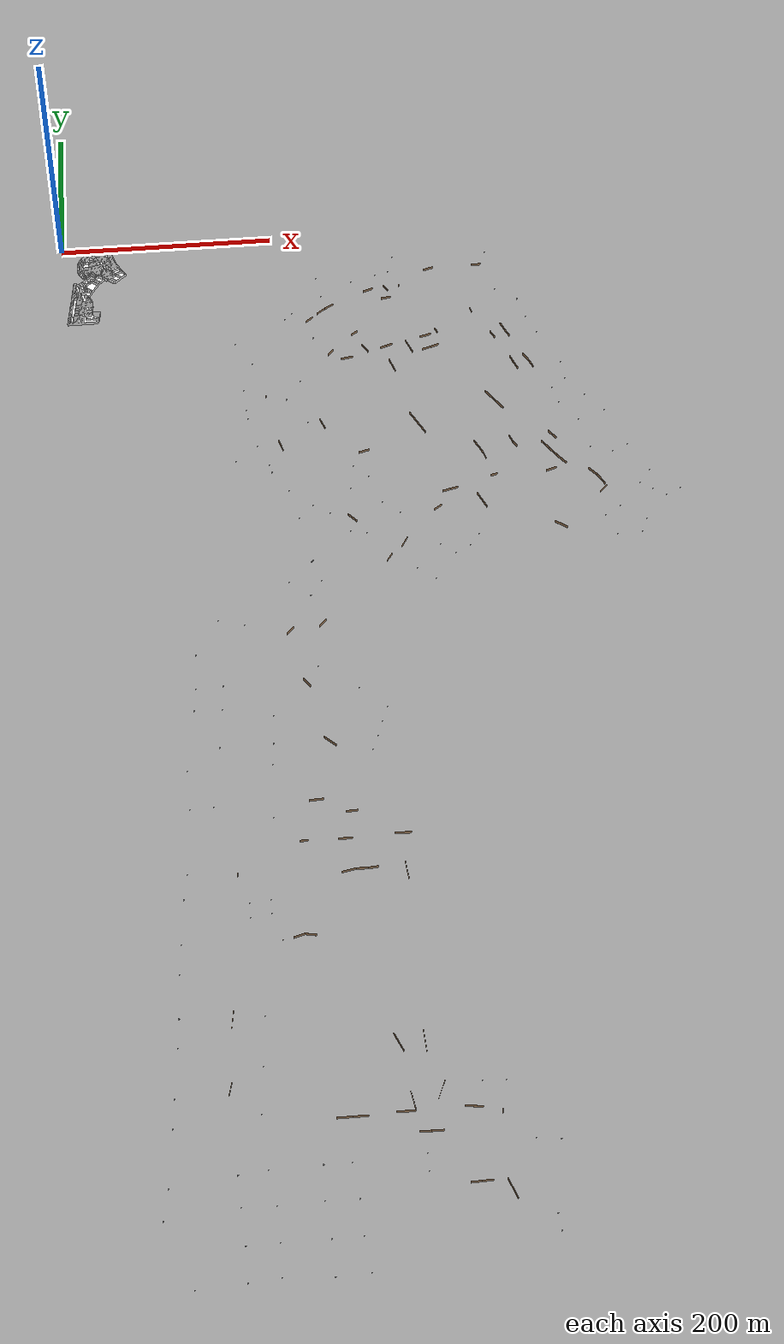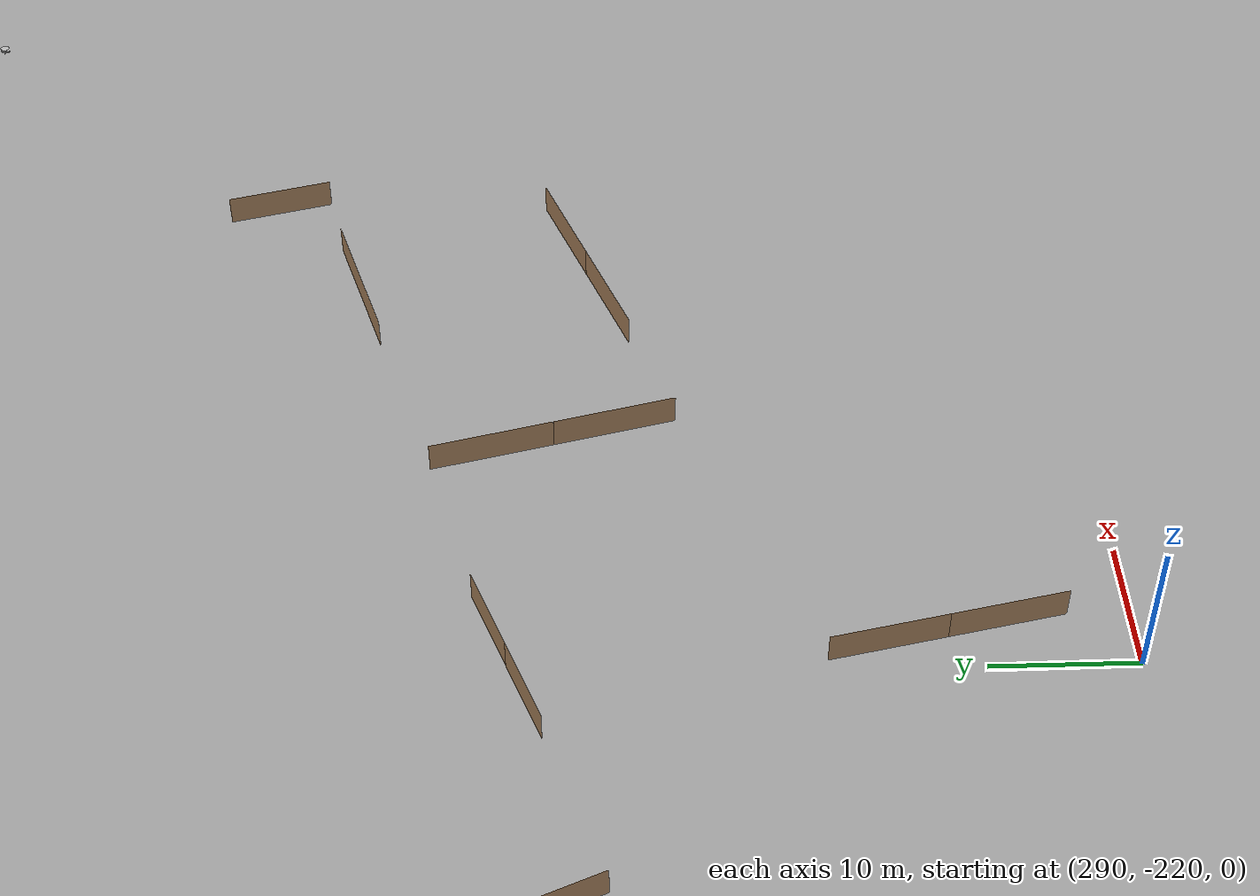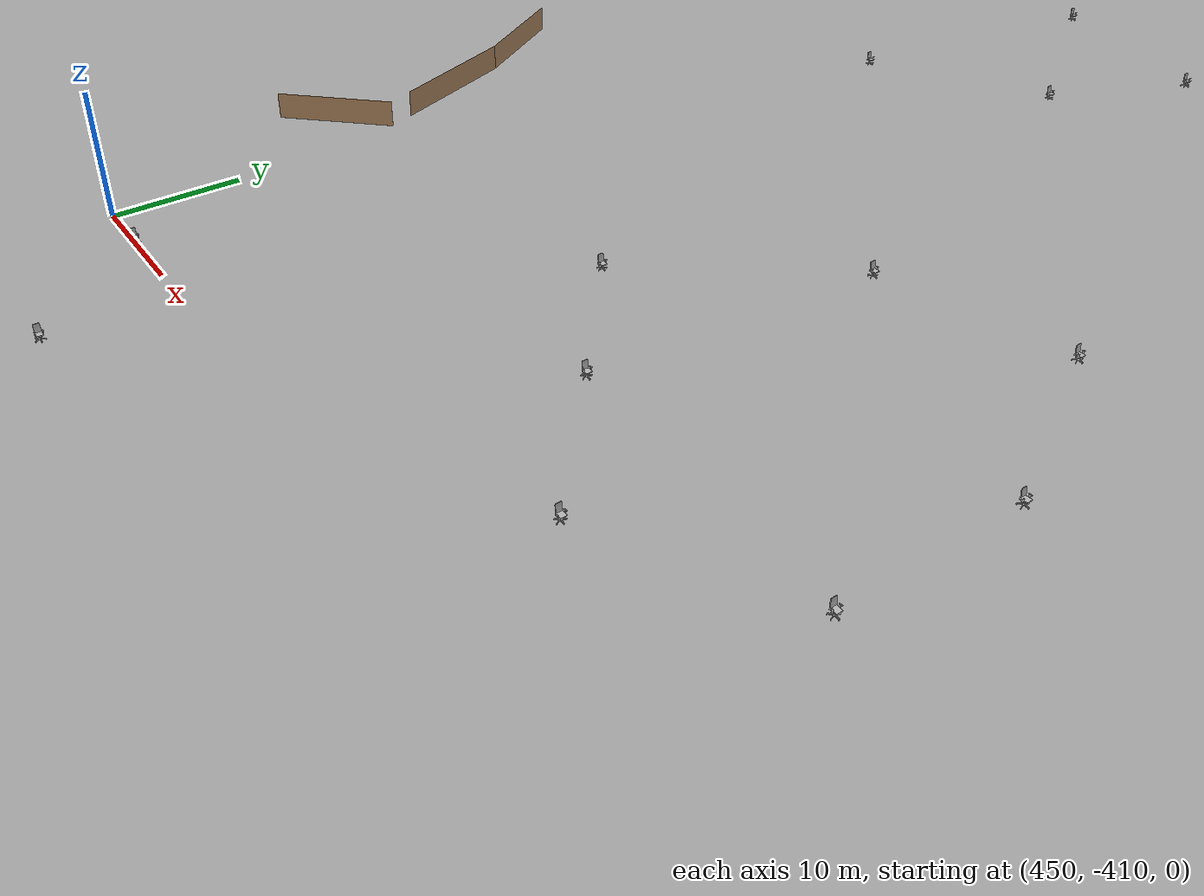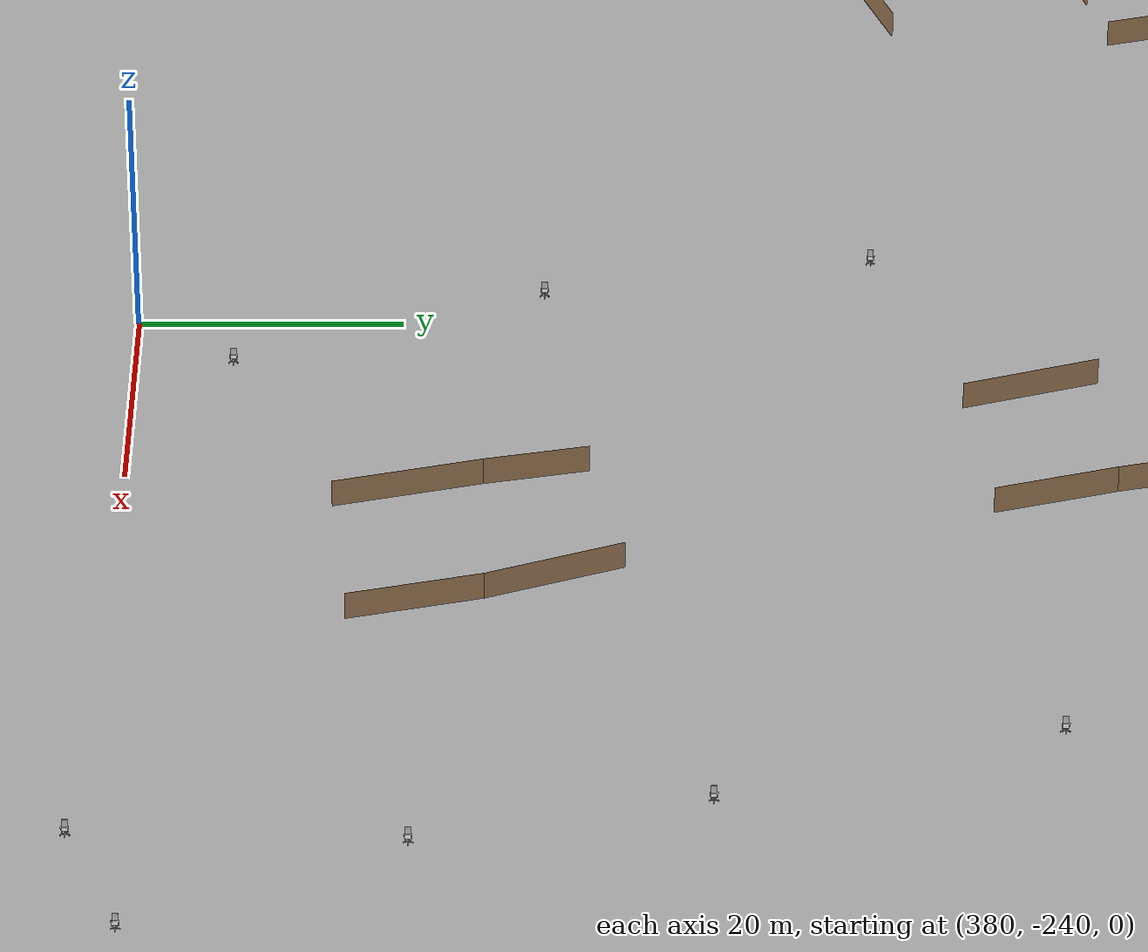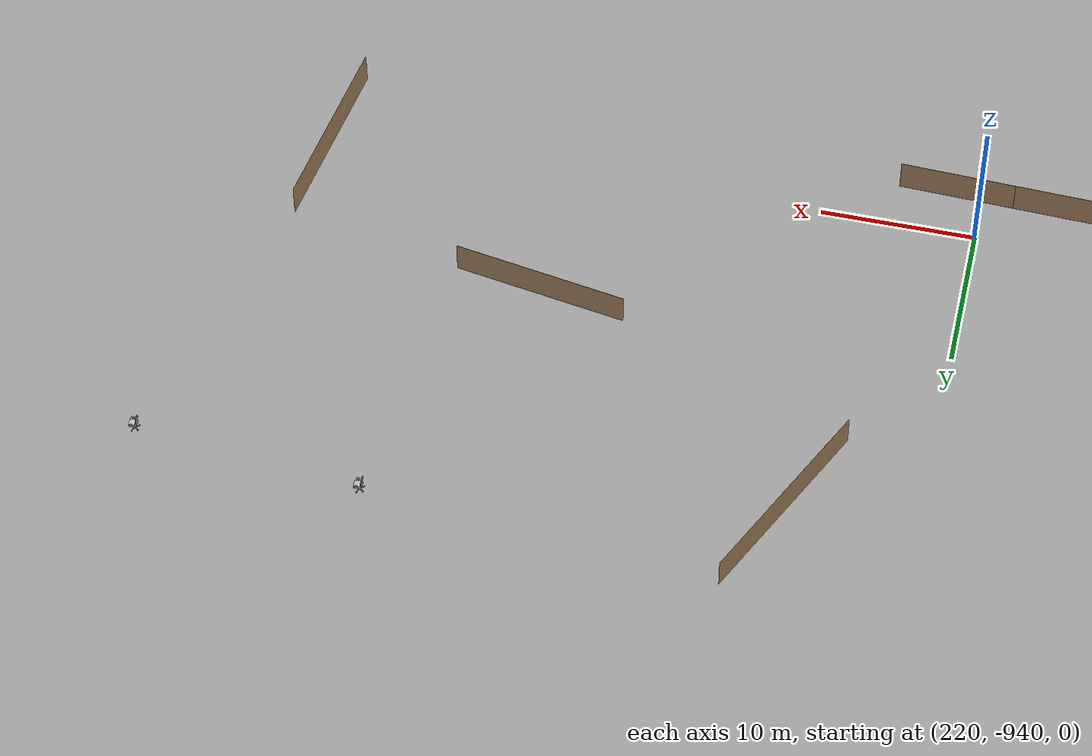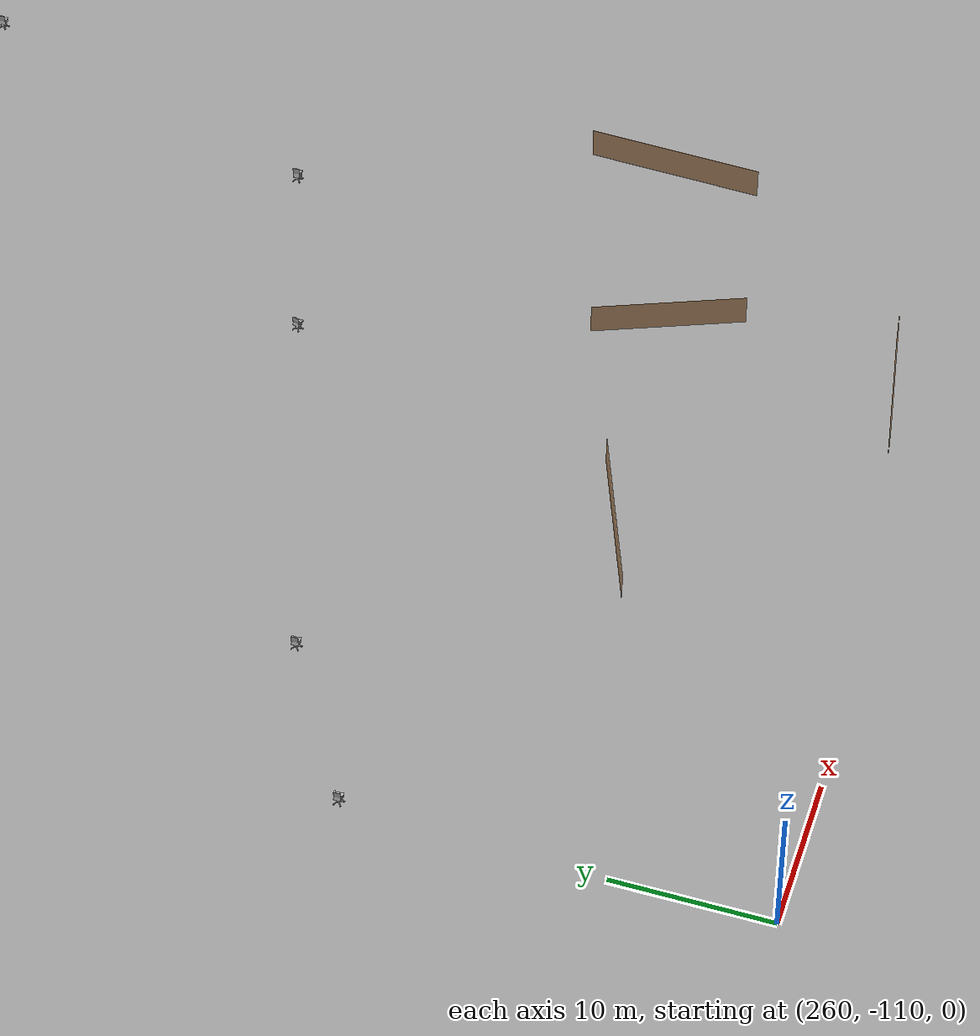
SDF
<sdf version="1.7">
 <world name="world">
  <scene><ambient>0.8 0.8 0.8 1.0</ambient><background>0 0 0</background><grid>false</grid></scene>
  <include><uri>model://sun</uri></include>
  <include>
   <name>OpenRobotics/OfficeChairBlue</name>
   <uri>model://OfficeChairBlue</uri>
   <pose>253.937 -912.607 0.0 0 0 1.5708</pose>
   <static>True</static>
  </include>
  <include>
   <name>OpenRobotics/OfficeChairBlue_2</name>
   <uri>model://OfficeChairBlue</uri>
   <pose>268.632 -914.17 0.0 0 0 1.5708</pose>
   <static>True</static>
  </include>
  <include>
   <name>OpenRobotics/OfficeChairBlue_3</name>
   <uri>model://OfficeChairBlue</uri>
   <pose>279.731 -953.721 0.0 0 0 1.5708</pose>
   <static>True</static>
  </include>
  <include>
   <name>OpenRobotics/OfficeChairBlue_4</name>
   <uri>model://OfficeChairBlue</uri>
   <pose>294.895 -956.066 0.0 0 0 1.5708</pose>
   <static>True</static>
  </include>
  <include>
   <name>OpenRobotics/OfficeChairBlue_5</name>
   <uri>model://OfficeChairBlue</uri>
   <pose>213.301 -956.772 0.0 0 0 1.5708</pose>
   <static>True</static>
  </include>
  <include>
   <name>OpenRobotics/OfficeChairBlue_6</name>
   <uri>model://OfficeChairBlue</uri>
   <pose>212.658 -967.923 0.0 0 0 1.5708</pose>
   <static>True</static>
  </include>
  <include>
   <name>OpenRobotics/OfficeChairBlue_7</name>
   <uri>model://OfficeChairBlue</uri>
   <pose>283.638 -1001.805 0.0 0 0 1.5708</pose>
   <static>True</static>
  </include>
  <include>
   <name>OpenRobotics/OfficeChairBlue_8</name>
   <uri>model://OfficeChairBlue</uri>
   <pose>283.638 -1012.312 0.0 0 0 1.5708</pose>
   <static>True</static>
  </include>
  <include>
   <name>OpenRobotics/OfficeChairBlue_9</name>
   <uri>model://OfficeChairBlue</uri>
   <pose>171.604 -1025.131 0.0 0 0 1.5708</pose>
   <static>True</static>
  </include>
  <include>
   <name>OpenRobotics/OfficeChairBlue_10</name>
   <uri>model://OfficeChairBlue</uri>
   <pose>150.637 -1025.369 0.0 0 0 1.5708</pose>
   <static>True</static>
  </include>
  <include>
   <name>OpenRobotics/OfficeChairBlue_11</name>
   <uri>model://OfficeChairBlue</uri>
   <pose>150.875 -1002.734 0.0 0 0 1.5708</pose>
   <static>True</static>
  </include>
  <include>
   <name>OpenRobotics/OfficeChairBlue_12</name>
   <uri>model://OfficeChairBlue</uri>
   <pose>169.698 -1002.972 0.0 0 0 1.5708</pose>
   <static>True</static>
  </include>
  <include>
   <name>OpenRobotics/OfficeChairBlue_13</name>
   <uri>model://OfficeChairBlue</uri>
   <pose>169.937 -980.337 0.0 0 0 1.5708</pose>
   <static>True</static>
  </include>
  <include>
   <name>OpenRobotics/OfficeChairBlue_14</name>
   <uri>model://OfficeChairBlue</uri>
   <pose>149.445 -979.622 0.0 0 0 1.5708</pose>
   <static>True</static>
  </include>
  <include>
   <name>OpenRobotics/OfficeChairBlue_15</name>
   <uri>model://OfficeChairBlue</uri>
   <pose>168.269 -957.463 0.0 0 0 1.5708</pose>
   <static>True</static>
  </include>
  <include>
   <name>OpenRobotics/OfficeChairBlue_16</name>
   <uri>model://OfficeChairBlue</uri>
   <pose>151.113 -957.225 0.0 0 0 1.5708</pose>
   <static>True</static>
  </include>
  <include>
   <name>OpenRobotics/OfficeChairBlue_17</name>
   <uri>model://OfficeChairBlue</uri>
   <pose>118.232 -956.986 0.0 0 0 1.5708</pose>
   <static>True</static>
  </include>
  <include>
   <name>OpenRobotics/OfficeChairBlue_18</name>
   <uri>model://OfficeChairBlue</uri>
   <pose>121.33 -979.622 0.0 0 0 1.5708</pose>
   <static>True</static>
  </include>
  <include>
   <name>OpenRobotics/OfficeChairBlue_19</name>
   <uri>model://OfficeChairBlue</uri>
   <pose>100.124 -958.178 0.0 0 0 1.5708</pose>
   <static>True</static>
  </include>
  <include>
   <name>OpenRobotics/OfficeChairBlue_20</name>
   <uri>model://OfficeChairBlue</uri>
   <pose>100.362 -978.43 0.0 0 0 1.5708</pose>
   <static>True</static>
  </include>
  <include>
   <name>OpenRobotics/OfficeChairBlue_21</name>
   <uri>model://OfficeChairBlue</uri>
   <pose>101.315 -1001.542 0.0 0 0 1.5708</pose>
   <static>True</static>
  </include>
  <include>
   <name>OpenRobotics/OfficeChairBlue_22</name>
   <uri>model://OfficeChairBlue</uri>
   <pose>101.077 -1023.463 0.0 0 0 1.5708</pose>
   <static>True</static>
  </include>
  <include>
   <name>OpenRobotics/OfficeChairBlue_23</name>
   <uri>model://OfficeChairBlue</uri>
   <pose>71.055 -1024.416 0.0 0 0 1.5708</pose>
   <static>True</static>
  </include>
  <include>
   <name>OpenRobotics/OfficeChairBlue_24</name>
   <uri>model://OfficeChairBlue</uri>
   <pose>121.33 -1002.019 0.0 0 0 1.5708</pose>
   <static>True</static>
  </include>
  <include>
   <name>OpenRobotics/OfficeChairBlue_25</name>
   <uri>model://OfficeChairBlue</uri>
   <pose>120.615 -1022.51 0.0 0 0 1.5708</pose>
   <static>True</static>
  </include>
  <include>
   <name>OpenRobotics/OfficeChairBlue_26</name>
   <uri>model://OfficeChairBlue</uri>
   <pose>120.919 -888.688 0.0 0 0 1.5708</pose>
   <static>True</static>
  </include>
  <include>
   <name>OpenRobotics/OfficeChairBlue_27</name>
   <uri>model://OfficeChairBlue</uri>
   <pose>124.801 -853.445 0.0 0 0 1.5708</pose>
   <static>True</static>
  </include>
  <include>
   <name>OpenRobotics/OfficeChairBlue_28</name>
   <uri>model://OfficeChairBlue</uri>
   <pose>117.334 -920.647 0.0 0 0 1.5708</pose>
   <static>True</static>
  </include>
  <include>
   <name>OpenRobotics/OfficeChairBlue_29</name>
   <uri>model://OfficeChairBlue</uri>
   <pose>55.128 -982.011 0.0 0 0 1.5708</pose>
   <static>True</static>
  </include>
  <include>
   <name>OpenRobotics/OfficeChairBlue_30</name>
   <uri>model://OfficeChairBlue</uri>
   <pose>58.658 -962.19 0.0 0 0 1.5708</pose>
   <static>True</static>
  </include>
  <include>
   <name>OpenRobotics/OfficeChairBlue_31</name>
   <uri>model://OfficeChairBlue</uri>
   <pose>63.002 -924.72 0.0 0 0 1.5708</pose>
   <static>True</static>
  </include>
  <include>
   <name>OpenRobotics/OfficeChairBlue_32</name>
   <uri>model://OfficeChairBlue</uri>
   <pose>64.903 -904.627 0.0 0 0 1.5708</pose>
   <static>True</static>
  </include>
  <include>
   <name>OpenRobotics/OfficeChairBlue_33</name>
   <uri>model://OfficeChairBlue</uri>
   <pose>68.976 -870.415 0.0 0 0 1.5708</pose>
   <static>True</static>
  </include>
  <include>
   <name>OpenRobotics/OfficeChairBlue_34</name>
   <uri>model://OfficeChairBlue</uri>
   <pose>70.605 -849.779 0.0 0 0 1.5708</pose>
   <static>True</static>
  </include>
  <include>
   <name>OpenRobotics/OfficeChairBlue_35</name>
   <uri>model://OfficeChairBlue</uri>
   <pose>72.506 -817.196 0.0 0 0 1.5708</pose>
   <static>True</static>
  </include>
  <include>
   <name>OpenRobotics/OfficeChairBlue_36</name>
   <uri>model://OfficeChairBlue</uri>
   <pose>74.678 -794.66 0.0 0 0 1.5708</pose>
   <static>True</static>
  </include>
  <include>
   <name>OpenRobotics/OfficeChairBlue_37</name>
   <uri>model://OfficeChairBlue</uri>
   <pose>78.479 -759.633 0.0 0 0 1.5708</pose>
   <static>True</static>
  </include>
  <include>
   <name>OpenRobotics/OfficeChairBlue_38</name>
   <uri>model://OfficeChairBlue</uri>
   <pose>81.466 -739.812 0.0 0 0 1.5708</pose>
   <static>True</static>
  </include>
  <include>
   <name>OpenRobotics/OfficeChairBlue_39</name>
   <uri>model://OfficeChairBlue</uri>
   <pose>84.181 -704.242 0.0 0 0 1.5708</pose>
   <static>True</static>
  </include>
  <include>
   <name>OpenRobotics/OfficeChairBlue_40</name>
   <uri>model://OfficeChairBlue</uri>
   <pose>86.353 -684.692 0.0 0 0 1.5708</pose>
   <static>True</static>
  </include>
  <include>
   <name>OpenRobotics/OfficeChairBlue_41</name>
   <uri>model://OfficeChairBlue</uri>
   <pose>102.618 -684.323 0.0 0 0 -1.5708</pose>
   <static>True</static>
  </include>
  <include>
   <name>OpenRobotics/OfficeChairBlue_42</name>
   <uri>model://OfficeChairBlue</uri>
   <pose>143.645 -697.725 0.0 0 0 1.5708</pose>
   <static>True</static>
  </include>
  <include>
   <name>OpenRobotics/OfficeChairBlue_43</name>
   <uri>model://OfficeChairBlue</uri>
   <pose>144.46 -677.09 0.0 0 0 1.5708</pose>
   <static>True</static>
  </include>
  <include>
   <name>OpenRobotics/OfficeChairBlue_44</name>
   <uri>model://OfficeChairBlue</uri>
   <pose>147.175 -650.752 0.0 0 0 1.5708</pose>
   <static>True</static>
  </include>
  <include>
   <name>OpenRobotics/OfficeChairBlue_45</name>
   <uri>model://OfficeChairBlue</uri>
   <pose>149.619 -631.474 0.0 0 0 1.5708</pose>
   <static>True</static>
  </include>
  <include>
   <name>OpenRobotics/OfficeChairBlue_46</name>
   <uri>model://OfficeChairBlue</uri>
   <pose>152.062 -605.407 0.0 0 0 1.5708</pose>
   <static>True</static>
  </include>
  <include>
   <name>OpenRobotics/OfficeChairBlue_47</name>
   <uri>model://OfficeChairBlue</uri>
   <pose>151.248 -586.944 0.0 0 0 1.5708</pose>
   <static>True</static>
  </include>
  <include>
   <name>OpenRobotics/OfficeChairBlue_48</name>
   <uri>model://OfficeChairBlue</uri>
   <pose>153.963 -563.593 0.0 0 0 1.5708</pose>
   <static>True</static>
  </include>
  <include>
   <name>OpenRobotics/OfficeChairBlue_49</name>
   <uri>model://OfficeChairBlue</uri>
   <pose>94.499 -594.546 0.0 0 0 1.5708</pose>
   <static>True</static>
  </include>
  <include>
   <name>OpenRobotics/OfficeChairBlue_50</name>
   <uri>model://OfficeChairBlue</uri>
   <pose>96.944 -573.52 0.0 0 0 1.5708</pose>
   <static>True</static>
  </include>
  <include>
   <name>OpenRobotics/OfficeChairBlue_51</name>
   <uri>model://OfficeChairBlue</uri>
   <pose>116.977 -572.102 0.0 0 0 1.5708</pose>
   <static>True</static>
  </include>
  <include>
   <name>OpenRobotics/OfficeChairBlue_52</name>
   <uri>model://OfficeChairBlue</uri>
   <pose>114.673 -595.326 0.0 0 0 1.5708</pose>
   <static>True</static>
  </include>
  <include>
   <name>OpenRobotics/OfficeChairBlue_53</name>
   <uri>model://OfficeChairBlue</uri>
   <pose>98.54 -538.95 0.0 0 0 1.5708</pose>
   <static>True</static>
  </include>
  <include>
   <name>OpenRobotics/OfficeChairBlue_54</name>
   <uri>model://OfficeChairBlue</uri>
   <pose>100.136 -519.094 0.0 0 0 1.5708</pose>
   <static>True</static>
  </include>
  <include>
   <name>OpenRobotics/OfficeChairBlue_55</name>
   <uri>model://OfficeChairBlue</uri>
   <pose>137.943 -511.188 0.0 0 0 1.5708</pose>
   <static>True</static>
  </include>
  <include>
   <name>OpenRobotics/OfficeChairBlue_56</name>
   <uri>model://OfficeChairBlue</uri>
   <pose>106.175 -500.327 0.0 0 0 1.5708</pose>
   <static>True</static>
  </include>
  <include>
   <name>OpenRobotics/OfficeChairBlue_57</name>
   <uri>model://OfficeChairBlue</uri>
   <pose>117.579 -504.943 0.0 0 0 1.5708</pose>
   <static>True</static>
  </include>
  <include>
   <name>OpenRobotics/OfficeChairBlue_58</name>
   <uri>model://OfficeChairBlue</uri>
   <pose>86.307 -650.107 0.0 0 0 1.5708</pose>
   <static>True</static>
  </include>
  <include>
   <name>OpenRobotics/OfficeChairBlue_59</name>
   <uri>model://OfficeChairBlue</uri>
   <pose>88.789 -628.833 0.0 0 0 1.5708</pose>
   <static>True</static>
  </include>
  <include>
   <name>OpenRobotics/OfficeChairBlue_60</name>
   <uri>model://OfficeChairBlue</uri>
   <pose>110.95 -631.138 0.0 0 0 1.5708</pose>
   <static>True</static>
  </include>
  <include>
   <name>OpenRobotics/OfficeChairBlue_61</name>
   <uri>model://OfficeChairBlue</uri>
   <pose>107.581 -651.348 0.0 0 0 1.5897</pose>
   <static>True</static>
  </include>
  <include>
   <name>OpenRobotics/OfficeChairBlue_62</name>
   <uri>model://OfficeChairBlue</uri>
   <pose>136.045 -765.929 0.0 0 0 1.6053</pose>
   <static>True</static>
  </include>
  <include>
   <name>OpenRobotics/OfficeChairBlue_63</name>
   <uri>model://OfficeChairBlue</uri>
   <pose>135.749 -776.44 0.0 0 0 1.5708</pose>
   <static>True</static>
  </include>
  <include>
   <name>OpenRobotics/OfficeChairBlue_64</name>
   <uri>model://OfficeChairBlue</uri>
   <pose>121.685 -766.669 0.0 0 0 1.5708</pose>
   <static>True</static>
  </include>
  <include>
   <name>OpenRobotics/OfficeChairBlue_65</name>
   <uri>model://OfficeChairBlue</uri>
   <pose>121.24 -778.365 0.0 0 0 1.5708</pose>
   <static>True</static>
  </include>
  <include>
   <name>OpenRobotics/OfficeChairBlue_66</name>
   <uri>model://OfficeChairBlue</uri>
   <pose>121.388 -778.513 0.0 0 0 1.5708</pose>
   <static>True</static>
  </include>
  <include>
   <name>OpenRobotics/OfficeChairBlue_67</name>
   <uri>model://OfficeChairBlue</uri>
   <pose>235.801 -605.554 0.0 0 0 1.5708</pose>
   <static>True</static>
  </include>
  <include>
   <name>OpenRobotics/OfficeChairBlue_68</name>
   <uri>model://OfficeChairBlue</uri>
   <pose>230.121 -618.808 0.0 0 0 1.5708</pose>
   <static>True</static>
  </include>
  <include>
   <name>OpenRobotics/OfficeChairBlue_69</name>
   <uri>model://OfficeChairBlue</uri>
   <pose>225.577 -631.873 0.0 0 0 1.5708</pose>
   <static>True</static>
  </include>
  <include>
   <name>OpenRobotics/OfficeChairBlue_70</name>
   <uri>model://OfficeChairBlue</uri>
   <pose>220.086 -644.749 0.0 0 0 1.5708</pose>
   <static>True</static>
  </include>
  <include>
   <name>OpenRobotics/OfficeChairBlue_71</name>
   <uri>model://OfficeChairBlue</uri>
   <pose>189.502 -560.014 0.0 0 0 1.5708</pose>
   <static>True</static>
  </include>
  <include>
   <name>OpenRobotics/OfficeChairBlue_72</name>
   <uri>model://OfficeChairBlue</uri>
   <pose>203.16 -574.166 0.0 0 0 1.5708</pose>
   <static>True</static>
  </include>
  <include>
   <name>OpenRobotics/OfficeChairBlue_73</name>
   <uri>model://OfficeChairBlue</uri>
   <pose>217.147 -585.026 0.0 0 0 1.5708</pose>
   <static>True</static>
  </include>
  <include>
   <name>OpenRobotics/KitchenCountertop</name>
   <uri>model://KitchenCountertop</uri>
   <pose>196.387 -447.655 0.0 0 0 2.3925</pose>
   <static>True</static>
  </include>
  <include>
   <name>OpenRobotics/OfficeChairBlue_74</name>
   <uri>model://OfficeChairBlue</uri>
   <pose>434.719 -434.611 0.0 0 0 1.5708</pose>
   <static>True</static>
  </include>
  <include>
   <name>OpenRobotics/OfficeChairBlue_75</name>
   <uri>model://OfficeChairBlue</uri>
   <pose>444.983 -443.009 0.0 0 0 1.5708</pose>
   <static>True</static>
  </include>
  <include>
   <name>OpenRobotics/OfficeChairBlue_76</name>
   <uri>model://OfficeChairBlue</uri>
   <pose>453.193 -450.659 0.0 0 0 1.5708</pose>
   <static>True</static>
  </include>
  <include>
   <name>OpenRobotics/OfficeChairBlue_77</name>
   <uri>model://OfficeChairBlue</uri>
   <pose>465.696 -442.635 0.0 0 0 1.5708</pose>
   <static>True</static>
  </include>
  <include>
   <name>OpenRobotics/OfficeChairBlue_78</name>
   <uri>model://OfficeChairBlue</uri>
   <pose>472.414 -428.08 0.0 0 0 1.5708</pose>
   <static>True</static>
  </include>
  <include>
   <name>OpenRobotics/OfficeChairBlue_79</name>
   <uri>model://OfficeChairBlue</uri>
   <pose>463.084 -419.123 0.0 0 0 1.5708</pose>
   <static>True</static>
  </include>
  <include>
   <name>OpenRobotics/OfficeChairBlue_80</name>
   <uri>model://OfficeChairBlue</uri>
   <pose>454.873 -409.979 0.0 0 0 1.5708</pose>
   <static>True</static>
  </include>
  <include>
   <name>OpenRobotics/OfficeChairBlue_81</name>
   <uri>model://OfficeChairBlue</uri>
   <pose>440.504 -420.056 0.0 0 0 1.4973</pose>
   <static>True</static>
  </include>
  <include>
   <name>OpenRobotics/OfficeChairBlue_82</name>
   <uri>model://OfficeChairBlue</uri>
   <pose>495.74 -401.395 0.0 0 0 1.5708</pose>
   <static>True</static>
  </include>
  <include>
   <name>OpenRobotics/OfficeChairBlue_83</name>
   <uri>model://OfficeChairBlue</uri>
   <pose>486.41 -392.811 0.0 0 0 1.5708</pose>
   <static>True</static>
  </include>
  <include>
   <name>OpenRobotics/OfficeChairBlue_84</name>
   <uri>model://OfficeChairBlue</uri>
   <pose>477.079 -384.6 0.0 0 0 1.5708</pose>
   <static>True</static>
  </include>
  <include>
   <name>OpenRobotics/OfficeChairBlue_85</name>
   <uri>model://OfficeChairBlue</uri>
   <pose>508.803 -394.304 0.0 0 0 1.5708</pose>
   <static>True</static>
  </include>
  <include>
   <name>OpenRobotics/OfficeChairBlue_86</name>
   <uri>model://OfficeChairBlue</uri>
   <pose>509.176 -380.308 0.0 0 0 1.5708</pose>
   <static>True</static>
  </include>
  <include>
   <name>OpenRobotics/OfficeChairBlue_87</name>
   <uri>model://OfficeChairBlue</uri>
   <pose>502.831 -366.686 0.0 0 0 1.5708</pose>
   <static>True</static>
  </include>
  <include>
   <name>OpenRobotics/OfficeChairBlue_88</name>
   <uri>model://OfficeChairBlue</uri>
   <pose>488.649 -369.858 0.0 0 0 1.5708</pose>
   <static>True</static>
  </include>
  <include>
   <name>OpenRobotics/OfficeChairBlue_89</name>
   <uri>model://OfficeChairBlue</uri>
   <pose>445.532 -335.038 0.0 0 0 1.5708</pose>
   <static>True</static>
  </include>
  <include>
   <name>OpenRobotics/OfficeChairBlue_90</name>
   <uri>model://OfficeChairBlue</uri>
   <pose>454.014 -325.476 0.0 0 0 1.5708</pose>
   <static>True</static>
  </include>
  <include>
   <name>OpenRobotics/OfficeChairBlue_91</name>
   <uri>model://OfficeChairBlue</uri>
   <pose>466.968 -317.457 0.0 0 0 1.5833</pose>
   <static>True</static>
  </include>
  <include>
   <name>OpenRobotics/OfficeChairBlue_92</name>
   <uri>model://OfficeChairBlue</uri>
   <pose>482.853 -323.009 0.0 0 0 1.5708</pose>
   <static>True</static>
  </include>
  <include>
   <name>OpenRobotics/OfficeChairBlue_93</name>
   <uri>model://OfficeChairBlue</uri>
   <pose>477.455 -335.346 0.0 0 0 1.5708</pose>
   <static>True</static>
  </include>
  <include>
   <name>OpenRobotics/OfficeChairBlue_94</name>
   <uri>model://OfficeChairBlue</uri>
   <pose>462.959 -342.595 0.0 0 0 1.5708</pose>
   <static>True</static>
  </include>
  <include>
   <name>OpenRobotics/OfficeChairBlue_95</name>
   <uri>model://OfficeChairBlue</uri>
   <pose>443.064 -298.642 0.0 0 0 1.5708</pose>
   <static>True</static>
  </include>
  <include>
   <name>OpenRobotics/OfficeChairBlue_96</name>
   <uri>model://OfficeChairBlue</uri>
   <pose>454.939 -294.478 0.0 0 0 1.5708</pose>
   <static>True</static>
  </include>
  <include>
   <name>OpenRobotics/OfficeChairBlue_97</name>
   <uri>model://OfficeChairBlue</uri>
   <pose>468.048 -288.309 0.0 0 0 1.5708</pose>
   <static>True</static>
  </include>
  <include>
   <name>OpenRobotics/OfficeChairBlue_98</name>
   <uri>model://OfficeChairBlue</uri>
   <pose>430.572 -273.658 0.0 0 0 1.5708</pose>
   <static>True</static>
  </include>
  <include>
   <name>OpenRobotics/OfficeChairBlue_99</name>
   <uri>model://OfficeChairBlue</uri>
   <pose>442.601 -269.339 0.0 0 0 1.5708</pose>
   <static>True</static>
  </include>
  <include>
   <name>OpenRobotics/OfficeChairBlue_100</name>
   <uri>model://OfficeChairBlue</uri>
   <pose>455.556 -265.175 0.0 0 0 1.5708</pose>
   <static>True</static>
  </include>
  <include>
   <name>OpenRobotics/OfficeChairBlue_101</name>
   <uri>model://OfficeChairBlue</uri>
   <pose>442.766 -241.715 0.0 0 0 1.5708</pose>
   <static>True</static>
  </include>
  <include>
   <name>OpenRobotics/OfficeChairBlue_102</name>
   <uri>model://OfficeChairBlue</uri>
   <pose>453.025 -237.669 0.0 0 0 1.5708</pose>
   <static>True</static>
  </include>
  <include>
   <name>OpenRobotics/OfficeChairBlue_103</name>
   <uri>model://OfficeChairBlue</uri>
   <pose>428.75 -253.274 0.0 0 0 1.5708</pose>
   <static>True</static>
  </include>
  <include>
   <name>OpenRobotics/OfficeChairBlue_104</name>
   <uri>model://OfficeChairBlue</uri>
   <pose>409.966 -260.932 0.0 0 0 1.5708</pose>
   <static>True</static>
  </include>
  <include>
   <name>OpenRobotics/OfficeChairBlue_105</name>
   <uri>model://OfficeChairBlue</uri>
   <pose>278.452 -464.528 0.0 0 0 2.2489</pose>
   <static>True</static>
  </include>
  <include>
   <name>OpenRobotics/OfficeChairBlue_106</name>
   <uri>model://OfficeChairBlue</uri>
   <pose>291.328 -477.404 0.0 0 0 1.5708</pose>
   <static>True</static>
  </include>
  <include>
   <name>OpenRobotics/OfficeChairBlue_107</name>
   <uri>model://OfficeChairBlue</uri>
   <pose>305.421 -486.451 0.0 0 0 1.5708</pose>
   <static>True</static>
  </include>
  <include>
   <name>OpenRobotics/OfficeChairBlue_108</name>
   <uri>model://OfficeChairBlue</uri>
   <pose>300.897 -439.474 0.0 0 0 1.5708</pose>
   <static>True</static>
  </include>
  <include>
   <name>OpenRobotics/OfficeChairBlue_109</name>
   <uri>model://OfficeChairBlue</uri>
   <pose>311.336 -450.609 0.0 0 0 1.5708</pose>
   <static>True</static>
  </include>
  <include>
   <name>OpenRobotics/OfficeChairBlue_110</name>
   <uri>model://OfficeChairBlue</uri>
   <pose>324.386 -442.954 0.0 0 0 1.5708</pose>
   <static>True</static>
  </include>
  <include>
   <name>OpenRobotics/OfficeChairBlue_111</name>
   <uri>model://OfficeChairBlue</uri>
   <pose>333.607 -430.774 0.0 0 0 1.5708</pose>
   <static>True</static>
  </include>
  <include>
   <name>OpenRobotics/OfficeChairBlue_112</name>
   <uri>model://OfficeChairBlue</uri>
   <pose>243.725 -419.767 0.0 0 0 1.5708</pose>
   <static>True</static>
  </include>
  <include>
   <name>OpenRobotics/OfficeChairBlue_113</name>
   <uri>model://OfficeChairBlue</uri>
   <pose>232.462 -429.252 0.0 0 0 1.5708</pose>
   <static>True</static>
  </include>
  <include>
   <name>OpenRobotics/OfficeChairBlue_114</name>
   <uri>model://OfficeChairBlue</uri>
   <pose>230.832 -416.507 0.0 0 0 1.5708</pose>
   <static>True</static>
  </include>
  <include>
   <name>OpenRobotics/OfficeChairBlue_115</name>
   <uri>model://OfficeChairBlue</uri>
   <pose>244.614 -431.623 0.0 0 0 1.5708</pose>
   <static>True</static>
  </include>
  <include>
   <name>OpenRobotics/OfficeChairBlue_116</name>
   <uri>model://OfficeChairBlue</uri>
   <pose>253.682 -352.434 0.0 0 0 1.5708</pose>
   <static>True</static>
  </include>
  <include>
   <name>OpenRobotics/OfficeChairBlue_117</name>
   <uri>model://OfficeChairBlue</uri>
   <pose>242.5 -337.614 0.0 0 0 1.5708</pose>
   <static>True</static>
  </include>
  <include>
   <name>OpenRobotics/OfficeChairBlue_118</name>
   <uri>model://OfficeChairBlue</uri>
   <pose>225.256 -350.278 0.0 0 0 2.63</pose>
   <static>True</static>
  </include>
  <include>
   <name>OpenRobotics/OfficeChairBlue_119</name>
   <uri>model://OfficeChairBlue</uri>
   <pose>236.842 -365.232 0.0 0 0 1.7862</pose>
   <static>True</static>
  </include>
  <include>
   <name>OpenRobotics/OfficeChairBlue_120</name>
   <uri>model://OfficeChairBlue</uri>
   <pose>260.957 -385.171 0.0 0 0 1.5708</pose>
   <static>True</static>
  </include>
  <include>
   <name>OpenRobotics/OfficeChairBlue_121</name>
   <uri>model://OfficeChairBlue</uri>
   <pose>273.756 -399.182 0.0 0 0 1.5708</pose>
   <static>True</static>
  </include>
  <include>
   <name>OpenRobotics/OfficeChairBlue_122</name>
   <uri>model://OfficeChairBlue</uri>
   <pose>289.653 -383.555 0.0 0 0 2.1815</pose>
   <static>True</static>
  </include>
  <include>
   <name>OpenRobotics/OfficeChairBlue_123</name>
   <uri>model://OfficeChairBlue</uri>
   <pose>275.777 -370.082 0.0 0 0 1.5708</pose>
   <static>True</static>
  </include>
  <include>
   <name>OpenRobotics/OfficeChairBlue_124</name>
   <uri>model://OfficeChairBlue</uri>
   <pose>216.762 -393.327 0.0 0 0 1.5708</pose>
   <static>True</static>
  </include>
  <include>
   <name>OpenRobotics/OfficeChairBlue_125</name>
   <uri>model://OfficeChairBlue</uri>
   <pose>201.277 -407.337 0.0 0 0 -1.9996</pose>
   <static>True</static>
  </include>
  <include>
   <name>OpenRobotics/OfficeChairBlue_126</name>
   <uri>model://OfficeChairBlue</uri>
   <pose>190.954 -396.424 0.0 0 0 1.5708</pose>
   <static>True</static>
  </include>
  <include>
   <name>OpenRobotics/OfficeChairBlue_127</name>
   <uri>model://OfficeChairBlue</uri>
   <pose>203.932 -382.561 0.0 0 0 1.5708</pose>
   <static>True</static>
  </include>
  <include>
   <name>OpenRobotics/OfficeChairBlue_128</name>
   <uri>model://OfficeChairBlue</uri>
   <pose>198.013 -283.097 0.0 0 0 1.5708</pose>
   <static>True</static>
  </include>
  <include>
   <name>OpenRobotics/OfficeChairBlue_129</name>
   <uri>model://OfficeChairBlue</uri>
   <pose>210.172 -276.755 0.0 0 0 1.5708</pose>
   <static>True</static>
  </include>
  <include>
   <name>OpenRobotics/OfficeChairBlue_130</name>
   <uri>model://OfficeChairBlue</uri>
   <pose>194.752 -244.657 0.0 0 0 1.5708</pose>
   <static>True</static>
  </include>
  <include>
   <name>OpenRobotics/OfficeChairBlue_131</name>
   <uri>model://OfficeChairBlue</uri>
   <pose>206.29 -235.478 0.0 0 0 1.5708</pose>
   <static>True</static>
  </include>
  <include>
   <name>OpenRobotics/OfficeChairBlue_132</name>
   <uri>model://OfficeChairBlue</uri>
   <pose>208.742 -220.356 0.0 0 0 1.5708</pose>
   <static>True</static>
  </include>
  <include>
   <name>OpenRobotics/OfficeChairBlue_133</name>
   <uri>model://OfficeChairBlue</uri>
   <pose>210.43 -206.47 0.0 0 0 1.5708</pose>
   <static>True</static>
  </include>
  <include>
   <name>OpenRobotics/OfficeChairBlue_134</name>
   <uri>model://OfficeChairBlue</uri>
   <pose>196.459 -203.365 0.0 0 0 1.5708</pose>
   <static>True</static>
  </include>
  <include>
   <name>OpenRobotics/OfficeChairBlue_135</name>
   <uri>model://OfficeChairBlue</uri>
   <pose>226.52 -159.667 0.0 0 0 1.5708</pose>
   <static>True</static>
  </include>
  <include>
   <name>OpenRobotics/OfficeChairBlue_136</name>
   <uri>model://OfficeChairBlue</uri>
   <pose>215.894 -173.562 0.0 0 0 1.5708</pose>
   <static>True</static>
  </include>
  <include>
   <name>OpenRobotics/OfficeChairBlue_137</name>
   <uri>model://OfficeChairBlue</uri>
   <pose>375.895 -42.374 0.0 0 0 1.5708</pose>
   <static>True</static>
  </include>
  <include>
   <name>OpenRobotics/OfficeChairBlue_138</name>
   <uri>model://OfficeChairBlue</uri>
   <pose>404.094 -43.191 0.0 0 0 1.5708</pose>
   <static>True</static>
  </include>
  <include>
   <name>OpenRobotics/OfficeChairBlue_139</name>
   <uri>model://OfficeChairBlue</uri>
   <pose>424.324 -148.836 0.0 0 0 1.5708</pose>
   <static>True</static>
  </include>
  <include>
   <name>OpenRobotics/OfficeChairBlue_140</name>
   <uri>model://OfficeChairBlue</uri>
   <pose>443.532 -218.109 0.0 0 0 1.5708</pose>
   <static>True</static>
  </include>
  <include>
   <name>OpenRobotics/OfficeChairBlue_141</name>
   <uri>model://OfficeChairBlue</uri>
   <pose>438.833 -197.061 0.0 0 0 1.5708</pose>
   <static>True</static>
  </include>
  <include>
   <name>OpenRobotics/OfficeChairBlue_142</name>
   <uri>model://OfficeChairBlue</uri>
   <pose>430.863 -172.336 0.0 0 0 1.5708</pose>
   <static>True</static>
  </include>
  <include>
   <name>OpenRobotics/OfficeChairBlue_143</name>
   <uri>model://OfficeChairBlue</uri>
   <pose>371.808 -184.392 0.0 0 0 1.5708</pose>
   <static>True</static>
  </include>
  <include>
   <name>OpenRobotics/OfficeChairBlue_144</name>
   <uri>model://OfficeChairBlue</uri>
   <pose>376.303 -209.322 0.0 0 0 1.5708</pose>
   <static>True</static>
  </include>
  <include>
   <name>OpenRobotics/OfficeChairBlue_145</name>
   <uri>model://OfficeChairBlue</uri>
   <pose>385.295 -232.617 0.0 0 0 1.5708</pose>
   <static>True</static>
  </include>
  <include>
   <name>OpenRobotics/OfficeChairBlue_146</name>
   <uri>model://OfficeChairBlue</uri>
   <pose>399.394 -81.607 0.0 0 0 1.5708</pose>
   <static>True</static>
  </include>
  <include>
   <name>OpenRobotics/OfficeChairBlue_147</name>
   <uri>model://OfficeChairBlue</uri>
   <pose>410.224 -82.22 0.0 0 0 1.5708</pose>
   <static>True</static>
  </include>
  <include>
   <name>OpenRobotics/OfficeChairBlue_148</name>
   <uri>model://OfficeChairBlue</uri>
   <pose>403.685 -103.268 0.0 0 0 2.6584</pose>
   <static>True</static>
  </include>
  <include>
   <name>OpenRobotics/OfficeChairBlue_149</name>
   <uri>model://OfficeChairBlue</uri>
   <pose>405.525 -128.198 0.0 0 0 1.5708</pose>
   <static>True</static>
  </include>
  <include>
   <name>OpenRobotics/OfficeChairBlue_150</name>
   <uri>model://OfficeChairBlue</uri>
   <pose>421.463 -120.841 0.0 0 0 3.0485</pose>
   <static>True</static>
  </include>
  <include>
   <name>OpenRobotics/OfficeChairBlue_151</name>
   <uri>model://OfficeChairBlue</uri>
   <pose>164.135 -304.146 0.0 0 0 1.5708</pose>
   <static>True</static>
  </include>
  <include>
   <name>OpenRobotics/OfficeChairBlue_152</name>
   <uri>model://OfficeChairBlue</uri>
   <pose>162.618 -292.448 0.0 0 0 1.5708</pose>
   <static>True</static>
  </include>
  <include>
   <name>OpenRobotics/OfficeChairBlue_153</name>
   <uri>model://OfficeChairBlue</uri>
   <pose>158.935 -266.883 0.0 0 0 1.5708</pose>
   <static>True</static>
  </include>
  <include>
   <name>OpenRobotics/OfficeChairBlue_154</name>
   <uri>model://OfficeChairBlue</uri>
   <pose>158.502 -255.401 0.0 0 0 1.5708</pose>
   <static>True</static>
  </include>
  <include>
   <name>OpenRobotics/OfficeChairBlue_155</name>
   <uri>model://OfficeChairBlue</uri>
   <pose>158.285 -228.32 0.0 0 0 1.5708</pose>
   <static>True</static>
  </include>
  <include>
   <name>OpenRobotics/OfficeChairBlue_156</name>
   <uri>model://OfficeChairBlue</uri>
   <pose>160.235 -217.921 0.0 0 0 1.5708</pose>
   <static>True</static>
  </include>
  <include>
   <name>OpenRobotics/OfficeChairBlue_157</name>
   <uri>model://OfficeChairBlue</uri>
   <pose>168.685 -192.14 0.0 0 0 1.5708</pose>
   <static>True</static>
  </include>
  <include>
   <name>OpenRobotics/OfficeChairBlue_158</name>
   <uri>model://OfficeChairBlue</uri>
   <pose>170.634 -183.474 0.0 0 0 1.5708</pose>
   <static>True</static>
  </include>
  <include>
   <name>OpenRobotics/OfficeChairBlue_159</name>
   <uri>model://OfficeChairBlue</uri>
   <pose>183.85 -160.726 0.0 0 0 1.9672</pose>
   <static>True</static>
  </include>
  <include>
   <name>OpenRobotics/OfficeChairBlue_160</name>
   <uri>model://OfficeChairBlue</uri>
   <pose>187.316 -151.194 0.0 0 0 1.5708</pose>
   <static>True</static>
  </include>
  <include>
   <name>OpenRobotics/OfficeChairBlue_161</name>
   <uri>model://OfficeChairBlue</uri>
   <pose>203.781 -129.096 0.0 0 0 1.5708</pose>
   <static>True</static>
  </include>
  <include>
   <name>OpenRobotics/OfficeChairBlue_162</name>
   <uri>model://OfficeChairBlue</uri>
   <pose>210.497 -120.43 0.0 0 0 1.5708</pose>
   <static>True</static>
  </include>
  <include>
   <name>OpenRobotics/OfficeChairBlue_163</name>
   <uri>model://OfficeChairBlue</uri>
   <pose>228.912 -103.315 0.0 0 0 1.5708</pose>
   <static>True</static>
  </include>
  <include>
   <name>OpenRobotics/OfficeChairBlue_164</name>
   <uri>model://OfficeChairBlue</uri>
   <pose>240.395 -97.682 0.0 0 0 1.5708</pose>
   <static>True</static>
  </include>
  <include>
   <name>OpenRobotics/OfficeChairBlue_165</name>
   <uri>model://OfficeChairBlue</uri>
   <pose>260.76 -83.6 0.0 0 0 1.5708</pose>
   <static>True</static>
  </include>
  <include>
   <name>OpenRobotics/OfficeChairBlue_166</name>
   <uri>model://OfficeChairBlue</uri>
   <pose>270.725 -77.534 0.0 0 0 1.5708</pose>
   <static>True</static>
  </include>
  <include>
   <name>OpenRobotics/OfficeChairBlue_167</name>
   <uri>model://OfficeChairBlue</uri>
   <pose>294.773 -69.301 0.0 0 0 1.3253</pose>
   <static>True</static>
  </include>
  <include>
   <name>OpenRobotics/OfficeChairBlue_168</name>
   <uri>model://OfficeChairBlue</uri>
   <pose>307.122 -64.968 0.0 0 0 1.5708</pose>
   <static>True</static>
  </include>
  <include>
   <name>OpenRobotics/OfficeChairBlue_169</name>
   <uri>model://OfficeChairBlue</uri>
   <pose>332.037 -61.502 0.0 0 0 1.2406</pose>
   <static>True</static>
  </include>
  <include>
   <name>OpenRobotics/OfficeChairBlue_170</name>
   <uri>model://OfficeChairBlue</uri>
   <pose>314.705 -41.353 0.0 0 0 1.5708</pose>
   <static>True</static>
  </include>
  <include>
   <name>OpenRobotics/OfficeChairBlue_171</name>
   <uri>model://OfficeChairBlue</uri>
   <pose>277.225 -51.103 0.0 0 0 1.5708</pose>
   <static>True</static>
  </include>
  <include>
   <name>OpenRobotics/OfficeChairBlue_172</name>
   <uri>model://OfficeChairBlue</uri>
   <pose>238.228 -68.868 0.0 0 0 1.5708</pose>
   <static>True</static>
  </include>
  <include>
   <name>OpenRobotics/OfficeChairBlue_173</name>
   <uri>model://OfficeChairBlue</uri>
   <pose>204.648 -95.732 0.0 0 0 1.5708</pose>
   <static>True</static>
  </include>
  <include>
   <name>OpenRobotics/OfficeChairBlue_174</name>
   <uri>model://OfficeChairBlue</uri>
   <pose>175.834 -127.146 0.0 0 0 1.5708</pose>
   <static>True</static>
  </include>
  <include>
   <name>OpenRobotics/OfficeChairBlue_175</name>
   <uri>model://OfficeChairBlue</uri>
   <pose>155.252 -161.376 0.0 0 0 1.5708</pose>
   <static>True</static>
  </include>
  <include>
   <name>OpenRobotics/OfficeChairBlue_176</name>
   <uri>model://OfficeChairBlue</uri>
   <pose>140.304 -198.423 0.0 0 0 1.5708</pose>
   <static>True</static>
  </include>
  <include>
   <name>OpenRobotics/OfficeChairBlue_177</name>
   <uri>model://OfficeChairBlue</uri>
   <pose>136.621 -241.319 0.0 0 0 1.5708</pose>
   <static>True</static>
  </include>
  <include>
   <name>OpenRobotics/OfficeChairBlue_178</name>
   <uri>model://OfficeChairBlue</uri>
   <pose>137.921 -284.648 0.0 0 0 1.5708</pose>
   <static>True</static>
  </include>
  <include>
   <name>OpenRobotics/OfficeChairBlue_179</name>
   <uri>model://OfficeChairBlue</uri>
   <pose>159.369 -360.258 0.0 0 0 1.5708</pose>
   <static>True</static>
  </include>
  <include>
   <name>OpenRobotics/OfficeChairBlue_180</name>
   <uri>model://OfficeChairBlue</uri>
   <pose>144.853 -321.478 0.0 0 0 1.5708</pose>
   <static>True</static>
  </include>
  <include>
   <name>OpenRobotics/OfficeChairBlue_181</name>
   <uri>model://OfficeChairBlue</uri>
   <pose>185.581 -362.686 0.0 0 0 1.5708</pose>
   <static>True</static>
  </include>
  <include>
   <name>OpenRobotics/OfficeChairBlue_182</name>
   <uri>model://OfficeChairBlue</uri>
   <pose>173.7 -338.52 0.0 0 0 1.5708</pose>
   <static>True</static>
  </include>
  <include>
   <name>OpenRobotics/OfficeChairBlue_183</name>
   <uri>model://OfficeChairBlue</uri>
   <pose>172.427 -328.972 0.0 0 0 1.5708</pose>
   <static>True</static>
  </include>
  <include>
   <name>OpenRobotics/CoffeeTable</name>
   <uri>model://CoffeeTable</uri>
   <pose>216.636 -453.898 0.0 0 0 1.5708</pose>
   <static>True</static>
  </include>
  <include>
   <name>OpenRobotics/CoffeeTable_2</name>
   <uri>model://CoffeeTable</uri>
   <pose>201.354 -470.387 0.0 0 0 1.5708</pose>
   <static>True</static>
  </include>
  <include>
   <name>OpenRobotics/MiniSofa</name>
   <uri>model://MiniSofa</uri>
   <pose>175.753 -469.258 0.0 0 0 2.3973</pose>
   <static>True</static>
  </include>
  <include>
   <name>OpenRobotics/MiniSofa_2</name>
   <uri>model://MiniSofa</uri>
   <pose>191.329 -485.321 0.0 0 0 -2.2655</pose>
   <static>True</static>
  </include>
  <include>
   <name>OpenRobotics/CoffeeTable_3</name>
   <uri>model://CoffeeTable</uri>
   <pose>362.649 -134.475 0.0 0 0 1.5708</pose>
   <static>True</static>
  </include>
  <model name="double_hinged">
   <pose>217.976 -942.9749999999999 0.0 0 0 3.099994751753799</pose>
   <link name="right">
    <pose>3.727224302346188 0 1.11 0 0 0</pose>
    <visual name="right_visual">
     <geometry><box><size>7.444448604692377 0.03 2.2</size></box></geometry>
     <material><ambient>0.5 0.25 0 0.6</ambient><diffuse>0.5 0.25 0 0.6</diffuse></material>
    </visual>
    <collision name="right_collision">
     <geometry><box><size>7.444448604692377 0.03 2.2</size></box></geometry>
     <surface><contact><collide_bitmask>0x02</collide_bitmask></contact></surface>
    </collision>
    <inertial>
     <mass>50.0</mass>
     <inertia><ixx>20.17041666666667</ixx><iyy>251.08256261627616</iyy><izz>230.9196459496095</izz></inertia>
    </inertial>
   </link>
   <joint name="right_joint" type="revolute">
    <parent>world</parent>
    <child>right</child>
    <axis><xyz>0 0 -1</xyz><limit><lower>0</lower><upper>1.57</upper></limit></axis>
    <pose>3.727224302346188 0 0 0 0 0</pose>
   </joint>
   <link name="left">
    <pose>-3.727224302346188 0 1.11 0 0 0</pose>
    <visual name="left_visual">
     <geometry><box><size>7.444448604692377 0.03 2.2</size></box></geometry>
     <material><ambient>0.5 0.25 0 0.6</ambient><diffuse>0.5 0.25 0 0.6</diffuse></material>
    </visual>
    <collision name="left_collision">
     <geometry><box><size>7.444448604692377 0.03 2.2</size></box></geometry>
     <surface><contact><collide_bitmask>0x02</collide_bitmask></contact></surface>
    </collision>
    <inertial>
     <mass>50.0</mass>
     <inertia><ixx>20.17041666666667</ixx><iyy>251.08256261627616</iyy><izz>230.9196459496095</izz></inertia>
    </inertial>
   </link>
   <joint name="left_joint" type="revolute">
    <parent>world</parent>
    <child>left</child>
    <axis><xyz>0 0 -1</xyz><limit><lower>-1.57</lower><upper>0</upper></limit></axis>
    <pose>-3.727224302346188 0 0 0 0 0</pose>
   </joint>
   <plugin name="door" filename="libdoor.so">
    <v_max_door>0.5</v_max_door>
    <a_max_door>0.3</a_max_door>
    <a_nom_door>0.15</a_nom_door>
    <dx_min_door>0.01</dx_min_door>
    <f_max_door>500.0</f_max_door>
    <door name="double_hinged" type="DoubleSwingDoor" left_joint_name="left_joint" right_joint_name="right_joint"/>
   </plugin>
  </model>
  <model name="door_0">
   <pose>204.4035 -928.5245 0.0 0 0 3.084555944791062</pose>
   <link name="right">
    <pose>0 0 1.11 0 0 0</pose>
    <visual name="right_visual">
     <geometry><box><size>12.286996787834028 0.03 2.2</size></box></geometry>
     <material><ambient>0.5 0.25 0 0.6</ambient><diffuse>0.5 0.25 0 0.6</diffuse></material>
    </visual>
    <collision name="right_collision">
     <geometry><box><size>12.286996787834028 0.03 2.2</size></box></geometry>
     <surface><contact><collide_bitmask>0x02</collide_bitmask></contact></surface>
    </collision>
    <inertial>
     <mass>50.0</mass>
     <inertia><ixx>20.17041666666667</ixx><iyy>649.2095419343487</iyy><izz>629.0466252676821</izz></inertia>
    </inertial>
   </link>
   <joint name="right_joint" type="revolute">
    <parent>world</parent>
    <child>right</child>
    <axis><xyz>0 0 -1</xyz><limit><lower>0</lower><upper>1.57</upper></limit></axis>
    <pose>6.148498393917014 0 0 0 0 0</pose>
   </joint>
   <plugin name="door" filename="libdoor.so">
    <v_max_door>0.5</v_max_door>
    <a_max_door>0.3</a_max_door>
    <a_nom_door>0.15</a_nom_door>
    <dx_min_door>0.01</dx_min_door>
    <f_max_door>500.0</f_max_door>
    <door name="door_0" type="SwingDoor" left_joint_name="empty_joint" right_joint_name="right_joint"/>
   </plugin>
  </model>
  <model name="double_hinged_0">
   <pose>171.956 -928.6120000000001 0.0 0 0 3.114822426434996</pose>
   <link name="right">
    <pose>4.912760247559412 0 1.11 0 0 0</pose>
    <visual name="right_visual">
     <geometry><box><size>9.815520495118824 0.03 2.2</size></box></geometry>
     <material><ambient>0.5 0.25 0 0.6</ambient><diffuse>0.5 0.25 0 0.6</diffuse></material>
    </visual>
    <collision name="right_collision">
     <geometry><box><size>9.815520495118824 0.03 2.2</size></box></geometry>
     <surface><contact><collide_bitmask>0x02</collide_bitmask></contact></surface>
    </collision>
    <inertial>
     <mass>50.0</mass>
     <inertia><ixx>20.17041666666667</ixx><iyy>421.601844125407</iyy><izz>401.43892745874035</izz></inertia>
    </inertial>
   </link>
   <joint name="right_joint" type="revolute">
    <parent>world</parent>
    <child>right</child>
    <axis><xyz>0 0 -1</xyz><limit><lower>0</lower><upper>1.57</upper></limit></axis>
    <pose>4.912760247559412 0 0 0 0 0</pose>
   </joint>
   <link name="left">
    <pose>-4.912760247559412 0 1.11 0 0 0</pose>
    <visual name="left_visual">
     <geometry><box><size>9.815520495118824 0.03 2.2</size></box></geometry>
     <material><ambient>0.5 0.25 0 0.6</ambient><diffuse>0.5 0.25 0 0.6</diffuse></material>
    </visual>
    <collision name="left_collision">
     <geometry><box><size>9.815520495118824 0.03 2.2</size></box></geometry>
     <surface><contact><collide_bitmask>0x02</collide_bitmask></contact></surface>
    </collision>
    <inertial>
     <mass>50.0</mass>
     <inertia><ixx>20.17041666666667</ixx><iyy>421.601844125407</iyy><izz>401.43892745874035</izz></inertia>
    </inertial>
   </link>
   <joint name="left_joint" type="revolute">
    <parent>world</parent>
    <child>left</child>
    <axis><xyz>0 0 -1</xyz><limit><lower>-1.57</lower><upper>0</upper></limit></axis>
    <pose>-4.912760247559412 0 0 0 0 0</pose>
   </joint>
   <plugin name="door" filename="libdoor.so">
    <v_max_door>0.5</v_max_door>
    <a_max_door>0.3</a_max_door>
    <a_nom_door>0.15</a_nom_door>
    <dx_min_door>0.01</dx_min_door>
    <f_max_door>500.0</f_max_door>
    <door name="double_hinged_0" type="DoubleSwingDoor" left_joint_name="left_joint" right_joint_name="right_joint"/>
   </plugin>
  </model>
  <model name="door_1">
   <pose>262.31500000000005 -938.9385 0.0 0 0 -1.7185086922123187</pose>
   <link name="right">
    <pose>0 0 1.11 0 0 0</pose>
    <visual name="right_visual">
     <geometry><box><size>12.125147506314088 0.03 2.2</size></box></geometry>
     <material><ambient>0.5 0.25 0 0.6</ambient><diffuse>0.5 0.25 0 0.6</diffuse></material>
    </visual>
    <collision name="right_collision">
     <geometry><box><size>12.125147506314088 0.03 2.2</size></box></geometry>
     <surface><contact><collide_bitmask>0x02</collide_bitmask></contact></surface>
    </collision>
    <inertial>
     <mass>50.0</mass>
     <inertia><ixx>20.17041666666667</ixx><iyy>632.7466752078114</iyy><izz>612.5837585411448</izz></inertia>
    </inertial>
   </link>
   <joint name="right_joint" type="revolute">
    <parent>world</parent>
    <child>right</child>
    <axis><xyz>0 0 -1</xyz><limit><lower>0</lower><upper>1.57</upper></limit></axis>
    <pose>6.067573753157044 0 0 0 0 0</pose>
   </joint>
   <plugin name="door" filename="libdoor.so">
    <v_max_door>0.5</v_max_door>
    <a_max_door>0.3</a_max_door>
    <a_nom_door>0.15</a_nom_door>
    <dx_min_door>0.01</dx_min_door>
    <f_max_door>500.0</f_max_door>
    <door name="door_1" type="SwingDoor" left_joint_name="empty_joint" right_joint_name="right_joint"/>
   </plugin>
  </model>
  <model name="door_2">
   <pose>246.3075 -929.6825 0.0 0 0 -0.17375481483054364</pose>
   <link name="right">
    <pose>0 0 1.11 0 0 0</pose>
    <visual name="right_visual">
     <geometry><box><size>11.356144904935865 0.03 2.2</size></box></geometry>
     <material><ambient>0.5 0.25 0 0.6</ambient><diffuse>0.5 0.25 0 0.6</diffuse></material>
    </visual>
    <collision name="right_collision">
     <geometry><box><size>11.356144904935865 0.03 2.2</size></box></geometry>
     <surface><contact><collide_bitmask>0x02</collide_bitmask></contact></surface>
    </collision>
    <inertial>
     <mass>50.0</mass>
     <inertia><ixx>20.17041666666667</ixx><iyy>557.5084462579201</iyy><izz>537.3455295912535</izz></inertia>
    </inertial>
   </link>
   <joint name="right_joint" type="revolute">
    <parent>world</parent>
    <child>right</child>
    <axis><xyz>0 0 -1</xyz><limit><lower>0</lower><upper>1.57</upper></limit></axis>
    <pose>5.683072452467933 0 0 0 0 0</pose>
   </joint>
   <plugin name="door" filename="libdoor.so">
    <v_max_door>0.5</v_max_door>
    <a_max_door>0.3</a_max_door>
    <a_nom_door>0.15</a_nom_door>
    <dx_min_door>0.01</dx_min_door>
    <f_max_door>500.0</f_max_door>
    <door name="door_2" type="SwingDoor" left_joint_name="empty_joint" right_joint_name="right_joint"/>
   </plugin>
  </model>
  <model name="double_hinged_1">
   <pose>242.90550000000002 -977.835 0.0 0 0 3.141592653589793</pose>
   <link name="right">
    <pose>3.4652500000000046 0 1.11 0 0 0</pose>
    <visual name="right_visual">
     <geometry><box><size>6.920500000000009 0.03 2.2</size></box></geometry>
     <material><ambient>0.5 0.25 0 0.6</ambient><diffuse>0.5 0.25 0 0.6</diffuse></material>
    </visual>
    <collision name="right_collision">
     <geometry><box><size>6.920500000000009 0.03 2.2</size></box></geometry>
     <surface><contact><collide_bitmask>0x02</collide_bitmask></contact></surface>
    </collision>
    <inertial>
     <mass>50.0</mass>
     <inertia><ixx>20.17041666666667</ixx><iyy>219.7221677083339</iyy><izz>199.55925104166724</izz></inertia>
    </inertial>
   </link>
   <joint name="right_joint" type="revolute">
    <parent>world</parent>
    <child>right</child>
    <axis><xyz>0 0 -1</xyz><limit><lower>0</lower><upper>1.57</upper></limit></axis>
    <pose>3.4652500000000046 0 0 0 0 0</pose>
   </joint>
   <link name="left">
    <pose>-3.4652500000000046 0 1.11 0 0 0</pose>
    <visual name="left_visual">
     <geometry><box><size>6.920500000000009 0.03 2.2</size></box></geometry>
     <material><ambient>0.5 0.25 0 0.6</ambient><diffuse>0.5 0.25 0 0.6</diffuse></material>
    </visual>
    <collision name="left_collision">
     <geometry><box><size>6.920500000000009 0.03 2.2</size></box></geometry>
     <surface><contact><collide_bitmask>0x02</collide_bitmask></contact></surface>
    </collision>
    <inertial>
     <mass>50.0</mass>
     <inertia><ixx>20.17041666666667</ixx><iyy>219.7221677083339</iyy><izz>199.55925104166724</izz></inertia>
    </inertial>
   </link>
   <joint name="left_joint" type="revolute">
    <parent>world</parent>
    <child>left</child>
    <axis><xyz>0 0 -1</xyz><limit><lower>-1.57</lower><upper>0</upper></limit></axis>
    <pose>-3.4652500000000046 0 0 0 0 0</pose>
   </joint>
   <plugin name="door" filename="libdoor.so">
    <v_max_door>0.5</v_max_door>
    <a_max_door>0.3</a_max_door>
    <a_nom_door>0.15</a_nom_door>
    <dx_min_door>0.01</dx_min_door>
    <f_max_door>500.0</f_max_door>
    <door name="double_hinged_1" type="DoubleSwingDoor" left_joint_name="left_joint" right_joint_name="right_joint"/>
   </plugin>
  </model>
  <model name="door_3">
   <pose>209.785 -922.073 0.0 0 0 -1.4599616146991048</pose>
   <link name="right">
    <pose>0 0 1.11 0 0 0</pose>
    <visual name="right_visual">
     <geometry><box><size>13.677987872583799 0.03 2.2</size></box></geometry>
     <material><ambient>0.5 0.25 0 0.6</ambient><diffuse>0.5 0.25 0 0.6</diffuse></material>
    </visual>
    <collision name="right_collision">
     <geometry><box><size>13.677987872583799 0.03 2.2</size></box></geometry>
     <surface><contact><collide_bitmask>0x02</collide_bitmask></contact></surface>
    </collision>
    <inertial>
     <mass>50.0</mass>
     <inertia><ixx>20.17041666666667</ixx><iyy>799.6973010106229</iyy><izz>779.5343843439563</izz></inertia>
    </inertial>
   </link>
   <joint name="right_joint" type="revolute">
    <parent>world</parent>
    <child>right</child>
    <axis><xyz>0 0 -1</xyz><limit><lower>0</lower><upper>1.57</upper></limit></axis>
    <pose>6.843993936291899 0 0 0 0 0</pose>
   </joint>
   <plugin name="door" filename="libdoor.so">
    <v_max_door>0.5</v_max_door>
    <a_max_door>0.3</a_max_door>
    <a_nom_door>0.15</a_nom_door>
    <dx_min_door>0.01</dx_min_door>
    <f_max_door>500.0</f_max_door>
    <door name="door_3" type="SwingDoor" left_joint_name="empty_joint" right_joint_name="right_joint"/>
   </plugin>
  </model>
  <model name="door_4">
   <pose>228.1775 -916.4155000000001 0.0 0 0 1.1255060173748201</pose>
   <link name="right">
    <pose>0 0 1.11 0 0 0</pose>
    <visual name="right_visual">
     <geometry><box><size>13.36528175404169 0.03 2.2</size></box></geometry>
     <material><ambient>0.5 0.25 0 0.6</ambient><diffuse>0.5 0.25 0 0.6</diffuse></material>
    </visual>
    <collision name="right_collision">
     <geometry><box><size>13.36528175404169 0.03 2.2</size></box></geometry>
     <surface><contact><collide_bitmask>0x02</collide_bitmask></contact></surface>
    </collision>
    <inertial>
     <mass>50.0</mass>
     <inertia><ixx>20.17041666666667</ixx><iyy>764.4614848538323</iyy><izz>744.2985681871656</izz></inertia>
    </inertial>
   </link>
   <joint name="right_joint" type="revolute">
    <parent>world</parent>
    <child>right</child>
    <axis><xyz>0 0 -1</xyz><limit><lower>0</lower><upper>1.57</upper></limit></axis>
    <pose>6.687640877020845 0 0 0 0 0</pose>
   </joint>
   <plugin name="door" filename="libdoor.so">
    <v_max_door>0.5</v_max_door>
    <a_max_door>0.3</a_max_door>
    <a_nom_door>0.15</a_nom_door>
    <dx_min_door>0.01</dx_min_door>
    <f_max_door>500.0</f_max_door>
    <door name="door_4" type="SwingDoor" left_joint_name="empty_joint" right_joint_name="right_joint"/>
   </plugin>
  </model>
  <model name="double_hinged_2">
   <pose>222.827 -882.395 0.0 0 0 1.5707963267948966</pose>
   <link name="right">
    <pose>3.7040000000000077 0 1.11 0 0 0</pose>
    <visual name="right_visual">
     <geometry><box><size>7.398000000000016 0.03 2.2</size></box></geometry>
     <material><ambient>0.5 0.25 0 0.6</ambient><diffuse>0.5 0.25 0 0.6</diffuse></material>
    </visual>
    <collision name="right_collision">
     <geometry><box><size>7.398000000000016 0.03 2.2</size></box></geometry>
     <surface><contact><collide_bitmask>0x02</collide_bitmask></contact></surface>
    </collision>
    <inertial>
     <mass>50.0</mass>
     <inertia><ixx>20.17041666666667</ixx><iyy>248.21001666666768</iyy><izz>228.047100000001</izz></inertia>
    </inertial>
   </link>
   <joint name="right_joint" type="revolute">
    <parent>world</parent>
    <child>right</child>
    <axis><xyz>0 0 -1</xyz><limit><lower>0</lower><upper>1.57</upper></limit></axis>
    <pose>3.7040000000000077 0 0 0 0 0</pose>
   </joint>
   <link name="left">
    <pose>-3.7040000000000077 0 1.11 0 0 0</pose>
    <visual name="left_visual">
     <geometry><box><size>7.398000000000016 0.03 2.2</size></box></geometry>
     <material><ambient>0.5 0.25 0 0.6</ambient><diffuse>0.5 0.25 0 0.6</diffuse></material>
    </visual>
    <collision name="left_collision">
     <geometry><box><size>7.398000000000016 0.03 2.2</size></box></geometry>
     <surface><contact><collide_bitmask>0x02</collide_bitmask></contact></surface>
    </collision>
    <inertial>
     <mass>50.0</mass>
     <inertia><ixx>20.17041666666667</ixx><iyy>248.21001666666768</iyy><izz>228.047100000001</izz></inertia>
    </inertial>
   </link>
   <joint name="left_joint" type="revolute">
    <parent>world</parent>
    <child>left</child>
    <axis><xyz>0 0 -1</xyz><limit><lower>-1.57</lower><upper>0</upper></limit></axis>
    <pose>-3.7040000000000077 0 0 0 0 0</pose>
   </joint>
   <plugin name="door" filename="libdoor.so">
    <v_max_door>0.5</v_max_door>
    <a_max_door>0.3</a_max_door>
    <a_nom_door>0.15</a_nom_door>
    <dx_min_door>0.01</dx_min_door>
    <f_max_door>500.0</f_max_door>
    <door name="double_hinged_2" type="DoubleSwingDoor" left_joint_name="left_joint" right_joint_name="right_joint"/>
   </plugin>
  </model>
  <model name="door_5">
   <pose>206.313 -881.2525 0.0 0 0 1.9246899287567838</pose>
   <link name="right">
    <pose>0 0 1.11 0 0 0</pose>
    <visual name="right_visual">
     <geometry><box><size>13.933043606042474 0.03 2.2</size></box></geometry>
     <material><ambient>0.5 0.25 0 0.6</ambient><diffuse>0.5 0.25 0 0.6</diffuse></material>
    </visual>
    <collision name="right_collision">
     <geometry><box><size>13.933043606042474 0.03 2.2</size></box></geometry>
     <surface><contact><collide_bitmask>0x02</collide_bitmask></contact></surface>
    </collision>
    <inertial>
     <mass>50.0</mass>
     <inertia><ixx>20.17041666666667</ixx><iyy>829.0404338661712</iyy><izz>808.8775171995045</izz></inertia>
    </inertial>
   </link>
   <joint name="right_joint" type="revolute">
    <parent>world</parent>
    <child>right</child>
    <axis><xyz>0 0 -1</xyz><limit><lower>0</lower><upper>1.57</upper></limit></axis>
    <pose>6.971521803021237 0 0 0 0 0</pose>
   </joint>
   <plugin name="door" filename="libdoor.so">
    <v_max_door>0.5</v_max_door>
    <a_max_door>0.3</a_max_door>
    <a_nom_door>0.15</a_nom_door>
    <dx_min_door>0.01</dx_min_door>
    <f_max_door>500.0</f_max_door>
    <door name="door_5" type="SwingDoor" left_joint_name="empty_joint" right_joint_name="right_joint"/>
   </plugin>
  </model>
  <model name="door_6">
   <pose>99.57300000000001 -901.5999999999999 0.0 0 0 -1.8484706970252367</pose>
   <link name="right">
    <pose>0 0 1.11 0 0 0</pose>
    <visual name="right_visual">
     <geometry><box><size>10.095069222919713 0.03 2.2</size></box></geometry>
     <material><ambient>0.5 0.25 0 0.6</ambient><diffuse>0.5 0.25 0 0.6</diffuse></material>
    </visual>
    <collision name="right_collision">
     <geometry><box><size>10.095069222919713 0.03 2.2</size></box></geometry>
     <surface><contact><collide_bitmask>0x02</collide_bitmask></contact></surface>
    </collision>
    <inertial>
     <mass>50.0</mass>
     <inertia><ixx>20.17041666666667</ixx><iyy>444.7934275647535</iyy><izz>424.6305108980868</izz></inertia>
    </inertial>
   </link>
   <joint name="right_joint" type="revolute">
    <parent>world</parent>
    <child>right</child>
    <axis><xyz>0 0 -1</xyz><limit><lower>0</lower><upper>1.57</upper></limit></axis>
    <pose>5.052534611459857 0 0 0 0 0</pose>
   </joint>
   <plugin name="door" filename="libdoor.so">
    <v_max_door>0.5</v_max_door>
    <a_max_door>0.3</a_max_door>
    <a_nom_door>0.15</a_nom_door>
    <dx_min_door>0.01</dx_min_door>
    <f_max_door>500.0</f_max_door>
    <door name="door_6" type="SwingDoor" left_joint_name="empty_joint" right_joint_name="right_joint"/>
   </plugin>
  </model>
  <model name="door_7">
   <pose>102.976 -864.903 0.0 0 0 -1.6161736292050126</pose>
   <link name="right">
    <pose>0 0 1.11 0 0 0</pose>
    <visual name="right_visual">
     <geometry><box><size>9.8661662602449 0.03 2.2</size></box></geometry>
     <material><ambient>0.5 0.25 0 0.6</ambient><diffuse>0.5 0.25 0 0.6</diffuse></material>
    </visual>
    <collision name="right_collision">
     <geometry><box><size>9.8661662602449 0.03 2.2</size></box></geometry>
     <surface><contact><collide_bitmask>0x02</collide_bitmask></contact></surface>
    </collision>
    <inertial>
     <mass>50.0</mass>
     <inertia><ixx>20.17041666666667</ixx><iyy>425.7551528116451</iyy><izz>405.5922361449784</izz></inertia>
    </inertial>
   </link>
   <joint name="right_joint" type="revolute">
    <parent>world</parent>
    <child>right</child>
    <axis><xyz>0 0 -1</xyz><limit><lower>0</lower><upper>1.57</upper></limit></axis>
    <pose>4.9380831301224495 0 0 0 0 0</pose>
   </joint>
   <plugin name="door" filename="libdoor.so">
    <v_max_door>0.5</v_max_door>
    <a_max_door>0.3</a_max_door>
    <a_nom_door>0.15</a_nom_door>
    <dx_min_door>0.01</dx_min_door>
    <f_max_door>500.0</f_max_door>
    <door name="door_7" type="SwingDoor" left_joint_name="empty_joint" right_joint_name="right_joint"/>
   </plugin>
  </model>
  <model name="door_8">
   <pose>104.209 -853.8045 0.0 0 0 -1.7330109565266245</pose>
   <link name="right">
    <pose>0 0 1.11 0 0 0</pose>
    <visual name="right_visual">
     <geometry><box><size>12.485034413718132 0.03 2.2</size></box></geometry>
     <material><ambient>0.5 0.25 0 0.6</ambient><diffuse>0.5 0.25 0 0.6</diffuse></material>
    </visual>
    <collision name="right_collision">
     <geometry><box><size>12.485034413718132 0.03 2.2</size></box></geometry>
     <surface><contact><collide_bitmask>0x02</collide_bitmask></contact></surface>
    </collision>
    <inertial>
     <mass>50.0</mass>
     <inertia><ixx>20.17041666666667</ixx><iyy>669.6503512988586</iyy><izz>649.4874346321919</izz></inertia>
    </inertial>
   </link>
   <joint name="right_joint" type="revolute">
    <parent>world</parent>
    <child>right</child>
    <axis><xyz>0 0 -1</xyz><limit><lower>0</lower><upper>1.57</upper></limit></axis>
    <pose>6.247517206859066 0 0 0 0 0</pose>
   </joint>
   <plugin name="door" filename="libdoor.so">
    <v_max_door>0.5</v_max_door>
    <a_max_door>0.3</a_max_door>
    <a_nom_door>0.15</a_nom_door>
    <dx_min_door>0.01</dx_min_door>
    <f_max_door>500.0</f_max_door>
    <door name="door_8" type="SwingDoor" left_joint_name="empty_joint" right_joint_name="right_joint"/>
   </plugin>
  </model>
  <model name="double_hinged_3">
   <pose>139.828 -811.6914999999999 0.0 0 0 1.4706361179572767</pose>
   <link name="right">
    <pose>7.135512056783311 0 1.11 0 0 0</pose>
    <visual name="right_visual">
     <geometry><box><size>14.261024113566622 0.03 2.2</size></box></geometry>
     <material><ambient>0.5 0.25 0 0.6</ambient><diffuse>0.5 0.25 0 0.6</diffuse></material>
    </visual>
    <collision name="right_collision">
     <geometry><box><size>14.261024113566622 0.03 2.2</size></box></geometry>
     <surface><contact><collide_bitmask>0x02</collide_bitmask></contact></surface>
    </collision>
    <inertial>
     <mass>50.0</mass>
     <inertia><ixx>20.17041666666667</ixx><iyy>867.5700365322027</iyy><izz>847.4071198655361</izz></inertia>
    </inertial>
   </link>
   <joint name="right_joint" type="revolute">
    <parent>world</parent>
    <child>right</child>
    <axis><xyz>0 0 -1</xyz><limit><lower>0</lower><upper>1.57</upper></limit></axis>
    <pose>7.135512056783311 0 0 0 0 0</pose>
   </joint>
   <link name="left">
    <pose>-7.135512056783311 0 1.11 0 0 0</pose>
    <visual name="left_visual">
     <geometry><box><size>14.261024113566622 0.03 2.2</size></box></geometry>
     <material><ambient>0.5 0.25 0 0.6</ambient><diffuse>0.5 0.25 0 0.6</diffuse></material>
    </visual>
    <collision name="left_collision">
     <geometry><box><size>14.261024113566622 0.03 2.2</size></box></geometry>
     <surface><contact><collide_bitmask>0x02</collide_bitmask></contact></surface>
    </collision>
    <inertial>
     <mass>50.0</mass>
     <inertia><ixx>20.17041666666667</ixx><iyy>867.5700365322027</iyy><izz>847.4071198655361</izz></inertia>
    </inertial>
   </link>
   <joint name="left_joint" type="revolute">
    <parent>world</parent>
    <child>left</child>
    <axis><xyz>0 0 -1</xyz><limit><lower>-1.57</lower><upper>0</upper></limit></axis>
    <pose>-7.135512056783311 0 0 0 0 0</pose>
   </joint>
   <plugin name="door" filename="libdoor.so">
    <v_max_door>0.5</v_max_door>
    <a_max_door>0.3</a_max_door>
    <a_nom_door>0.15</a_nom_door>
    <dx_min_door>0.01</dx_min_door>
    <f_max_door>500.0</f_max_door>
    <door name="double_hinged_3" type="DoubleSwingDoor" left_joint_name="left_joint" right_joint_name="right_joint"/>
   </plugin>
  </model>
  <model name="door_9">
   <pose>159.6155 -796.232 0.0 0 0 2.9127264293938295</pose>
   <link name="right">
    <pose>0 0 1.11 0 0 0</pose>
    <visual name="right_visual">
     <geometry><box><size>7.712366541417214 0.03 2.2</size></box></geometry>
     <material><ambient>0.5 0.25 0 0.6</ambient><diffuse>0.5 0.25 0 0.6</diffuse></material>
    </visual>
    <collision name="right_collision">
     <geometry><box><size>7.712366541417214 0.03 2.2</size></box></geometry>
     <surface><contact><collide_bitmask>0x02</collide_bitmask></contact></surface>
    </collision>
    <inertial>
     <mass>50.0</mass>
     <inertia><ixx>20.17041666666667</ixx><iyy>268.00249028821554</iyy><izz>247.83957362154882</izz></inertia>
    </inertial>
   </link>
   <joint name="right_joint" type="revolute">
    <parent>world</parent>
    <child>right</child>
    <axis><xyz>0 0 -1</xyz><limit><lower>0</lower><upper>1.57</upper></limit></axis>
    <pose>3.8611832707086067 0 0 0 0 0</pose>
   </joint>
   <plugin name="door" filename="libdoor.so">
    <v_max_door>0.5</v_max_door>
    <a_max_door>0.3</a_max_door>
    <a_nom_door>0.15</a_nom_door>
    <dx_min_door>0.01</dx_min_door>
    <f_max_door>500.0</f_max_door>
    <door name="door_9" type="SwingDoor" left_joint_name="empty_joint" right_joint_name="right_joint"/>
   </plugin>
  </model>
  <model name="door_10">
   <pose>152.11599999999999 -796.424 0.0 0 0 -2.863363643494808</pose>
   <link name="right">
    <pose>0 0 1.11 0 0 0</pose>
    <visual name="right_visual">
     <geometry><box><size>7.7670804290555955 0.03 2.2</size></box></geometry>
     <material><ambient>0.5 0.25 0 0.6</ambient><diffuse>0.5 0.25 0 0.6</diffuse></material>
    </visual>
    <collision name="right_collision">
     <geometry><box><size>7.7670804290555955 0.03 2.2</size></box></geometry>
     <surface><contact><collide_bitmask>0x02</collide_bitmask></contact></surface>
    </collision>
    <inertial>
     <mass>50.0</mass>
     <inertia><ixx>20.17041666666667</ixx><iyy>271.53140996424355</iyy><izz>251.3684932975769</izz></inertia>
    </inertial>
   </link>
   <joint name="right_joint" type="revolute">
    <parent>world</parent>
    <child>right</child>
    <axis><xyz>0 0 -1</xyz><limit><lower>0</lower><upper>1.57</upper></limit></axis>
    <pose>3.8885402145277976 0 0 0 0 0</pose>
   </joint>
   <plugin name="door" filename="libdoor.so">
    <v_max_door>0.5</v_max_door>
    <a_max_door>0.3</a_max_door>
    <a_nom_door>0.15</a_nom_door>
    <dx_min_door>0.01</dx_min_door>
    <f_max_door>500.0</f_max_door>
    <door name="door_10" type="SwingDoor" left_joint_name="empty_joint" right_joint_name="right_joint"/>
   </plugin>
  </model>
  <model name="door_11">
   <pose>190.6015 -748.2349999999999 0.0 0 0 -2.9579904872476184</pose>
   <link name="right">
    <pose>0 0 1.11 0 0 0</pose>
    <visual name="right_visual">
     <geometry><box><size>10.440650171161609 0.03 2.2</size></box></geometry>
     <material><ambient>0.5 0.25 0 0.6</ambient><diffuse>0.5 0.25 0 0.6</diffuse></material>
    </visual>
    <collision name="right_collision">
     <geometry><box><size>10.440650171161609 0.03 2.2</size></box></geometry>
     <surface><contact><collide_bitmask>0x02</collide_bitmask></contact></surface>
    </collision>
    <inertial>
     <mass>50.0</mass>
     <inertia><ixx>20.17041666666667</ixx><iyy>474.3632333190706</iyy><izz>454.2003166524039</izz></inertia>
    </inertial>
   </link>
   <joint name="right_joint" type="revolute">
    <parent>world</parent>
    <child>right</child>
    <axis><xyz>0 0 -1</xyz><limit><lower>0</lower><upper>1.57</upper></limit></axis>
    <pose>5.225325085580804 0 0 0 0 0</pose>
   </joint>
   <plugin name="door" filename="libdoor.so">
    <v_max_door>0.5</v_max_door>
    <a_max_door>0.3</a_max_door>
    <a_nom_door>0.15</a_nom_door>
    <dx_min_door>0.01</dx_min_door>
    <f_max_door>500.0</f_max_door>
    <door name="door_11" type="SwingDoor" left_joint_name="empty_joint" right_joint_name="right_joint"/>
   </plugin>
  </model>
  <model name="door_12">
   <pose>199.8345 -747.459 0.0 0 0 3.0981576523222043</pose>
   <link name="right">
    <pose>0 0 1.11 0 0 0</pose>
    <visual name="right_visual">
     <geometry><box><size>8.188732645964254 0.03 2.2</size></box></geometry>
     <material><ambient>0.5 0.25 0 0.6</ambient><diffuse>0.5 0.25 0 0.6</diffuse></material>
    </visual>
    <collision name="right_collision">
     <geometry><box><size>8.188732645964254 0.03 2.2</size></box></geometry>
     <surface><contact><collide_bitmask>0x02</collide_bitmask></contact></surface>
    </collision>
    <inertial>
     <mass>50.0</mass>
     <inertia><ixx>20.17041666666667</ixx><iyy>299.5639264461698</iyy><izz>279.4010097795031</izz></inertia>
    </inertial>
   </link>
   <joint name="right_joint" type="revolute">
    <parent>world</parent>
    <child>right</child>
    <axis><xyz>0 0 -1</xyz><limit><lower>0</lower><upper>1.57</upper></limit></axis>
    <pose>4.099366322982127 0 0 0 0 0</pose>
   </joint>
   <plugin name="door" filename="libdoor.so">
    <v_max_door>0.5</v_max_door>
    <a_max_door>0.3</a_max_door>
    <a_nom_door>0.15</a_nom_door>
    <dx_min_door>0.01</dx_min_door>
    <f_max_door>500.0</f_max_door>
    <door name="door_12" type="SwingDoor" left_joint_name="empty_joint" right_joint_name="right_joint"/>
   </plugin>
  </model>
  <model name="door_13">
   <pose>207.35750000000002 -747.4185 0.0 0 0 -3.0779297129935403</pose>
   <link name="right">
    <pose>0 0 1.11 0 0 0</pose>
    <visual name="right_visual">
     <geometry><box><size>6.858915052612004 0.03 2.2</size></box></geometry>
     <material><ambient>0.5 0.25 0 0.6</ambient><diffuse>0.5 0.25 0 0.6</diffuse></material>
    </visual>
    <collision name="right_collision">
     <geometry><box><size>6.858915052612004 0.03 2.2</size></box></geometry>
     <surface><contact><collide_bitmask>0x02</collide_bitmask></contact></surface>
    </collision>
    <inertial>
     <mass>50.0</mass>
     <inertia><ixx>20.17041666666667</ixx><iyy>216.18631541228143</iyy><izz>196.02339874561474</izz></inertia>
    </inertial>
   </link>
   <joint name="right_joint" type="revolute">
    <parent>world</parent>
    <child>right</child>
    <axis><xyz>0 0 -1</xyz><limit><lower>0</lower><upper>1.57</upper></limit></axis>
    <pose>3.434457526306002 0 0 0 0 0</pose>
   </joint>
   <plugin name="door" filename="libdoor.so">
    <v_max_door>0.5</v_max_door>
    <a_max_door>0.3</a_max_door>
    <a_nom_door>0.15</a_nom_door>
    <dx_min_door>0.01</dx_min_door>
    <f_max_door>500.0</f_max_door>
    <door name="door_13" type="SwingDoor" left_joint_name="empty_joint" right_joint_name="right_joint"/>
   </plugin>
  </model>
  <model name="door_14">
   <pose>162.878 -720.24 0.0 0 0 -0.00740488719159841</pose>
   <link name="right">
    <pose>0 0 1.11 0 0 0</pose>
    <visual name="right_visual">
     <geometry><box><size>6.2021703131836485 0.03 2.2</size></box></geometry>
     <material><ambient>0.5 0.25 0 0.6</ambient><diffuse>0.5 0.25 0 0.6</diffuse></material>
    </visual>
    <collision name="right_collision">
     <geometry><box><size>6.2021703131836485 0.03 2.2</size></box></geometry>
     <surface><contact><collide_bitmask>0x02</collide_bitmask></contact></surface>
    </collision>
    <inertial>
     <mass>50.0</mass>
     <inertia><ixx>20.17041666666667</ixx><iyy>180.44548580723568</iyy><izz>160.282569140569</izz></inertia>
    </inertial>
   </link>
   <joint name="right_joint" type="revolute">
    <parent>world</parent>
    <child>right</child>
    <axis><xyz>0 0 -1</xyz><limit><lower>0</lower><upper>1.57</upper></limit></axis>
    <pose>3.106085156591824 0 0 0 0 0</pose>
   </joint>
   <plugin name="door" filename="libdoor.so">
    <v_max_door>0.5</v_max_door>
    <a_max_door>0.3</a_max_door>
    <a_nom_door>0.15</a_nom_door>
    <dx_min_door>0.01</dx_min_door>
    <f_max_door>500.0</f_max_door>
    <door name="door_14" type="SwingDoor" left_joint_name="empty_joint" right_joint_name="right_joint"/>
   </plugin>
  </model>
  <model name="door_15">
   <pose>198.667 -698.3 0.0 0 0 0.026284576148468467</pose>
   <link name="right">
    <pose>0 0 1.11 0 0 0</pose>
    <visual name="right_visual">
     <geometry><box><size>8.360891469849545 0.03 2.2</size></box></geometry>
     <material><ambient>0.5 0.25 0 0.6</ambient><diffuse>0.5 0.25 0 0.6</diffuse></material>
    </visual>
    <collision name="right_collision">
     <geometry><box><size>8.360891469849545 0.03 2.2</size></box></geometry>
     <surface><contact><collide_bitmask>0x02</collide_bitmask></contact></surface>
    </collision>
    <inertial>
     <mass>50.0</mass>
     <inertia><ixx>20.17041666666667</ixx><iyy>311.43544237751206</iyy><izz>291.2725257108454</izz></inertia>
    </inertial>
   </link>
   <joint name="right_joint" type="revolute">
    <parent>world</parent>
    <child>right</child>
    <axis><xyz>0 0 -1</xyz><limit><lower>0</lower><upper>1.57</upper></limit></axis>
    <pose>4.185445734924772 0 0 0 0 0</pose>
   </joint>
   <plugin name="door" filename="libdoor.so">
    <v_max_door>0.5</v_max_door>
    <a_max_door>0.3</a_max_door>
    <a_nom_door>0.15</a_nom_door>
    <dx_min_door>0.01</dx_min_door>
    <f_max_door>500.0</f_max_door>
    <door name="door_15" type="SwingDoor" left_joint_name="empty_joint" right_joint_name="right_joint"/>
   </plugin>
  </model>
  <model name="door_16">
   <pose>174.786 -685.9090000000001 0.0 0 0 0.0375184783558084</pose>
   <link name="right">
    <pose>0 0 1.11 0 0 0</pose>
    <visual name="right_visual">
     <geometry><box><size>10.387316961601186 0.03 2.2</size></box></geometry>
     <material><ambient>0.5 0.25 0 0.6</ambient><diffuse>0.5 0.25 0 0.6</diffuse></material>
    </visual>
    <collision name="right_collision">
     <geometry><box><size>10.387316961601186 0.03 2.2</size></box></geometry>
     <surface><contact><collide_bitmask>0x02</collide_bitmask></contact></surface>
    </collision>
    <inertial>
     <mass>50.0</mass>
     <inertia><ixx>20.17041666666667</ixx><iyy>469.7348069198655</iyy><izz>449.5718902531988</izz></inertia>
    </inertial>
   </link>
   <joint name="right_joint" type="revolute">
    <parent>world</parent>
    <child>right</child>
    <axis><xyz>0 0 -1</xyz><limit><lower>0</lower><upper>1.57</upper></limit></axis>
    <pose>5.198658480800593 0 0 0 0 0</pose>
   </joint>
   <plugin name="door" filename="libdoor.so">
    <v_max_door>0.5</v_max_door>
    <a_max_door>0.3</a_max_door>
    <a_nom_door>0.15</a_nom_door>
    <dx_min_door>0.01</dx_min_door>
    <f_max_door>500.0</f_max_door>
    <door name="door_16" type="SwingDoor" left_joint_name="empty_joint" right_joint_name="right_joint"/>
   </plugin>
  </model>
  <model name="door_17">
   <pose>190.25099999999998 -634.021 0.0 0 0 -0.8215326084566591</pose>
   <link name="right">
    <pose>0 0 1.11 0 0 0</pose>
    <visual name="right_visual">
     <geometry><box><size>12.16442647519791 0.03 2.2</size></box></geometry>
     <material><ambient>0.5 0.25 0 0.6</ambient><diffuse>0.5 0.25 0 0.6</diffuse></material>
    </visual>
    <collision name="right_collision">
     <geometry><box><size>12.16442647519791 0.03 2.2</size></box></geometry>
     <surface><contact><collide_bitmask>0x02</collide_bitmask></contact></surface>
    </collision>
    <inertial>
     <mass>50.0</mass>
     <inertia><ixx>20.17041666666667</ixx><iyy>636.7219644603995</iyy><izz>616.5590477937328</izz></inertia>
    </inertial>
   </link>
   <joint name="right_joint" type="revolute">
    <parent>world</parent>
    <child>right</child>
    <axis><xyz>0 0 -1</xyz><limit><lower>0</lower><upper>1.57</upper></limit></axis>
    <pose>6.087213237598955 0 0 0 0 0</pose>
   </joint>
   <plugin name="door" filename="libdoor.so">
    <v_max_door>0.5</v_max_door>
    <a_max_door>0.3</a_max_door>
    <a_nom_door>0.15</a_nom_door>
    <dx_min_door>0.01</dx_min_door>
    <f_max_door>500.0</f_max_door>
    <door name="door_17" type="SwingDoor" left_joint_name="empty_joint" right_joint_name="right_joint"/>
   </plugin>
  </model>
  <model name="door_18">
   <pose>179.173 -575.884 0.0 0 0 2.0952310065969777</pose>
   <link name="right">
    <pose>0 0 1.11 0 0 0</pose>
    <visual name="right_visual">
     <geometry><box><size>9.32448852374883 0.03 2.2</size></box></geometry>
     <material><ambient>0.5 0.25 0 0.6</ambient><diffuse>0.5 0.25 0 0.6</diffuse></material>
    </visual>
    <collision name="right_collision">
     <geometry><box><size>9.32448852374883 0.03 2.2</size></box></geometry>
     <surface><contact><collide_bitmask>0x02</collide_bitmask></contact></surface>
    </collision>
    <inertial>
     <mass>50.0</mass>
     <inertia><ixx>20.17041666666667</ixx><iyy>382.4420259563485</iyy><izz>362.2791092896818</izz></inertia>
    </inertial>
   </link>
   <joint name="right_joint" type="revolute">
    <parent>world</parent>
    <child>right</child>
    <axis><xyz>0 0 -1</xyz><limit><lower>0</lower><upper>1.57</upper></limit></axis>
    <pose>4.667244261874415 0 0 0 0 0</pose>
   </joint>
   <plugin name="door" filename="libdoor.so">
    <v_max_door>0.5</v_max_door>
    <a_max_door>0.3</a_max_door>
    <a_nom_door>0.15</a_nom_door>
    <dx_min_door>0.01</dx_min_door>
    <f_max_door>500.0</f_max_door>
    <door name="door_18" type="SwingDoor" left_joint_name="empty_joint" right_joint_name="right_joint"/>
   </plugin>
  </model>
  <model name="door_19">
   <pose>197.6335 -516.5145 0.0 0 0 -2.289595369539452</pose>
   <link name="right">
    <pose>0 0 1.11 0 0 0</pose>
    <visual name="right_visual">
     <geometry><box><size>9.106431867786938 0.03 2.2</size></box></geometry>
     <material><ambient>0.5 0.25 0 0.6</ambient><diffuse>0.5 0.25 0 0.6</diffuse></material>
    </visual>
    <collision name="right_collision">
     <geometry><box><size>9.106431867786938 0.03 2.2</size></box></geometry>
     <surface><contact><collide_bitmask>0x02</collide_bitmask></contact></surface>
    </collision>
    <inertial>
     <mass>50.0</mass>
     <inertia><ixx>20.17041666666667</ixx><iyy>365.69625567768963</iyy><izz>345.533339011023</izz></inertia>
    </inertial>
   </link>
   <joint name="right_joint" type="revolute">
    <parent>world</parent>
    <child>right</child>
    <axis><xyz>0 0 -1</xyz><limit><lower>0</lower><upper>1.57</upper></limit></axis>
    <pose>4.558215933893469 0 0 0 0 0</pose>
   </joint>
   <plugin name="door" filename="libdoor.so">
    <v_max_door>0.5</v_max_door>
    <a_max_door>0.3</a_max_door>
    <a_nom_door>0.15</a_nom_door>
    <dx_min_door>0.01</dx_min_door>
    <f_max_door>500.0</f_max_door>
    <door name="door_19" type="SwingDoor" left_joint_name="empty_joint" right_joint_name="right_joint"/>
   </plugin>
  </model>
  <model name="door_20">
   <pose>171.90449999999998 -522.0035 0.0 0 0 0.8519972840503306</pose>
   <link name="right">
    <pose>0 0 1.11 0 0 0</pose>
    <visual name="right_visual">
     <geometry><box><size>9.106431867786872 0.03 2.2</size></box></geometry>
     <material><ambient>0.5 0.25 0 0.6</ambient><diffuse>0.5 0.25 0 0.6</diffuse></material>
    </visual>
    <collision name="right_collision">
     <geometry><box><size>9.106431867786872 0.03 2.2</size></box></geometry>
     <surface><contact><collide_bitmask>0x02</collide_bitmask></contact></surface>
    </collision>
    <inertial>
     <mass>50.0</mass>
     <inertia><ixx>20.17041666666667</ixx><iyy>365.69625567768463</iyy><izz>345.533339011018</izz></inertia>
    </inertial>
   </link>
   <joint name="right_joint" type="revolute">
    <parent>world</parent>
    <child>right</child>
    <axis><xyz>0 0 -1</xyz><limit><lower>0</lower><upper>1.57</upper></limit></axis>
    <pose>4.558215933893436 0 0 0 0 0</pose>
   </joint>
   <plugin name="door" filename="libdoor.so">
    <v_max_door>0.5</v_max_door>
    <a_max_door>0.3</a_max_door>
    <a_nom_door>0.15</a_nom_door>
    <dx_min_door>0.01</dx_min_door>
    <f_max_door>500.0</f_max_door>
    <door name="door_20" type="SwingDoor" left_joint_name="empty_joint" right_joint_name="right_joint"/>
   </plugin>
  </model>
  <model name="door_21">
   <pose>257.90250000000003 -450.8005 0.0 0 0 -2.1588294023539167</pose>
   <link name="right">
    <pose>0 0 1.11 0 0 0</pose>
    <visual name="right_visual">
     <geometry><box><size>9.091798173987382 0.03 2.2</size></box></geometry>
     <material><ambient>0.5 0.25 0 0.6</ambient><diffuse>0.5 0.25 0 0.6</diffuse></material>
    </visual>
    <collision name="right_collision">
     <geometry><box><size>9.091798173987382 0.03 2.2</size></box></geometry>
     <surface><contact><collide_bitmask>0x02</collide_bitmask></contact></surface>
    </collision>
    <inertial>
     <mass>50.0</mass>
     <inertia><ixx>20.17041666666667</ixx><iyy>364.58664181883455</iyy><izz>344.4237251521679</izz></inertia>
    </inertial>
   </link>
   <joint name="right_joint" type="revolute">
    <parent>world</parent>
    <child>right</child>
    <axis><xyz>0 0 -1</xyz><limit><lower>0</lower><upper>1.57</upper></limit></axis>
    <pose>4.550899086993691 0 0 0 0 0</pose>
   </joint>
   <plugin name="door" filename="libdoor.so">
    <v_max_door>0.5</v_max_door>
    <a_max_door>0.3</a_max_door>
    <a_nom_door>0.15</a_nom_door>
    <dx_min_door>0.01</dx_min_door>
    <f_max_door>500.0</f_max_door>
    <door name="door_21" type="SwingDoor" left_joint_name="empty_joint" right_joint_name="right_joint"/>
   </plugin>
  </model>
  <model name="door_22">
   <pose>272.2505 -434.5635 0.0 0 0 -2.0917209355284307</pose>
   <link name="right">
    <pose>0 0 1.11 0 0 0</pose>
    <visual name="right_visual">
     <geometry><box><size>11.497340700613657 0.03 2.2</size></box></geometry>
     <material><ambient>0.5 0.25 0 0.6</ambient><diffuse>0.5 0.25 0 0.6</diffuse></material>
    </visual>
    <collision name="right_collision">
     <geometry><box><size>11.497340700613657 0.03 2.2</size></box></geometry>
     <surface><contact><collide_bitmask>0x02</collide_bitmask></contact></surface>
    </collision>
    <inertial>
     <mass>50.0</mass>
     <inertia><ixx>20.17041666666667</ixx><iyy>570.9535132749473</iyy><izz>550.7905966082806</izz></inertia>
    </inertial>
   </link>
   <joint name="right_joint" type="revolute">
    <parent>world</parent>
    <child>right</child>
    <axis><xyz>0 0 -1</xyz><limit><lower>0</lower><upper>1.57</upper></limit></axis>
    <pose>5.7536703503068285 0 0 0 0 0</pose>
   </joint>
   <plugin name="door" filename="libdoor.so">
    <v_max_door>0.5</v_max_door>
    <a_max_door>0.3</a_max_door>
    <a_nom_door>0.15</a_nom_door>
    <dx_min_door>0.01</dx_min_door>
    <f_max_door>500.0</f_max_door>
    <door name="door_22" type="SwingDoor" left_joint_name="empty_joint" right_joint_name="right_joint"/>
   </plugin>
  </model>
  <model name="door_23">
   <pose>305.043 -396.8585 0.0 0 0 0.6431392242954755</pose>
   <link name="right">
    <pose>0 0 1.11 0 0 0</pose>
    <visual name="right_visual">
     <geometry><box><size>8.832600579015219 0.03 2.2</size></box></geometry>
     <material><ambient>0.5 0.25 0 0.6</ambient><diffuse>0.5 0.25 0 0.6</diffuse></material>
    </visual>
    <collision name="right_collision">
     <geometry><box><size>8.832600579015219 0.03 2.2</size></box></geometry>
     <surface><contact><collide_bitmask>0x02</collide_bitmask></contact></surface>
    </collision>
    <inertial>
     <mass>50.0</mass>
     <inertia><ixx>20.17041666666667</ixx><iyy>345.2284707850833</iyy><izz>325.0655541184166</izz></inertia>
    </inertial>
   </link>
   <joint name="right_joint" type="revolute">
    <parent>world</parent>
    <child>right</child>
    <axis><xyz>0 0 -1</xyz><limit><lower>0</lower><upper>1.57</upper></limit></axis>
    <pose>4.4213002895076094 0 0 0 0 0</pose>
   </joint>
   <plugin name="door" filename="libdoor.so">
    <v_max_door>0.5</v_max_door>
    <a_max_door>0.3</a_max_door>
    <a_nom_door>0.15</a_nom_door>
    <dx_min_door>0.01</dx_min_door>
    <f_max_door>500.0</f_max_door>
    <door name="door_23" type="SwingDoor" left_joint_name="empty_joint" right_joint_name="right_joint"/>
   </plugin>
  </model>
  <model name="double_hinged_4">
   <pose>318.654 -375.924 0.0 0 0 -2.8822579903077394</pose>
   <link name="right">
    <pose>3.378990714695728 0 1.11 0 0 0</pose>
    <visual name="right_visual">
     <geometry><box><size>6.747981429391456 0.03 2.2</size></box></geometry>
     <material><ambient>0.5 0.25 0 0.6</ambient><diffuse>0.5 0.25 0 0.6</diffuse></material>
    </visual>
    <collision name="right_collision">
     <geometry><box><size>6.747981429391456 0.03 2.2</size></box></geometry>
     <surface><contact><collide_bitmask>0x02</collide_bitmask></contact></surface>
    </collision>
    <inertial>
     <mass>50.0</mass>
     <inertia><ixx>20.17041666666667</ixx><iyy>209.89688904754985</iyy><izz>189.73397238088316</izz></inertia>
    </inertial>
   </link>
   <joint name="right_joint" type="revolute">
    <parent>world</parent>
    <child>right</child>
    <axis><xyz>0 0 -1</xyz><limit><lower>0</lower><upper>1.57</upper></limit></axis>
    <pose>3.378990714695728 0 0 0 0 0</pose>
   </joint>
   <link name="left">
    <pose>-3.378990714695728 0 1.11 0 0 0</pose>
    <visual name="left_visual">
     <geometry><box><size>6.747981429391456 0.03 2.2</size></box></geometry>
     <material><ambient>0.5 0.25 0 0.6</ambient><diffuse>0.5 0.25 0 0.6</diffuse></material>
    </visual>
    <collision name="left_collision">
     <geometry><box><size>6.747981429391456 0.03 2.2</size></box></geometry>
     <surface><contact><collide_bitmask>0x02</collide_bitmask></contact></surface>
    </collision>
    <inertial>
     <mass>50.0</mass>
     <inertia><ixx>20.17041666666667</ixx><iyy>209.89688904754985</iyy><izz>189.73397238088316</izz></inertia>
    </inertial>
   </link>
   <joint name="left_joint" type="revolute">
    <parent>world</parent>
    <child>left</child>
    <axis><xyz>0 0 -1</xyz><limit><lower>-1.57</lower><upper>0</upper></limit></axis>
    <pose>-3.378990714695728 0 0 0 0 0</pose>
   </joint>
   <plugin name="door" filename="libdoor.so">
    <v_max_door>0.5</v_max_door>
    <a_max_door>0.3</a_max_door>
    <a_nom_door>0.15</a_nom_door>
    <dx_min_door>0.01</dx_min_door>
    <f_max_door>500.0</f_max_door>
    <door name="double_hinged_4" type="DoubleSwingDoor" left_joint_name="left_joint" right_joint_name="right_joint"/>
   </plugin>
  </model>
  <model name="double_hinged_5">
   <pose>303.7485 -288.0665 0.0 0 0 1.9207883309930311</pose>
   <link name="right">
    <pose>7.189617279452359 0 1.11 0 0 0</pose>
    <visual name="right_visual">
     <geometry><box><size>14.369234558904719 0.03 2.2</size></box></geometry>
     <material><ambient>0.5 0.25 0 0.6</ambient><diffuse>0.5 0.25 0 0.6</diffuse></material>
    </visual>
    <collision name="right_collision">
     <geometry><box><size>14.369234558904719 0.03 2.2</size></box></geometry>
     <surface><contact><collide_bitmask>0x02</collide_bitmask></contact></surface>
    </collision>
    <inertial>
     <mass>50.0</mass>
     <inertia><ixx>20.17041666666667</ixx><iyy>880.478757536757</iyy><izz>860.3158408700904</izz></inertia>
    </inertial>
   </link>
   <joint name="right_joint" type="revolute">
    <parent>world</parent>
    <child>right</child>
    <axis><xyz>0 0 -1</xyz><limit><lower>0</lower><upper>1.57</upper></limit></axis>
    <pose>7.189617279452359 0 0 0 0 0</pose>
   </joint>
   <link name="left">
    <pose>-7.189617279452359 0 1.11 0 0 0</pose>
    <visual name="left_visual">
     <geometry><box><size>14.369234558904719 0.03 2.2</size></box></geometry>
     <material><ambient>0.5 0.25 0 0.6</ambient><diffuse>0.5 0.25 0 0.6</diffuse></material>
    </visual>
    <collision name="left_collision">
     <geometry><box><size>14.369234558904719 0.03 2.2</size></box></geometry>
     <surface><contact><collide_bitmask>0x02</collide_bitmask></contact></surface>
    </collision>
    <inertial>
     <mass>50.0</mass>
     <inertia><ixx>20.17041666666667</ixx><iyy>880.478757536757</iyy><izz>860.3158408700904</izz></inertia>
    </inertial>
   </link>
   <joint name="left_joint" type="revolute">
    <parent>world</parent>
    <child>left</child>
    <axis><xyz>0 0 -1</xyz><limit><lower>-1.57</lower><upper>0</upper></limit></axis>
    <pose>-7.189617279452359 0 0 0 0 0</pose>
   </joint>
   <plugin name="door" filename="libdoor.so">
    <v_max_door>0.5</v_max_door>
    <a_max_door>0.3</a_max_door>
    <a_nom_door>0.15</a_nom_door>
    <dx_min_door>0.01</dx_min_door>
    <f_max_door>500.0</f_max_door>
    <door name="double_hinged_5" type="DoubleSwingDoor" left_joint_name="left_joint" right_joint_name="right_joint"/>
   </plugin>
  </model>
  <model name="door_24">
   <pose>357.604 -362.1145 0.0 0 0 0.2619178633535854</pose>
   <link name="right">
    <pose>0 0 1.11 0 0 0</pose>
    <visual name="right_visual">
     <geometry><box><size>6.404774898622736 0.03 2.2</size></box></geometry>
     <material><ambient>0.5 0.25 0 0.6</ambient><diffuse>0.5 0.25 0 0.6</diffuse></material>
    </visual>
    <collision name="right_collision">
     <geometry><box><size>6.404774898622736 0.03 2.2</size></box></geometry>
     <surface><contact><collide_bitmask>0x02</collide_bitmask></contact></surface>
    </collision>
    <inertial>
     <mass>50.0</mass>
     <inertia><ixx>20.17041666666667</ixx><iyy>191.08808959178288</iyy><izz>170.9251729251162</izz></inertia>
    </inertial>
   </link>
   <joint name="right_joint" type="revolute">
    <parent>world</parent>
    <child>right</child>
    <axis><xyz>0 0 -1</xyz><limit><lower>0</lower><upper>1.57</upper></limit></axis>
    <pose>3.207387449311368 0 0 0 0 0</pose>
   </joint>
   <plugin name="door" filename="libdoor.so">
    <v_max_door>0.5</v_max_door>
    <a_max_door>0.3</a_max_door>
    <a_nom_door>0.15</a_nom_door>
    <dx_min_door>0.01</dx_min_door>
    <f_max_door>500.0</f_max_door>
    <door name="door_24" type="SwingDoor" left_joint_name="empty_joint" right_joint_name="right_joint"/>
   </plugin>
  </model>
  <model name="double_hinged_6">
   <pose>342.67650000000003 -392.161 0.0 0 0 -1.2648349053942278</pose>
   <link name="right">
    <pose>4.711827624446795 0 1.11 0 0 0</pose>
    <visual name="right_visual">
     <geometry><box><size>9.41365524889359 0.03 2.2</size></box></geometry>
     <material><ambient>0.5 0.25 0 0.6</ambient><diffuse>0.5 0.25 0 0.6</diffuse></material>
    </visual>
    <collision name="right_collision">
     <geometry><box><size>9.41365524889359 0.03 2.2</size></box></geometry>
     <surface><contact><collide_bitmask>0x02</collide_bitmask></contact></surface>
    </collision>
    <inertial>
     <mass>50.0</mass>
     <inertia><ixx>20.17041666666667</ixx><iyy>389.40377143759105</iyy><izz>369.2408547709244</izz></inertia>
    </inertial>
   </link>
   <joint name="right_joint" type="revolute">
    <parent>world</parent>
    <child>right</child>
    <axis><xyz>0 0 -1</xyz><limit><lower>0</lower><upper>1.57</upper></limit></axis>
    <pose>4.711827624446795 0 0 0 0 0</pose>
   </joint>
   <link name="left">
    <pose>-4.711827624446795 0 1.11 0 0 0</pose>
    <visual name="left_visual">
     <geometry><box><size>9.41365524889359 0.03 2.2</size></box></geometry>
     <material><ambient>0.5 0.25 0 0.6</ambient><diffuse>0.5 0.25 0 0.6</diffuse></material>
    </visual>
    <collision name="left_collision">
     <geometry><box><size>9.41365524889359 0.03 2.2</size></box></geometry>
     <surface><contact><collide_bitmask>0x02</collide_bitmask></contact></surface>
    </collision>
    <inertial>
     <mass>50.0</mass>
     <inertia><ixx>20.17041666666667</ixx><iyy>389.40377143759105</iyy><izz>369.2408547709244</izz></inertia>
    </inertial>
   </link>
   <joint name="left_joint" type="revolute">
    <parent>world</parent>
    <child>left</child>
    <axis><xyz>0 0 -1</xyz><limit><lower>-1.57</lower><upper>0</upper></limit></axis>
    <pose>-4.711827624446795 0 0 0 0 0</pose>
   </joint>
   <plugin name="door" filename="libdoor.so">
    <v_max_door>0.5</v_max_door>
    <a_max_door>0.3</a_max_door>
    <a_nom_door>0.15</a_nom_door>
    <dx_min_door>0.01</dx_min_door>
    <f_max_door>500.0</f_max_door>
    <door name="double_hinged_6" type="DoubleSwingDoor" left_joint_name="left_joint" right_joint_name="right_joint"/>
   </plugin>
  </model>
  <model name="door_25">
   <pose>354.2025 -338.399 0.0 0 0 -1.419851623337165</pose>
   <link name="right">
    <pose>0 0 1.11 0 0 0</pose>
    <visual name="right_visual">
     <geometry><box><size>8.508864067468178 0.03 2.2</size></box></geometry>
     <material><ambient>0.5 0.25 0 0.6</ambient><diffuse>0.5 0.25 0 0.6</diffuse></material>
    </visual>
    <collision name="right_collision">
     <geometry><box><size>8.508864067468178 0.03 2.2</size></box></geometry>
     <surface><contact><collide_bitmask>0x02</collide_bitmask></contact></surface>
    </collision>
    <inertial>
     <mass>50.0</mass>
     <inertia><ixx>20.17041666666667</ixx><iyy>321.83653216104625</iyy><izz>301.6736154943796</izz></inertia>
    </inertial>
   </link>
   <joint name="right_joint" type="revolute">
    <parent>world</parent>
    <child>right</child>
    <axis><xyz>0 0 -1</xyz><limit><lower>0</lower><upper>1.57</upper></limit></axis>
    <pose>4.259432033734089 0 0 0 0 0</pose>
   </joint>
   <plugin name="door" filename="libdoor.so">
    <v_max_door>0.5</v_max_door>
    <a_max_door>0.3</a_max_door>
    <a_nom_door>0.15</a_nom_door>
    <dx_min_door>0.01</dx_min_door>
    <f_max_door>500.0</f_max_door>
    <door name="door_25" type="SwingDoor" left_joint_name="empty_joint" right_joint_name="right_joint"/>
   </plugin>
  </model>
  <model name="door_26">
   <pose>352.4635 -330.3435 0.0 0 0 -1.292479490676571</pose>
   <link name="right">
    <pose>0 0 1.11 0 0 0</pose>
    <visual name="right_visual">
     <geometry><box><size>7.986719952580525 0.03 2.2</size></box></geometry>
     <material><ambient>0.5 0.25 0 0.6</ambient><diffuse>0.5 0.25 0 0.6</diffuse></material>
    </visual>
    <collision name="right_collision">
     <geometry><box><size>7.986719952580525 0.03 2.2</size></box></geometry>
     <surface><contact><collide_bitmask>0x02</collide_bitmask></contact></surface>
    </collision>
    <inertial>
     <mass>50.0</mass>
     <inertia><ixx>20.17041666666667</ixx><iyy>285.9487316706161</iyy><izz>265.78581500394944</izz></inertia>
    </inertial>
   </link>
   <joint name="right_joint" type="revolute">
    <parent>world</parent>
    <child>right</child>
    <axis><xyz>0 0 -1</xyz><limit><lower>0</lower><upper>1.57</upper></limit></axis>
    <pose>3.998359976290262 0 0 0 0 0</pose>
   </joint>
   <plugin name="door" filename="libdoor.so">
    <v_max_door>0.5</v_max_door>
    <a_max_door>0.3</a_max_door>
    <a_nom_door>0.15</a_nom_door>
    <dx_min_door>0.01</dx_min_door>
    <f_max_door>500.0</f_max_door>
    <door name="door_26" type="SwingDoor" left_joint_name="empty_joint" right_joint_name="right_joint"/>
   </plugin>
  </model>
  <model name="door_27">
   <pose>349.71000000000004 -321.97400000000005 0.0 0 0 -1.2201634581755962</pose>
   <link name="right">
    <pose>0 0 1.11 0 0 0</pose>
    <visual name="right_visual">
     <geometry><box><size>9.626316723728015 0.03 2.2</size></box></geometry>
     <material><ambient>0.5 0.25 0 0.6</ambient><diffuse>0.5 0.25 0 0.6</diffuse></material>
    </visual>
    <collision name="right_collision">
     <geometry><box><size>9.626316723728015 0.03 2.2</size></box></geometry>
     <surface><contact><collide_bitmask>0x02</collide_bitmask></contact></surface>
    </collision>
    <inertial>
     <mass>50.0</mass>
     <inertia><ixx>20.17041666666667</ixx><iyy>406.2748902730237</iyy><izz>386.11197360635697</izz></inertia>
    </inertial>
   </link>
   <joint name="right_joint" type="revolute">
    <parent>world</parent>
    <child>right</child>
    <axis><xyz>0 0 -1</xyz><limit><lower>0</lower><upper>1.57</upper></limit></axis>
    <pose>4.818158361864008 0 0 0 0 0</pose>
   </joint>
   <plugin name="door" filename="libdoor.so">
    <v_max_door>0.5</v_max_door>
    <a_max_door>0.3</a_max_door>
    <a_nom_door>0.15</a_nom_door>
    <dx_min_door>0.01</dx_min_door>
    <f_max_door>500.0</f_max_door>
    <door name="door_27" type="SwingDoor" left_joint_name="empty_joint" right_joint_name="right_joint"/>
   </plugin>
  </model>
  <model name="door_28">
   <pose>382.30499999999995 -325.492 0.0 0 0 -1.1813873937368358</pose>
   <link name="right">
    <pose>0 0 1.11 0 0 0</pose>
    <visual name="right_visual">
     <geometry><box><size>7.707804091838549 0.03 2.2</size></box></geometry>
     <material><ambient>0.5 0.25 0 0.6</ambient><diffuse>0.5 0.25 0 0.6</diffuse></material>
    </visual>
    <collision name="right_collision">
     <geometry><box><size>7.707804091838549 0.03 2.2</size></box></geometry>
     <surface><contact><collide_bitmask>0x02</collide_bitmask></contact></surface>
    </collision>
    <inertial>
     <mass>50.0</mass>
     <inertia><ixx>20.17041666666667</ixx><iyy>267.70934965901284</iyy><izz>247.54643299234618</izz></inertia>
    </inertial>
   </link>
   <joint name="right_joint" type="revolute">
    <parent>world</parent>
    <child>right</child>
    <axis><xyz>0 0 -1</xyz><limit><lower>0</lower><upper>1.57</upper></limit></axis>
    <pose>3.858902045919274 0 0 0 0 0</pose>
   </joint>
   <plugin name="door" filename="libdoor.so">
    <v_max_door>0.5</v_max_door>
    <a_max_door>0.3</a_max_door>
    <a_nom_door>0.15</a_nom_door>
    <dx_min_door>0.01</dx_min_door>
    <f_max_door>500.0</f_max_door>
    <door name="door_28" type="SwingDoor" left_joint_name="empty_joint" right_joint_name="right_joint"/>
   </plugin>
  </model>
  <model name="door_29">
   <pose>379.86699999999996 -317.644 0.0 0 0 -1.3471580784708628</pose>
   <link name="right">
    <pose>0 0 1.11 0 0 0</pose>
    <visual name="right_visual">
     <geometry><box><size>8.76451149637406 0.03 2.2</size></box></geometry>
     <material><ambient>0.5 0.25 0 0.6</ambient><diffuse>0.5 0.25 0 0.6</diffuse></material>
    </visual>
    <collision name="right_collision">
     <geometry><box><size>8.76451149637406 0.03 2.2</size></box></geometry>
     <surface><contact><collide_bitmask>0x02</collide_bitmask></contact></surface>
    </collision>
    <inertial>
     <mass>50.0</mass>
     <inertia><ixx>20.17041666666667</ixx><iyy>340.2360907086379</iyy><izz>320.0731740419712</izz></inertia>
    </inertial>
   </link>
   <joint name="right_joint" type="revolute">
    <parent>world</parent>
    <child>right</child>
    <axis><xyz>0 0 -1</xyz><limit><lower>0</lower><upper>1.57</upper></limit></axis>
    <pose>4.38725574818703 0 0 0 0 0</pose>
   </joint>
   <plugin name="door" filename="libdoor.so">
    <v_max_door>0.5</v_max_door>
    <a_max_door>0.3</a_max_door>
    <a_nom_door>0.15</a_nom_door>
    <dx_min_door>0.01</dx_min_door>
    <f_max_door>500.0</f_max_door>
    <door name="door_29" type="SwingDoor" left_joint_name="empty_joint" right_joint_name="right_joint"/>
   </plugin>
  </model>
  <model name="door_30">
   <pose>406.94899999999996 -360.323 0.0 0 0 0.33027510875429733</pose>
   <link name="right">
    <pose>0 0 1.11 0 0 0</pose>
    <visual name="right_visual">
     <geometry><box><size>9.70929729970229 0.03 2.2</size></box></geometry>
     <material><ambient>0.5 0.25 0 0.6</ambient><diffuse>0.5 0.25 0 0.6</diffuse></material>
    </visual>
    <collision name="right_collision">
     <geometry><box><size>9.70929729970229 0.03 2.2</size></box></geometry>
     <surface><contact><collide_bitmask>0x02</collide_bitmask></contact></surface>
    </collision>
    <inertial>
     <mass>50.0</mass>
     <inertia><ixx>20.17041666666667</ixx><iyy>412.96022522502585</iyy><izz>392.7973085583592</izz></inertia>
    </inertial>
   </link>
   <joint name="right_joint" type="revolute">
    <parent>world</parent>
    <child>right</child>
    <axis><xyz>0 0 -1</xyz><limit><lower>0</lower><upper>1.57</upper></limit></axis>
    <pose>4.859648649851145 0 0 0 0 0</pose>
   </joint>
   <plugin name="door" filename="libdoor.so">
    <v_max_door>0.5</v_max_door>
    <a_max_door>0.3</a_max_door>
    <a_nom_door>0.15</a_nom_door>
    <dx_min_door>0.01</dx_min_door>
    <f_max_door>500.0</f_max_door>
    <door name="door_30" type="SwingDoor" left_joint_name="empty_joint" right_joint_name="right_joint"/>
   </plugin>
  </model>
  <model name="door_31">
   <pose>417.7795 -348.718 0.0 0 0 2.0883190658440975</pose>
   <link name="right">
    <pose>0 0 1.11 0 0 0</pose>
    <visual name="right_visual">
     <geometry><box><size>12.596907035431041 0.03 2.2</size></box></geometry>
     <material><ambient>0.5 0.25 0 0.6</ambient><diffuse>0.5 0.25 0 0.6</diffuse></material>
    </visual>
    <collision name="right_collision">
     <geometry><box><size>12.596907035431041 0.03 2.2</size></box></geometry>
     <surface><contact><collide_bitmask>0x02</collide_bitmask></contact></surface>
    </collision>
    <inertial>
     <mass>50.0</mass>
     <inertia><ixx>20.17041666666667</ixx><iyy>681.3419452470504</iyy><izz>661.1790285803836</izz></inertia>
    </inertial>
   </link>
   <joint name="right_joint" type="revolute">
    <parent>world</parent>
    <child>right</child>
    <axis><xyz>0 0 -1</xyz><limit><lower>0</lower><upper>1.57</upper></limit></axis>
    <pose>6.30345351771552 0 0 0 0 0</pose>
   </joint>
   <plugin name="door" filename="libdoor.so">
    <v_max_door>0.5</v_max_door>
    <a_max_door>0.3</a_max_door>
    <a_nom_door>0.15</a_nom_door>
    <dx_min_door>0.01</dx_min_door>
    <f_max_door>500.0</f_max_door>
    <door name="door_31" type="SwingDoor" left_joint_name="empty_joint" right_joint_name="right_joint"/>
   </plugin>
  </model>
  <model name="double_hinged_7">
   <pose>410.0435 -333.797 0.0 0 0 -1.1159982325560245</pose>
   <link name="right">
    <pose>5.255748168672095 0 1.11 0 0 0</pose>
    <visual name="right_visual">
     <geometry><box><size>10.50149633734419 0.03 2.2</size></box></geometry>
     <material><ambient>0.5 0.25 0 0.6</ambient><diffuse>0.5 0.25 0 0.6</diffuse></material>
    </visual>
    <collision name="right_collision">
     <geometry><box><size>10.50149633734419 0.03 2.2</size></box></geometry>
     <surface><contact><collide_bitmask>0x02</collide_bitmask></contact></surface>
    </collision>
    <inertial>
     <mass>50.0</mass>
     <inertia><ixx>20.17041666666667</ixx><iyy>479.672605513556</iyy><izz>459.50968884688933</izz></inertia>
    </inertial>
   </link>
   <joint name="right_joint" type="revolute">
    <parent>world</parent>
    <child>right</child>
    <axis><xyz>0 0 -1</xyz><limit><lower>0</lower><upper>1.57</upper></limit></axis>
    <pose>5.255748168672095 0 0 0 0 0</pose>
   </joint>
   <link name="left">
    <pose>-5.255748168672095 0 1.11 0 0 0</pose>
    <visual name="left_visual">
     <geometry><box><size>10.50149633734419 0.03 2.2</size></box></geometry>
     <material><ambient>0.5 0.25 0 0.6</ambient><diffuse>0.5 0.25 0 0.6</diffuse></material>
    </visual>
    <collision name="left_collision">
     <geometry><box><size>10.50149633734419 0.03 2.2</size></box></geometry>
     <surface><contact><collide_bitmask>0x02</collide_bitmask></contact></surface>
    </collision>
    <inertial>
     <mass>50.0</mass>
     <inertia><ixx>20.17041666666667</ixx><iyy>479.672605513556</iyy><izz>459.50968884688933</izz></inertia>
    </inertial>
   </link>
   <joint name="left_joint" type="revolute">
    <parent>world</parent>
    <child>left</child>
    <axis><xyz>0 0 -1</xyz><limit><lower>-1.57</lower><upper>0</upper></limit></axis>
    <pose>-5.255748168672095 0 0 0 0 0</pose>
   </joint>
   <plugin name="door" filename="libdoor.so">
    <v_max_door>0.5</v_max_door>
    <a_max_door>0.3</a_max_door>
    <a_nom_door>0.15</a_nom_door>
    <dx_min_door>0.01</dx_min_door>
    <f_max_door>500.0</f_max_door>
    <door name="double_hinged_7" type="DoubleSwingDoor" left_joint_name="left_joint" right_joint_name="right_joint"/>
   </plugin>
  </model>
  <model name="door_32">
   <pose>416.2115 -316.744 0.0 0 0 -1.0776401025189348</pose>
   <link name="right">
    <pose>0 0 1.11 0 0 0</pose>
    <visual name="right_visual">
     <geometry><box><size>10.600289581345047 0.03 2.2</size></box></geometry>
     <material><ambient>0.5 0.25 0 0.6</ambient><diffuse>0.5 0.25 0 0.6</diffuse></material>
    </visual>
    <collision name="right_collision">
     <geometry><box><size>10.600289581345047 0.03 2.2</size></box></geometry>
     <surface><contact><collide_bitmask>0x02</collide_bitmask></contact></surface>
    </collision>
    <inertial>
     <mass>50.0</mass>
     <inertia><ixx>20.17041666666667</ixx><iyy>488.35891336821817</iyy><izz>468.1959967015515</izz></inertia>
    </inertial>
   </link>
   <joint name="right_joint" type="revolute">
    <parent>world</parent>
    <child>right</child>
    <axis><xyz>0 0 -1</xyz><limit><lower>0</lower><upper>1.57</upper></limit></axis>
    <pose>5.305144790672523 0 0 0 0 0</pose>
   </joint>
   <plugin name="door" filename="libdoor.so">
    <v_max_door>0.5</v_max_door>
    <a_max_door>0.3</a_max_door>
    <a_nom_door>0.15</a_nom_door>
    <dx_min_door>0.01</dx_min_door>
    <f_max_door>500.0</f_max_door>
    <door name="door_32" type="SwingDoor" left_joint_name="empty_joint" right_joint_name="right_joint"/>
   </plugin>
  </model>
  <model name="double_hinged_8">
   <pose>374.7525 -264.5325 0.0 0 0 -1.118057602313553</pose>
   <link name="right">
    <pose>7.1845784932033485 0 1.11 0 0 0</pose>
    <visual name="right_visual">
     <geometry><box><size>14.359156986406697 0.03 2.2</size></box></geometry>
     <material><ambient>0.5 0.25 0 0.6</ambient><diffuse>0.5 0.25 0 0.6</diffuse></material>
    </visual>
    <collision name="right_collision">
     <geometry><box><size>14.359156986406697 0.03 2.2</size></box></geometry>
     <surface><contact><collide_bitmask>0x02</collide_bitmask></contact></surface>
    </collision>
    <inertial>
     <mass>50.0</mass>
     <inertia><ixx>20.17041666666667</ixx><iyy>879.2724556678012</iyy><izz>859.1095390011345</izz></inertia>
    </inertial>
   </link>
   <joint name="right_joint" type="revolute">
    <parent>world</parent>
    <child>right</child>
    <axis><xyz>0 0 -1</xyz><limit><lower>0</lower><upper>1.57</upper></limit></axis>
    <pose>7.1845784932033485 0 0 0 0 0</pose>
   </joint>
   <link name="left">
    <pose>-7.1845784932033485 0 1.11 0 0 0</pose>
    <visual name="left_visual">
     <geometry><box><size>14.359156986406697 0.03 2.2</size></box></geometry>
     <material><ambient>0.5 0.25 0 0.6</ambient><diffuse>0.5 0.25 0 0.6</diffuse></material>
    </visual>
    <collision name="left_collision">
     <geometry><box><size>14.359156986406697 0.03 2.2</size></box></geometry>
     <surface><contact><collide_bitmask>0x02</collide_bitmask></contact></surface>
    </collision>
    <inertial>
     <mass>50.0</mass>
     <inertia><ixx>20.17041666666667</ixx><iyy>879.2724556678012</iyy><izz>859.1095390011345</izz></inertia>
    </inertial>
   </link>
   <joint name="left_joint" type="revolute">
    <parent>world</parent>
    <child>left</child>
    <axis><xyz>0 0 -1</xyz><limit><lower>-1.57</lower><upper>0</upper></limit></axis>
    <pose>-7.1845784932033485 0 0 0 0 0</pose>
   </joint>
   <plugin name="door" filename="libdoor.so">
    <v_max_door>0.5</v_max_door>
    <a_max_door>0.3</a_max_door>
    <a_nom_door>0.15</a_nom_door>
    <dx_min_door>0.01</dx_min_door>
    <f_max_door>500.0</f_max_door>
    <door name="double_hinged_8" type="DoubleSwingDoor" left_joint_name="left_joint" right_joint_name="right_joint"/>
   </plugin>
  </model>
  <model name="door_33">
   <pose>440.70050000000003 -367.2645 0.0 0 0 -1.0276265584311535</pose>
   <link name="right">
    <pose>0 0 1.11 0 0 0</pose>
    <visual name="right_visual">
     <geometry><box><size>10.590710636556432 0.03 2.2</size></box></geometry>
     <material><ambient>0.5 0.25 0 0.6</ambient><diffuse>0.5 0.25 0 0.6</diffuse></material>
    </visual>
    <collision name="right_collision">
     <geometry><box><size>10.590710636556432 0.03 2.2</size></box></geometry>
     <surface><contact><collide_bitmask>0x02</collide_bitmask></contact></surface>
    </collision>
    <inertial>
     <mass>50.0</mass>
     <inertia><ixx>20.17041666666667</ixx><iyy>487.5131324469565</iyy><izz>467.3502157802898</izz></inertia>
    </inertial>
   </link>
   <joint name="right_joint" type="revolute">
    <parent>world</parent>
    <child>right</child>
    <axis><xyz>0 0 -1</xyz><limit><lower>0</lower><upper>1.57</upper></limit></axis>
    <pose>5.300355318278216 0 0 0 0 0</pose>
   </joint>
   <plugin name="door" filename="libdoor.so">
    <v_max_door>0.5</v_max_door>
    <a_max_door>0.3</a_max_door>
    <a_nom_door>0.15</a_nom_door>
    <dx_min_door>0.01</dx_min_door>
    <f_max_door>500.0</f_max_door>
    <door name="door_33" type="SwingDoor" left_joint_name="empty_joint" right_joint_name="right_joint"/>
   </plugin>
  </model>
  <model name="door_34">
   <pose>445.579 -377.506 0.0 0 0 -1.2120256565243217</pose>
   <link name="right">
    <pose>0 0 1.11 0 0 0</pose>
    <visual name="right_visual">
     <geometry><box><size>12.173749340822768 0.03 2.2</size></box></geometry>
     <material><ambient>0.5 0.25 0 0.6</ambient><diffuse>0.5 0.25 0 0.6</diffuse></material>
    </visual>
    <collision name="right_collision">
     <geometry><box><size>12.173749340822768 0.03 2.2</size></box></geometry>
     <surface><contact><collide_bitmask>0x02</collide_bitmask></contact></surface>
    </collision>
    <inertial>
     <mass>50.0</mass>
     <inertia><ixx>20.17041666666667</ixx><iyy>637.6673875549284</iyy><izz>617.5044708882617</izz></inertia>
    </inertial>
   </link>
   <joint name="right_joint" type="revolute">
    <parent>world</parent>
    <child>right</child>
    <axis><xyz>0 0 -1</xyz><limit><lower>0</lower><upper>1.57</upper></limit></axis>
    <pose>6.091874670411384 0 0 0 0 0</pose>
   </joint>
   <plugin name="door" filename="libdoor.so">
    <v_max_door>0.5</v_max_door>
    <a_max_door>0.3</a_max_door>
    <a_nom_door>0.15</a_nom_door>
    <dx_min_door>0.01</dx_min_door>
    <f_max_door>500.0</f_max_door>
    <door name="door_34" type="SwingDoor" left_joint_name="empty_joint" right_joint_name="right_joint"/>
   </plugin>
  </model>
  <model name="door_35">
   <pose>445.04949999999997 -388.983 0.0 0 0 -2.3531519749926244</pose>
   <link name="right">
    <pose>0 0 1.11 0 0 0</pose>
    <visual name="right_visual">
     <geometry><box><size>9.983586393282431 0.03 2.2</size></box></geometry>
     <material><ambient>0.5 0.25 0 0.6</ambient><diffuse>0.5 0.25 0 0.6</diffuse></material>
    </visual>
    <collision name="right_collision">
     <geometry><box><size>9.983586393282431 0.03 2.2</size></box></geometry>
     <surface><contact><collide_bitmask>0x02</collide_bitmask></contact></surface>
    </collision>
    <inertial>
     <mass>50.0</mass>
     <inertia><ixx>20.17041666666667</ixx><iyy>435.46665530055884</iyy><izz>415.3037386338921</izz></inertia>
    </inertial>
   </link>
   <joint name="right_joint" type="revolute">
    <parent>world</parent>
    <child>right</child>
    <axis><xyz>0 0 -1</xyz><limit><lower>0</lower><upper>1.57</upper></limit></axis>
    <pose>4.996793196641216 0 0 0 0 0</pose>
   </joint>
   <plugin name="door" filename="libdoor.so">
    <v_max_door>0.5</v_max_door>
    <a_max_door>0.3</a_max_door>
    <a_nom_door>0.15</a_nom_door>
    <dx_min_door>0.01</dx_min_door>
    <f_max_door>500.0</f_max_door>
    <door name="door_35" type="SwingDoor" left_joint_name="empty_joint" right_joint_name="right_joint"/>
   </plugin>
  </model>
  <model name="door_36">
   <pose>401.696 -427.746 0.0 0 0 2.4037452177381855</pose>
   <link name="right">
    <pose>0 0 1.11 0 0 0</pose>
    <visual name="right_visual">
     <geometry><box><size>12.456241293990752 0.03 2.2</size></box></geometry>
     <material><ambient>0.5 0.25 0 0.6</ambient><diffuse>0.5 0.25 0 0.6</diffuse></material>
    </visual>
    <collision name="right_collision">
     <geometry><box><size>12.456241293990752 0.03 2.2</size></box></geometry>
     <surface><contact><collide_bitmask>0x02</collide_bitmask></contact></surface>
    </collision>
    <inertial>
     <mass>50.0</mass>
     <inertia><ixx>20.17041666666667</ixx><iyy>666.6581132255018</iyy><izz>646.4951965588351</izz></inertia>
    </inertial>
   </link>
   <joint name="right_joint" type="revolute">
    <parent>world</parent>
    <child>right</child>
    <axis><xyz>0 0 -1</xyz><limit><lower>0</lower><upper>1.57</upper></limit></axis>
    <pose>6.233120646995376 0 0 0 0 0</pose>
   </joint>
   <plugin name="door" filename="libdoor.so">
    <v_max_door>0.5</v_max_door>
    <a_max_door>0.3</a_max_door>
    <a_nom_door>0.15</a_nom_door>
    <dx_min_door>0.01</dx_min_door>
    <f_max_door>500.0</f_max_door>
    <door name="door_36" type="SwingDoor" left_joint_name="empty_joint" right_joint_name="right_joint"/>
   </plugin>
  </model>
  <model name="door_37">
   <pose>416.30150000000003 -218.2785 0.0 0 0 -1.3257939709156497</pose>
   <link name="right">
    <pose>0 0 1.11 0 0 0</pose>
    <visual name="right_visual">
     <geometry><box><size>10.226701128781686 0.03 2.2</size></box></geometry>
     <material><ambient>0.5 0.25 0 0.6</ambient><diffuse>0.5 0.25 0 0.6</diffuse></material>
    </visual>
    <collision name="right_collision">
     <geometry><box><size>10.226701128781686 0.03 2.2</size></box></geometry>
     <surface><contact><collide_bitmask>0x02</collide_bitmask></contact></surface>
    </collision>
    <inertial>
     <mass>50.0</mass>
     <inertia><ixx>20.17041666666667</ixx><iyy>455.9392332392693</iyy><izz>435.7763165726026</izz></inertia>
    </inertial>
   </link>
   <joint name="right_joint" type="revolute">
    <parent>world</parent>
    <child>right</child>
    <axis><xyz>0 0 -1</xyz><limit><lower>0</lower><upper>1.57</upper></limit></axis>
    <pose>5.118350564390843 0 0 0 0 0</pose>
   </joint>
   <plugin name="door" filename="libdoor.so">
    <v_max_door>0.5</v_max_door>
    <a_max_door>0.3</a_max_door>
    <a_nom_door>0.15</a_nom_door>
    <dx_min_door>0.01</dx_min_door>
    <f_max_door>500.0</f_max_door>
    <door name="door_37" type="SwingDoor" left_joint_name="empty_joint" right_joint_name="right_joint"/>
   </plugin>
  </model>
  <model name="door_38">
   <pose>413.1595 -208.2595 0.0 0 0 -1.2110826593726987</pose>
   <link name="right">
    <pose>0 0 1.11 0 0 0</pose>
    <visual name="right_visual">
     <geometry><box><size>10.788104000240038 0.03 2.2</size></box></geometry>
     <material><ambient>0.5 0.25 0 0.6</ambient><diffuse>0.5 0.25 0 0.6</diffuse></material>
    </visual>
    <collision name="right_collision">
     <geometry><box><size>10.788104000240038 0.03 2.2</size></box></geometry>
     <surface><contact><collide_bitmask>0x02</collide_bitmask></contact></surface>
    </collision>
    <inertial>
     <mass>50.0</mass>
     <inertia><ixx>20.17041666666667</ixx><iyy>505.096616333313</iyy><izz>484.9336996666463</izz></inertia>
    </inertial>
   </link>
   <joint name="right_joint" type="revolute">
    <parent>world</parent>
    <child>right</child>
    <axis><xyz>0 0 -1</xyz><limit><lower>0</lower><upper>1.57</upper></limit></axis>
    <pose>5.399052000120019 0 0 0 0 0</pose>
   </joint>
   <plugin name="door" filename="libdoor.so">
    <v_max_door>0.5</v_max_door>
    <a_max_door>0.3</a_max_door>
    <a_nom_door>0.15</a_nom_door>
    <dx_min_door>0.01</dx_min_door>
    <f_max_door>500.0</f_max_door>
    <door name="door_38" type="SwingDoor" left_joint_name="empty_joint" right_joint_name="right_joint"/>
   </plugin>
  </model>
  <model name="door_39">
   <pose>403.058 -171.6695 0.0 0 0 -1.2866473559974865</pose>
   <link name="right">
    <pose>0 0 1.11 0 0 0</pose>
    <visual name="right_visual">
     <geometry><box><size>9.571200603264721 0.03 2.2</size></box></geometry>
     <material><ambient>0.5 0.25 0 0.6</ambient><diffuse>0.5 0.25 0 0.6</diffuse></material>
    </visual>
    <collision name="right_collision">
     <geometry><box><size>9.571200603264721 0.03 2.2</size></box></geometry>
     <surface><contact><collide_bitmask>0x02</collide_bitmask></contact></surface>
    </collision>
    <inertial>
     <mass>50.0</mass>
     <inertia><ixx>20.17041666666667</ixx><iyy>401.8661707830624</iyy><izz>381.7032541163957</izz></inertia>
    </inertial>
   </link>
   <joint name="right_joint" type="revolute">
    <parent>world</parent>
    <child>right</child>
    <axis><xyz>0 0 -1</xyz><limit><lower>0</lower><upper>1.57</upper></limit></axis>
    <pose>4.79060030163236 0 0 0 0 0</pose>
   </joint>
   <plugin name="door" filename="libdoor.so">
    <v_max_door>0.5</v_max_door>
    <a_max_door>0.3</a_max_door>
    <a_nom_door>0.15</a_nom_door>
    <dx_min_door>0.01</dx_min_door>
    <f_max_door>500.0</f_max_door>
    <door name="door_39" type="SwingDoor" left_joint_name="empty_joint" right_joint_name="right_joint"/>
   </plugin>
  </model>
  <model name="door_40">
   <pose>400.42049999999995 -161.6925 0.0 0 0 -1.3346080197080052</pose>
   <link name="right">
    <pose>0 0 1.11 0 0 0</pose>
    <visual name="right_visual">
     <geometry><box><size>11.05417507092147 0.03 2.2</size></box></geometry>
     <material><ambient>0.5 0.25 0 0.6</ambient><diffuse>0.5 0.25 0 0.6</diffuse></material>
    </visual>
    <collision name="right_collision">
     <geometry><box><size>11.05417507092147 0.03 2.2</size></box></geometry>
     <surface><contact><collide_bitmask>0x02</collide_bitmask></contact></surface>
    </collision>
    <inertial>
     <mass>50.0</mass>
     <inertia><ixx>20.17041666666667</ixx><iyy>529.3116104107571</iyy><izz>509.14869374409045</izz></inertia>
    </inertial>
   </link>
   <joint name="right_joint" type="revolute">
    <parent>world</parent>
    <child>right</child>
    <axis><xyz>0 0 -1</xyz><limit><lower>0</lower><upper>1.57</upper></limit></axis>
    <pose>5.532087535460735 0 0 0 0 0</pose>
   </joint>
   <plugin name="door" filename="libdoor.so">
    <v_max_door>0.5</v_max_door>
    <a_max_door>0.3</a_max_door>
    <a_nom_door>0.15</a_nom_door>
    <dx_min_door>0.01</dx_min_door>
    <f_max_door>500.0</f_max_door>
    <door name="door_40" type="SwingDoor" left_joint_name="empty_joint" right_joint_name="right_joint"/>
   </plugin>
  </model>
  <model name="door_41">
   <pose>389.3915 -172.93200000000002 0.0 0 0 1.8804886161120318</pose>
   <link name="right">
    <pose>0 0 1.11 0 0 0</pose>
    <visual name="right_visual">
     <geometry><box><size>10.716276940299444 0.03 2.2</size></box></geometry>
     <material><ambient>0.5 0.25 0 0.6</ambient><diffuse>0.5 0.25 0 0.6</diffuse></material>
    </visual>
    <collision name="right_collision">
     <geometry><box><size>10.716276940299444 0.03 2.2</size></box></geometry>
     <surface><contact><collide_bitmask>0x02</collide_bitmask></contact></surface>
    </collision>
    <inertial>
     <mass>50.0</mass>
     <inertia><ixx>20.17041666666667</ixx><iyy>498.66079775497343</iyy><izz>478.49788108830677</izz></inertia>
    </inertial>
   </link>
   <joint name="right_joint" type="revolute">
    <parent>world</parent>
    <child>right</child>
    <axis><xyz>0 0 -1</xyz><limit><lower>0</lower><upper>1.57</upper></limit></axis>
    <pose>5.363138470149722 0 0 0 0 0</pose>
   </joint>
   <plugin name="door" filename="libdoor.so">
    <v_max_door>0.5</v_max_door>
    <a_max_door>0.3</a_max_door>
    <a_nom_door>0.15</a_nom_door>
    <dx_min_door>0.01</dx_min_door>
    <f_max_door>500.0</f_max_door>
    <door name="door_41" type="SwingDoor" left_joint_name="empty_joint" right_joint_name="right_joint"/>
   </plugin>
  </model>
  <model name="door_42">
   <pose>400.0155 -209.7065 0.0 0 0 1.7783769485375256</pose>
   <link name="right">
    <pose>0 0 1.11 0 0 0</pose>
    <visual name="right_visual">
     <geometry><box><size>7.923309145621406 0.03 2.2</size></box></geometry>
     <material><ambient>0.5 0.25 0 0.6</ambient><diffuse>0.5 0.25 0 0.6</diffuse></material>
    </visual>
    <collision name="right_collision">
     <geometry><box><size>7.923309145621406 0.03 2.2</size></box></geometry>
     <surface><contact><collide_bitmask>0x02</collide_bitmask></contact></surface>
    </collision>
    <inertial>
     <mass>50.0</mass>
     <inertia><ixx>20.17041666666667</ixx><iyy>281.7451159045326</iyy><izz>261.58219923786595</izz></inertia>
    </inertial>
   </link>
   <joint name="right_joint" type="revolute">
    <parent>world</parent>
    <child>right</child>
    <axis><xyz>0 0 -1</xyz><limit><lower>0</lower><upper>1.57</upper></limit></axis>
    <pose>3.966654572810703 0 0 0 0 0</pose>
   </joint>
   <plugin name="door" filename="libdoor.so">
    <v_max_door>0.5</v_max_door>
    <a_max_door>0.3</a_max_door>
    <a_nom_door>0.15</a_nom_door>
    <dx_min_door>0.01</dx_min_door>
    <f_max_door>500.0</f_max_door>
    <door name="door_42" type="SwingDoor" left_joint_name="empty_joint" right_joint_name="right_joint"/>
   </plugin>
  </model>
  <model name="door_43">
   <pose>402.26300000000003 -219.1045 0.0 0 0 1.8244358220546868</pose>
   <link name="right">
    <pose>0 0 1.11 0 0 0</pose>
    <visual name="right_visual">
     <geometry><box><size>11.387661558407501 0.03 2.2</size></box></geometry>
     <material><ambient>0.5 0.25 0 0.6</ambient><diffuse>0.5 0.25 0 0.6</diffuse></material>
    </visual>
    <collision name="right_collision">
     <geometry><box><size>11.387661558407501 0.03 2.2</size></box></geometry>
     <surface><contact><collide_bitmask>0x02</collide_bitmask></contact></surface>
    </collision>
    <inertial>
     <mass>50.0</mass>
     <inertia><ixx>20.17041666666667</ixx><iyy>560.4951490367998</iyy><izz>540.3322323701332</izz></inertia>
    </inertial>
   </link>
   <joint name="right_joint" type="revolute">
    <parent>world</parent>
    <child>right</child>
    <axis><xyz>0 0 -1</xyz><limit><lower>0</lower><upper>1.57</upper></limit></axis>
    <pose>5.6988307792037505 0 0 0 0 0</pose>
   </joint>
   <plugin name="door" filename="libdoor.so">
    <v_max_door>0.5</v_max_door>
    <a_max_door>0.3</a_max_door>
    <a_nom_door>0.15</a_nom_door>
    <dx_min_door>0.01</dx_min_door>
    <f_max_door>500.0</f_max_door>
    <door name="door_43" type="SwingDoor" left_joint_name="empty_joint" right_joint_name="right_joint"/>
   </plugin>
  </model>
  <model name="door_44">
   <pose>375.7555 -134.3675 0.0 0 0 1.7303900510423307</pose>
   <link name="right">
    <pose>0 0 1.11 0 0 0</pose>
    <visual name="right_visual">
     <geometry><box><size>8.365435630461269 0.03 2.2</size></box></geometry>
     <material><ambient>0.5 0.25 0 0.6</ambient><diffuse>0.5 0.25 0 0.6</diffuse></material>
    </visual>
    <collision name="right_collision">
     <geometry><box><size>8.365435630461269 0.03 2.2</size></box></geometry>
     <surface><contact><collide_bitmask>0x02</collide_bitmask></contact></surface>
    </collision>
    <inertial>
     <mass>50.0</mass>
     <inertia><ixx>20.17041666666667</ixx><iyy>311.7521386974622</iyy><izz>291.58922203079555</izz></inertia>
    </inertial>
   </link>
   <joint name="right_joint" type="revolute">
    <parent>world</parent>
    <child>right</child>
    <axis><xyz>0 0 -1</xyz><limit><lower>0</lower><upper>1.57</upper></limit></axis>
    <pose>4.187717815230634 0 0 0 0 0</pose>
   </joint>
   <plugin name="door" filename="libdoor.so">
    <v_max_door>0.5</v_max_door>
    <a_max_door>0.3</a_max_door>
    <a_nom_door>0.15</a_nom_door>
    <dx_min_door>0.01</dx_min_door>
    <f_max_door>500.0</f_max_door>
    <door name="door_44" type="SwingDoor" left_joint_name="empty_joint" right_joint_name="right_joint"/>
   </plugin>
  </model>
  <model name="door_45">
   <pose>392.49800000000005 -63.3815 0.0 0 0 0.05870055475829849</pose>
   <link name="right">
    <pose>0 0 1.11 0 0 0</pose>
    <visual name="right_visual">
     <geometry><box><size>9.552470235247787 0.03 2.2</size></box></geometry>
     <material><ambient>0.5 0.25 0 0.6</ambient><diffuse>0.5 0.25 0 0.6</diffuse></material>
    </visual>
    <collision name="right_collision">
     <geometry><box><size>9.552470235247787 0.03 2.2</size></box></geometry>
     <surface><contact><collide_bitmask>0x02</collide_bitmask></contact></surface>
    </collision>
    <inertial>
     <mass>50.0</mass>
     <inertia><ixx>20.17041666666667</ixx><iyy>400.3736983137289</iyy><izz>380.21078164706216</izz></inertia>
    </inertial>
   </link>
   <joint name="right_joint" type="revolute">
    <parent>world</parent>
    <child>right</child>
    <axis><xyz>0 0 -1</xyz><limit><lower>0</lower><upper>1.57</upper></limit></axis>
    <pose>4.781235117623893 0 0 0 0 0</pose>
   </joint>
   <plugin name="door" filename="libdoor.so">
    <v_max_door>0.5</v_max_door>
    <a_max_door>0.3</a_max_door>
    <a_nom_door>0.15</a_nom_door>
    <dx_min_door>0.01</dx_min_door>
    <f_max_door>500.0</f_max_door>
    <door name="door_45" type="SwingDoor" left_joint_name="empty_joint" right_joint_name="right_joint"/>
   </plugin>
  </model>
  <model name="door_46">
   <pose>345.60900000000004 -65.3465 0.0 0 0 0.33927617573758206</pose>
   <link name="right">
    <pose>0 0 1.11 0 0 0</pose>
    <visual name="right_visual">
     <geometry><box><size>10.11305670239972 0.03 2.2</size></box></geometry>
     <material><ambient>0.5 0.25 0 0.6</ambient><diffuse>0.5 0.25 0 0.6</diffuse></material>
    </visual>
    <collision name="right_collision">
     <geometry><box><size>10.11305670239972 0.03 2.2</size></box></geometry>
     <surface><contact><collide_bitmask>0x02</collide_bitmask></contact></surface>
    </collision>
    <inertial>
     <mass>50.0</mass>
     <inertia><ixx>20.17041666666667</ixx><iyy>446.3079827747997</iyy><izz>426.14506610813305</izz></inertia>
    </inertial>
   </link>
   <joint name="right_joint" type="revolute">
    <parent>world</parent>
    <child>right</child>
    <axis><xyz>0 0 -1</xyz><limit><lower>0</lower><upper>1.57</upper></limit></axis>
    <pose>5.06152835119986 0 0 0 0 0</pose>
   </joint>
   <plugin name="door" filename="libdoor.so">
    <v_max_door>0.5</v_max_door>
    <a_max_door>0.3</a_max_door>
    <a_nom_door>0.15</a_nom_door>
    <dx_min_door>0.01</dx_min_door>
    <f_max_door>500.0</f_max_door>
    <door name="door_46" type="SwingDoor" left_joint_name="empty_joint" right_joint_name="right_joint"/>
   </plugin>
  </model>
  <model name="door_47">
   <pose>314.6935 -88.334 0.0 0 0 -1.6078000247338735</pose>
   <link name="right">
    <pose>0 0 1.11 0 0 0</pose>
    <visual name="right_visual">
     <geometry><box><size>11.261716151500616 0.03 2.2</size></box></geometry>
     <material><ambient>0.5 0.25 0 0.6</ambient><diffuse>0.5 0.25 0 0.6</diffuse></material>
    </visual>
    <collision name="right_collision">
     <geometry><box><size>11.261716151500616 0.03 2.2</size></box></geometry>
     <surface><contact><collide_bitmask>0x02</collide_bitmask></contact></surface>
    </collision>
    <inertial>
     <mass>50.0</mass>
     <inertia><ixx>20.17041666666667</ixx><iyy>548.6093778207077</iyy><izz>528.4464611540411</izz></inertia>
    </inertial>
   </link>
   <joint name="right_joint" type="revolute">
    <parent>world</parent>
    <child>right</child>
    <axis><xyz>0 0 -1</xyz><limit><lower>0</lower><upper>1.57</upper></limit></axis>
    <pose>5.635858075750308 0 0 0 0 0</pose>
   </joint>
   <plugin name="door" filename="libdoor.so">
    <v_max_door>0.5</v_max_door>
    <a_max_door>0.3</a_max_door>
    <a_nom_door>0.15</a_nom_door>
    <dx_min_door>0.01</dx_min_door>
    <f_max_door>500.0</f_max_door>
    <door name="door_47" type="SwingDoor" left_joint_name="empty_joint" right_joint_name="right_joint"/>
   </plugin>
  </model>
  <model name="door_48">
   <pose>301.80449999999996 -91.60499999999999 0.0 0 0 -1.189932295906654</pose>
   <link name="right">
    <pose>0 0 1.11 0 0 0</pose>
    <visual name="right_visual">
     <geometry><box><size>9.85487977625677 0.03 2.2</size></box></geometry>
     <material><ambient>0.5 0.25 0 0.6</ambient><diffuse>0.5 0.25 0 0.6</diffuse></material>
    </visual>
    <collision name="right_collision">
     <geometry><box><size>9.85487977625677 0.03 2.2</size></box></geometry>
     <surface><contact><collide_bitmask>0x02</collide_bitmask></contact></surface>
    </collision>
    <inertial>
     <mass>50.0</mass>
     <inertia><ixx>20.17041666666667</ixx><iyy>424.8277308519779</iyy><izz>404.66481418531123</izz></inertia>
    </inertial>
   </link>
   <joint name="right_joint" type="revolute">
    <parent>world</parent>
    <child>right</child>
    <axis><xyz>0 0 -1</xyz><limit><lower>0</lower><upper>1.57</upper></limit></axis>
    <pose>4.932439888128385 0 0 0 0 0</pose>
   </joint>
   <plugin name="door" filename="libdoor.so">
    <v_max_door>0.5</v_max_door>
    <a_max_door>0.3</a_max_door>
    <a_nom_door>0.15</a_nom_door>
    <dx_min_door>0.01</dx_min_door>
    <f_max_door>500.0</f_max_door>
    <door name="door_48" type="SwingDoor" left_joint_name="empty_joint" right_joint_name="right_joint"/>
   </plugin>
  </model>
  <model name="door_49">
   <pose>284.904 -92.999 0.0 0 0 -2.7669663103065187</pose>
   <link name="right">
    <pose>0 0 1.11 0 0 0</pose>
    <visual name="right_visual">
     <geometry><box><size>10.664323959858034 0.03 2.2</size></box></geometry>
     <material><ambient>0.5 0.25 0 0.6</ambient><diffuse>0.5 0.25 0 0.6</diffuse></material>
    </visual>
    <collision name="right_collision">
     <geometry><box><size>10.664323959858034 0.03 2.2</size></box></geometry>
     <surface><contact><collide_bitmask>0x02</collide_bitmask></contact></surface>
    </collision>
    <inertial>
     <mass>50.0</mass>
     <inertia><ixx>20.17041666666667</ixx><iyy>494.03252300334236</iyy><izz>473.86960633667564</izz></inertia>
    </inertial>
   </link>
   <joint name="right_joint" type="revolute">
    <parent>world</parent>
    <child>right</child>
    <axis><xyz>0 0 -1</xyz><limit><lower>0</lower><upper>1.57</upper></limit></axis>
    <pose>5.337161979929017 0 0 0 0 0</pose>
   </joint>
   <plugin name="door" filename="libdoor.so">
    <v_max_door>0.5</v_max_door>
    <a_max_door>0.3</a_max_door>
    <a_nom_door>0.15</a_nom_door>
    <dx_min_door>0.01</dx_min_door>
    <f_max_door>500.0</f_max_door>
    <door name="door_49" type="SwingDoor" left_joint_name="empty_joint" right_joint_name="right_joint"/>
   </plugin>
  </model>
  <model name="door_50">
   <pose>300.355 -106.5925 0.0 0 0 -2.9530084478219636</pose>
   <link name="right">
    <pose>0 0 1.11 0 0 0</pose>
    <visual name="right_visual">
     <geometry><box><size>9.404920551974925 0.03 2.2</size></box></geometry>
     <material><ambient>0.5 0.25 0 0.6</ambient><diffuse>0.5 0.25 0 0.6</diffuse></material>
    </visual>
    <collision name="right_collision">
     <geometry><box><size>9.404920551974925 0.03 2.2</size></box></geometry>
     <surface><contact><collide_bitmask>0x02</collide_bitmask></contact></surface>
    </collision>
    <inertial>
     <mass>50.0</mass>
     <inertia><ixx>20.17041666666667</ixx><iyy>388.7188774540014</iyy><izz>368.55596078733475</izz></inertia>
    </inertial>
   </link>
   <joint name="right_joint" type="revolute">
    <parent>world</parent>
    <child>right</child>
    <axis><xyz>0 0 -1</xyz><limit><lower>0</lower><upper>1.57</upper></limit></axis>
    <pose>4.707460275987462 0 0 0 0 0</pose>
   </joint>
   <plugin name="door" filename="libdoor.so">
    <v_max_door>0.5</v_max_door>
    <a_max_door>0.3</a_max_door>
    <a_nom_door>0.15</a_nom_door>
    <dx_min_door>0.01</dx_min_door>
    <f_max_door>500.0</f_max_door>
    <door name="door_50" type="SwingDoor" left_joint_name="empty_joint" right_joint_name="right_joint"/>
   </plugin>
  </model>
  <model name="door_51">
   <pose>225.568 -132.6755 0.0 0 0 -2.394965908116027</pose>
   <link name="right">
    <pose>0 0 1.11 0 0 0</pose>
    <visual name="right_visual">
     <geometry><box><size>9.494293819111432 0.03 2.2</size></box></geometry>
     <material><ambient>0.5 0.25 0 0.6</ambient><diffuse>0.5 0.25 0 0.6</diffuse></material>
    </visual>
    <collision name="right_collision">
     <geometry><box><size>9.494293819111432 0.03 2.2</size></box></geometry>
     <surface><contact><collide_bitmask>0x02</collide_bitmask></contact></surface>
    </collision>
    <inertial>
     <mass>50.0</mass>
     <inertia><ixx>20.17041666666667</ixx><iyy>395.7567296817398</iyy><izz>375.5938130150731</izz></inertia>
    </inertial>
   </link>
   <joint name="right_joint" type="revolute">
    <parent>world</parent>
    <child>right</child>
    <axis><xyz>0 0 -1</xyz><limit><lower>0</lower><upper>1.57</upper></limit></axis>
    <pose>4.752146909555716 0 0 0 0 0</pose>
   </joint>
   <plugin name="door" filename="libdoor.so">
    <v_max_door>0.5</v_max_door>
    <a_max_door>0.3</a_max_door>
    <a_nom_door>0.15</a_nom_door>
    <dx_min_door>0.01</dx_min_door>
    <f_max_door>500.0</f_max_door>
    <door name="door_51" type="SwingDoor" left_joint_name="empty_joint" right_joint_name="right_joint"/>
   </plugin>
  </model>
  <model name="door_52">
   <pose>237.49900000000002 -121.1445 0.0 0 0 -2.4112434159896443</pose>
   <link name="right">
    <pose>0 0 1.11 0 0 0</pose>
    <visual name="right_visual">
     <geometry><box><size>10.72104454375249 0.03 2.2</size></box></geometry>
     <material><ambient>0.5 0.25 0 0.6</ambient><diffuse>0.5 0.25 0 0.6</diffuse></material>
    </visual>
    <collision name="right_collision">
     <geometry><box><size>10.72104454375249 0.03 2.2</size></box></geometry>
     <surface><contact><collide_bitmask>0x02</collide_bitmask></contact></surface>
    </collision>
    <inertial>
     <mass>50.0</mass>
     <inertia><ixx>20.17041666666667</ixx><iyy>499.08665045468763</iyy><izz>478.92373378802097</izz></inertia>
    </inertial>
   </link>
   <joint name="right_joint" type="revolute">
    <parent>world</parent>
    <child>right</child>
    <axis><xyz>0 0 -1</xyz><limit><lower>0</lower><upper>1.57</upper></limit></axis>
    <pose>5.3655222718762445 0 0 0 0 0</pose>
   </joint>
   <plugin name="door" filename="libdoor.so">
    <v_max_door>0.5</v_max_door>
    <a_max_door>0.3</a_max_door>
    <a_nom_door>0.15</a_nom_door>
    <dx_min_door>0.01</dx_min_door>
    <f_max_door>500.0</f_max_door>
    <door name="door_52" type="SwingDoor" left_joint_name="empty_joint" right_joint_name="right_joint"/>
   </plugin>
  </model>
  <model name="door_53">
   <pose>245.857 -114.49600000000001 0.0 0 0 -2.5283625849297624</pose>
   <link name="right">
    <pose>0 0 1.11 0 0 0</pose>
    <visual name="right_visual">
     <geometry><box><size>10.655286118993692 0.03 2.2</size></box></geometry>
     <material><ambient>0.5 0.25 0 0.6</ambient><diffuse>0.5 0.25 0 0.6</diffuse></material>
    </visual>
    <collision name="right_collision">
     <geometry><box><size>10.655286118993692 0.03 2.2</size></box></geometry>
     <surface><contact><collide_bitmask>0x02</collide_bitmask></contact></surface>
    </collision>
    <inertial>
     <mass>50.0</mass>
     <inertia><ixx>20.17041666666667</ixx><iyy>493.2296761567486</iyy><izz>473.0667594900819</izz></inertia>
    </inertial>
   </link>
   <joint name="right_joint" type="revolute">
    <parent>world</parent>
    <child>right</child>
    <axis><xyz>0 0 -1</xyz><limit><lower>0</lower><upper>1.57</upper></limit></axis>
    <pose>5.332643059496846 0 0 0 0 0</pose>
   </joint>
   <plugin name="door" filename="libdoor.so">
    <v_max_door>0.5</v_max_door>
    <a_max_door>0.3</a_max_door>
    <a_nom_door>0.15</a_nom_door>
    <dx_min_door>0.01</dx_min_door>
    <f_max_door>500.0</f_max_door>
    <door name="door_53" type="SwingDoor" left_joint_name="empty_joint" right_joint_name="right_joint"/>
   </plugin>
  </model>
  <model name="double_hinged_9">
   <pose>176.62349999999998 -240.9565 0.0 0 0 -1.731565107904051</pose>
   <link name="right">
    <pose>3.31246586774868 0 1.11 0 0 0</pose>
    <visual name="right_visual">
     <geometry><box><size>6.61493173549736 0.03 2.2</size></box></geometry>
     <material><ambient>0.5 0.25 0 0.6</ambient><diffuse>0.5 0.25 0 0.6</diffuse></material>
    </visual>
    <collision name="right_collision">
     <geometry><box><size>6.61493173549736 0.03 2.2</size></box></geometry>
     <surface><contact><collide_bitmask>0x02</collide_bitmask></contact></surface>
    </collision>
    <inertial>
     <mass>50.0</mass>
     <inertia><ixx>20.17041666666667</ixx><iyy>202.4888411053755</iyy><izz>182.32592443870882</izz></inertia>
    </inertial>
   </link>
   <joint name="right_joint" type="revolute">
    <parent>world</parent>
    <child>right</child>
    <axis><xyz>0 0 -1</xyz><limit><lower>0</lower><upper>1.57</upper></limit></axis>
    <pose>3.31246586774868 0 0 0 0 0</pose>
   </joint>
   <link name="left">
    <pose>-3.31246586774868 0 1.11 0 0 0</pose>
    <visual name="left_visual">
     <geometry><box><size>6.61493173549736 0.03 2.2</size></box></geometry>
     <material><ambient>0.5 0.25 0 0.6</ambient><diffuse>0.5 0.25 0 0.6</diffuse></material>
    </visual>
    <collision name="left_collision">
     <geometry><box><size>6.61493173549736 0.03 2.2</size></box></geometry>
     <surface><contact><collide_bitmask>0x02</collide_bitmask></contact></surface>
    </collision>
    <inertial>
     <mass>50.0</mass>
     <inertia><ixx>20.17041666666667</ixx><iyy>202.4888411053755</iyy><izz>182.32592443870882</izz></inertia>
    </inertial>
   </link>
   <joint name="left_joint" type="revolute">
    <parent>world</parent>
    <child>left</child>
    <axis><xyz>0 0 -1</xyz><limit><lower>-1.57</lower><upper>0</upper></limit></axis>
    <pose>-3.31246586774868 0 0 0 0 0</pose>
   </joint>
   <plugin name="door" filename="libdoor.so">
    <v_max_door>0.5</v_max_door>
    <a_max_door>0.3</a_max_door>
    <a_nom_door>0.15</a_nom_door>
    <dx_min_door>0.01</dx_min_door>
    <f_max_door>500.0</f_max_door>
    <door name="double_hinged_9" type="DoubleSwingDoor" left_joint_name="left_joint" right_joint_name="right_joint"/>
   </plugin>
  </model>
  <model name="door_54">
   <pose>184.1695 -306.33349999999996 0.0 0 0 -1.350872270660551</pose>
   <link name="right">
    <pose>0 0 1.11 0 0 0</pose>
    <visual name="right_visual">
     <geometry><box><size>14.076281908296464 0.03 2.2</size></box></geometry>
     <material><ambient>0.5 0.25 0 0.6</ambient><diffuse>0.5 0.25 0 0.6</diffuse></material>
    </visual>
    <collision name="right_collision">
     <geometry><box><size>14.076281908296464 0.03 2.2</size></box></geometry>
     <surface><contact><collide_bitmask>0x02</collide_bitmask></contact></surface>
    </collision>
    <inertial>
     <mass>50.0</mass>
     <inertia><ixx>20.17041666666667</ixx><iyy>845.7571348409764</iyy><izz>825.5942181743097</izz></inertia>
    </inertial>
   </link>
   <joint name="right_joint" type="revolute">
    <parent>world</parent>
    <child>right</child>
    <axis><xyz>0 0 -1</xyz><limit><lower>0</lower><upper>1.57</upper></limit></axis>
    <pose>7.043140954148232 0 0 0 0 0</pose>
   </joint>
   <plugin name="door" filename="libdoor.so">
    <v_max_door>0.5</v_max_door>
    <a_max_door>0.3</a_max_door>
    <a_nom_door>0.15</a_nom_door>
    <dx_min_door>0.01</dx_min_door>
    <f_max_door>500.0</f_max_door>
    <door name="door_54" type="SwingDoor" left_joint_name="empty_joint" right_joint_name="right_joint"/>
   </plugin>
  </model>
  <model name="door_55">
   <pose>233.767 -401.2065 0.0 0 0 2.1967278545066877</pose>
   <link name="right">
    <pose>0 0 1.11 0 0 0</pose>
    <visual name="right_visual">
     <geometry><box><size>11.59019038636867 0.03 2.2</size></box></geometry>
     <material><ambient>0.5 0.25 0 0.6</ambient><diffuse>0.5 0.25 0 0.6</diffuse></material>
    </visual>
    <collision name="right_collision">
     <geometry><box><size>11.59019038636867 0.03 2.2</size></box></geometry>
     <surface><contact><collide_bitmask>0x02</collide_bitmask></contact></surface>
    </collision>
    <inertial>
     <mass>50.0</mass>
     <inertia><ixx>20.17041666666667</ixx><iyy>579.8854716344699</iyy><izz>559.7225549678031</izz></inertia>
    </inertial>
   </link>
   <joint name="right_joint" type="revolute">
    <parent>world</parent>
    <child>right</child>
    <axis><xyz>0 0 -1</xyz><limit><lower>0</lower><upper>1.57</upper></limit></axis>
    <pose>5.800095193184335 0 0 0 0 0</pose>
   </joint>
   <plugin name="door" filename="libdoor.so">
    <v_max_door>0.5</v_max_door>
    <a_max_door>0.3</a_max_door>
    <a_nom_door>0.15</a_nom_door>
    <dx_min_door>0.01</dx_min_door>
    <f_max_door>500.0</f_max_door>
    <door name="door_55" type="SwingDoor" left_joint_name="empty_joint" right_joint_name="right_joint"/>
   </plugin>
  </model>
  <model name="door_56">
   <pose>253.5 -320.5855 0.0 0 0 0.2876339908510781</pose>
   <link name="right">
    <pose>0 0 1.11 0 0 0</pose>
    <visual name="right_visual">
     <geometry><box><size>9.511150193122663 0.03 2.2</size></box></geometry>
     <material><ambient>0.5 0.25 0 0.6</ambient><diffuse>0.5 0.25 0 0.6</diffuse></material>
    </visual>
    <collision name="right_collision">
     <geometry><box><size>9.511150193122663 0.03 2.2</size></box></geometry>
     <surface><contact><collide_bitmask>0x02</collide_bitmask></contact></surface>
    </collision>
    <inertial>
     <mass>50.0</mass>
     <inertia><ixx>20.17041666666667</ixx><iyy>397.0915749839054</iyy><izz>376.92865831723867</izz></inertia>
    </inertial>
   </link>
   <joint name="right_joint" type="revolute">
    <parent>world</parent>
    <child>right</child>
    <axis><xyz>0 0 -1</xyz><limit><lower>0</lower><upper>1.57</upper></limit></axis>
    <pose>4.760575096561332 0 0 0 0 0</pose>
   </joint>
   <plugin name="door" filename="libdoor.so">
    <v_max_door>0.5</v_max_door>
    <a_max_door>0.3</a_max_door>
    <a_nom_door>0.15</a_nom_door>
    <dx_min_door>0.01</dx_min_door>
    <f_max_door>500.0</f_max_door>
    <door name="door_56" type="SwingDoor" left_joint_name="empty_joint" right_joint_name="right_joint"/>
   </plugin>
  </model>
  <model name="double_hinged_10">
   <pose>222.2905 -281.817 0.0 0 0 1.839946694030746</pose>
   <link name="right">
    <pose>3.396794196371046 0 1.11 0 0 0</pose>
    <visual name="right_visual">
     <geometry><box><size>6.783588392742092 0.03 2.2</size></box></geometry>
     <material><ambient>0.5 0.25 0 0.6</ambient><diffuse>0.5 0.25 0 0.6</diffuse></material>
    </visual>
    <collision name="right_collision">
     <geometry><box><size>6.783588392742092 0.03 2.2</size></box></geometry>
     <surface><contact><collide_bitmask>0x02</collide_bitmask></contact></surface>
    </collision>
    <inertial>
     <mass>50.0</mass>
     <inertia><ixx>20.17041666666667</ixx><iyy>211.90446450893853</iyy><izz>191.74154784227184</izz></inertia>
    </inertial>
   </link>
   <joint name="right_joint" type="revolute">
    <parent>world</parent>
    <child>right</child>
    <axis><xyz>0 0 -1</xyz><limit><lower>0</lower><upper>1.57</upper></limit></axis>
    <pose>3.396794196371046 0 0 0 0 0</pose>
   </joint>
   <link name="left">
    <pose>-3.396794196371046 0 1.11 0 0 0</pose>
    <visual name="left_visual">
     <geometry><box><size>6.783588392742092 0.03 2.2</size></box></geometry>
     <material><ambient>0.5 0.25 0 0.6</ambient><diffuse>0.5 0.25 0 0.6</diffuse></material>
    </visual>
    <collision name="left_collision">
     <geometry><box><size>6.783588392742092 0.03 2.2</size></box></geometry>
     <surface><contact><collide_bitmask>0x02</collide_bitmask></contact></surface>
    </collision>
    <inertial>
     <mass>50.0</mass>
     <inertia><ixx>20.17041666666667</ixx><iyy>211.90446450893853</iyy><izz>191.74154784227184</izz></inertia>
    </inertial>
   </link>
   <joint name="left_joint" type="revolute">
    <parent>world</parent>
    <child>left</child>
    <axis><xyz>0 0 -1</xyz><limit><lower>-1.57</lower><upper>0</upper></limit></axis>
    <pose>-3.396794196371046 0 0 0 0 0</pose>
   </joint>
   <plugin name="door" filename="libdoor.so">
    <v_max_door>0.5</v_max_door>
    <a_max_door>0.3</a_max_door>
    <a_nom_door>0.15</a_nom_door>
    <dx_min_door>0.01</dx_min_door>
    <f_max_door>500.0</f_max_door>
    <door name="double_hinged_10" type="DoubleSwingDoor" left_joint_name="left_joint" right_joint_name="right_joint"/>
   </plugin>
  </model>
  <model name="door_57">
   <pose>264.4915 -157.24200000000002 0.0 0 0 0.669627318851228</pose>
   <link name="right">
    <pose>0 0 1.11 0 0 0</pose>
    <visual name="right_visual">
     <geometry><box><size>8.419276659358129 0.03 2.2</size></box></geometry>
     <material><ambient>0.5 0.25 0 0.6</ambient><diffuse>0.5 0.25 0 0.6</diffuse></material>
    </visual>
    <collision name="right_collision">
     <geometry><box><size>8.419276659358129 0.03 2.2</size></box></geometry>
     <surface><contact><collide_bitmask>0x02</collide_bitmask></contact></surface>
    </collision>
    <inertial>
     <mass>50.0</mass>
     <inertia><ixx>20.17041666666667</ixx><iyy>315.51758111171915</iyy><izz>295.35466444505244</izz></inertia>
    </inertial>
   </link>
   <joint name="right_joint" type="revolute">
    <parent>world</parent>
    <child>right</child>
    <axis><xyz>0 0 -1</xyz><limit><lower>0</lower><upper>1.57</upper></limit></axis>
    <pose>4.214638329679064 0 0 0 0 0</pose>
   </joint>
   <plugin name="door" filename="libdoor.so">
    <v_max_door>0.5</v_max_door>
    <a_max_door>0.3</a_max_door>
    <a_nom_door>0.15</a_nom_door>
    <dx_min_door>0.01</dx_min_door>
    <f_max_door>500.0</f_max_door>
    <door name="door_57" type="SwingDoor" left_joint_name="empty_joint" right_joint_name="right_joint"/>
   </plugin>
  </model>
  <model name="door_58">
   <pose>239.996 -183.4375 0.0 0 0 0.8936227333962045</pose>
   <link name="right">
    <pose>0 0 1.11 0 0 0</pose>
    <visual name="right_visual">
     <geometry><box><size>9.619858825548786 0.03 2.2</size></box></geometry>
     <material><ambient>0.5 0.25 0 0.6</ambient><diffuse>0.5 0.25 0 0.6</diffuse></material>
    </visual>
    <collision name="right_collision">
     <geometry><box><size>9.619858825548786 0.03 2.2</size></box></geometry>
     <surface><contact><collide_bitmask>0x02</collide_bitmask></contact></surface>
    </collision>
    <inertial>
     <mass>50.0</mass>
     <inertia><ixx>20.17041666666667</ixx><iyy>405.7570159312037</iyy><izz>385.59409926453696</izz></inertia>
    </inertial>
   </link>
   <joint name="right_joint" type="revolute">
    <parent>world</parent>
    <child>right</child>
    <axis><xyz>0 0 -1</xyz><limit><lower>0</lower><upper>1.57</upper></limit></axis>
    <pose>4.814929412774393 0 0 0 0 0</pose>
   </joint>
   <plugin name="door" filename="libdoor.so">
    <v_max_door>0.5</v_max_door>
    <a_max_door>0.3</a_max_door>
    <a_nom_door>0.15</a_nom_door>
    <dx_min_door>0.01</dx_min_door>
    <f_max_door>500.0</f_max_door>
    <door name="door_58" type="SwingDoor" left_joint_name="empty_joint" right_joint_name="right_joint"/>
   </plugin>
  </model>
  <model name="door_59">
   <pose>253.43349999999998 -192.562 0.0 0 0 0.17916546595804023</pose>
   <link name="right">
    <pose>0 0 1.11 0 0 0</pose>
    <visual name="right_visual">
     <geometry><box><size>10.909795831424665 0.03 2.2</size></box></geometry>
     <material><ambient>0.5 0.25 0 0.6</ambient><diffuse>0.5 0.25 0 0.6</diffuse></material>
    </visual>
    <collision name="right_collision">
     <geometry><box><size>10.909795831424665 0.03 2.2</size></box></geometry>
     <surface><contact><collide_bitmask>0x02</collide_bitmask></contact></surface>
    </collision>
    <inertial>
     <mass>50.0</mass>
     <inertia><ixx>20.17041666666667</ixx><iyy>516.0985211807125</iyy><izz>495.93560451404585</izz></inertia>
    </inertial>
   </link>
   <joint name="right_joint" type="revolute">
    <parent>world</parent>
    <child>right</child>
    <axis><xyz>0 0 -1</xyz><limit><lower>0</lower><upper>1.57</upper></limit></axis>
    <pose>5.459897915712332 0 0 0 0 0</pose>
   </joint>
   <plugin name="door" filename="libdoor.so">
    <v_max_door>0.5</v_max_door>
    <a_max_door>0.3</a_max_door>
    <a_nom_door>0.15</a_nom_door>
    <dx_min_door>0.01</dx_min_door>
    <f_max_door>500.0</f_max_door>
    <door name="door_59" type="SwingDoor" left_joint_name="empty_joint" right_joint_name="right_joint"/>
   </plugin>
  </model>
  <model name="door_60">
   <pose>271.1625 -179.66500000000002 0.0 0 0 1.9748078409532048</pose>
   <link name="right">
    <pose>0 0 1.11 0 0 0</pose>
    <visual name="right_visual">
     <geometry><box><size>12.37075704470449 0.03 2.2</size></box></geometry>
     <material><ambient>0.5 0.25 0 0.6</ambient><diffuse>0.5 0.25 0 0.6</diffuse></material>
    </visual>
    <collision name="right_collision">
     <geometry><box><size>12.37075704470449 0.03 2.2</size></box></geometry>
     <surface><contact><collide_bitmask>0x02</collide_bitmask></contact></surface>
    </collision>
    <inertial>
     <mass>50.0</mass>
     <inertia><ixx>20.17041666666667</ixx><iyy>657.8151244129408</iyy><izz>637.652207746274</izz></inertia>
    </inertial>
   </link>
   <joint name="right_joint" type="revolute">
    <parent>world</parent>
    <child>right</child>
    <axis><xyz>0 0 -1</xyz><limit><lower>0</lower><upper>1.57</upper></limit></axis>
    <pose>6.190378522352245 0 0 0 0 0</pose>
   </joint>
   <plugin name="door" filename="libdoor.so">
    <v_max_door>0.5</v_max_door>
    <a_max_door>0.3</a_max_door>
    <a_nom_door>0.15</a_nom_door>
    <dx_min_door>0.01</dx_min_door>
    <f_max_door>500.0</f_max_door>
    <door name="door_60" type="SwingDoor" left_joint_name="empty_joint" right_joint_name="right_joint"/>
   </plugin>
  </model>
  <model name="double_hinged_11">
   <pose>291.121 -179.0865 0.0 0 0 -2.773488763623743</pose>
   <link name="right">
    <pose>3.222897618991325 0 1.11 0 0 0</pose>
    <visual name="right_visual">
     <geometry><box><size>6.43579523798265 0.03 2.2</size></box></geometry>
     <material><ambient>0.5 0.25 0 0.6</ambient><diffuse>0.5 0.25 0 0.6</diffuse></material>
    </visual>
    <collision name="right_collision">
     <geometry><box><size>6.43579523798265 0.03 2.2</size></box></geometry>
     <surface><contact><collide_bitmask>0x02</collide_bitmask></contact></surface>
    </collision>
    <inertial>
     <mass>50.0</mass>
     <inertia><ixx>20.17041666666667</ixx><iyy>192.74775143850067</iyy><izz>172.58483477183398</izz></inertia>
    </inertial>
   </link>
   <joint name="right_joint" type="revolute">
    <parent>world</parent>
    <child>right</child>
    <axis><xyz>0 0 -1</xyz><limit><lower>0</lower><upper>1.57</upper></limit></axis>
    <pose>3.222897618991325 0 0 0 0 0</pose>
   </joint>
   <link name="left">
    <pose>-3.222897618991325 0 1.11 0 0 0</pose>
    <visual name="left_visual">
     <geometry><box><size>6.43579523798265 0.03 2.2</size></box></geometry>
     <material><ambient>0.5 0.25 0 0.6</ambient><diffuse>0.5 0.25 0 0.6</diffuse></material>
    </visual>
    <collision name="left_collision">
     <geometry><box><size>6.43579523798265 0.03 2.2</size></box></geometry>
     <surface><contact><collide_bitmask>0x02</collide_bitmask></contact></surface>
    </collision>
    <inertial>
     <mass>50.0</mass>
     <inertia><ixx>20.17041666666667</ixx><iyy>192.74775143850067</iyy><izz>172.58483477183398</izz></inertia>
    </inertial>
   </link>
   <joint name="left_joint" type="revolute">
    <parent>world</parent>
    <child>left</child>
    <axis><xyz>0 0 -1</xyz><limit><lower>-1.57</lower><upper>0</upper></limit></axis>
    <pose>-3.222897618991325 0 0 0 0 0</pose>
   </joint>
   <plugin name="door" filename="libdoor.so">
    <v_max_door>0.5</v_max_door>
    <a_max_door>0.3</a_max_door>
    <a_nom_door>0.15</a_nom_door>
    <dx_min_door>0.01</dx_min_door>
    <f_max_door>500.0</f_max_door>
    <door name="double_hinged_11" type="DoubleSwingDoor" left_joint_name="left_joint" right_joint_name="right_joint"/>
   </plugin>
  </model>
  <model name="double_hinged_12">
   <pose>292.696 -207.80849999999998 0.0 0 0 1.7853151785339252</pose>
   <link name="right">
    <pose>4.103302062059288 0 1.11 0 0 0</pose>
    <visual name="right_visual">
     <geometry><box><size>8.196604124118576 0.03 2.2</size></box></geometry>
     <material><ambient>0.5 0.25 0 0.6</ambient><diffuse>0.5 0.25 0 0.6</diffuse></material>
    </visual>
    <collision name="right_collision">
     <geometry><box><size>8.196604124118576 0.03 2.2</size></box></geometry>
     <surface><contact><collide_bitmask>0x02</collide_bitmask></contact></surface>
    </collision>
    <inertial>
     <mass>50.0</mass>
     <inertia><ixx>20.17041666666667</ixx><iyy>300.10132986465686</iyy><izz>279.9384131979902</izz></inertia>
    </inertial>
   </link>
   <joint name="right_joint" type="revolute">
    <parent>world</parent>
    <child>right</child>
    <axis><xyz>0 0 -1</xyz><limit><lower>0</lower><upper>1.57</upper></limit></axis>
    <pose>4.103302062059288 0 0 0 0 0</pose>
   </joint>
   <link name="left">
    <pose>-4.103302062059288 0 1.11 0 0 0</pose>
    <visual name="left_visual">
     <geometry><box><size>8.196604124118576 0.03 2.2</size></box></geometry>
     <material><ambient>0.5 0.25 0 0.6</ambient><diffuse>0.5 0.25 0 0.6</diffuse></material>
    </visual>
    <collision name="left_collision">
     <geometry><box><size>8.196604124118576 0.03 2.2</size></box></geometry>
     <surface><contact><collide_bitmask>0x02</collide_bitmask></contact></surface>
    </collision>
    <inertial>
     <mass>50.0</mass>
     <inertia><ixx>20.17041666666667</ixx><iyy>300.10132986465686</iyy><izz>279.9384131979902</izz></inertia>
    </inertial>
   </link>
   <joint name="left_joint" type="revolute">
    <parent>world</parent>
    <child>left</child>
    <axis><xyz>0 0 -1</xyz><limit><lower>-1.57</lower><upper>0</upper></limit></axis>
    <pose>-4.103302062059288 0 0 0 0 0</pose>
   </joint>
   <plugin name="door" filename="libdoor.so">
    <v_max_door>0.5</v_max_door>
    <a_max_door>0.3</a_max_door>
    <a_nom_door>0.15</a_nom_door>
    <dx_min_door>0.01</dx_min_door>
    <f_max_door>500.0</f_max_door>
    <door name="double_hinged_12" type="DoubleSwingDoor" left_joint_name="left_joint" right_joint_name="right_joint"/>
   </plugin>
  </model>
  <model name="double_hinged_13">
   <pose>311.54200000000003 -182.24099999999999 0.0 0 0 1.822581832200667</pose>
   <link name="right">
    <pose>4.489559694446666 0 1.11 0 0 0</pose>
    <visual name="right_visual">
     <geometry><box><size>8.969119388893333 0.03 2.2</size></box></geometry>
     <material><ambient>0.5 0.25 0 0.6</ambient><diffuse>0.5 0.25 0 0.6</diffuse></material>
    </visual>
    <collision name="right_collision">
     <geometry><box><size>8.969119388893333 0.03 2.2</size></box></geometry>
     <surface><contact><collide_bitmask>0x02</collide_bitmask></contact></surface>
    </collision>
    <inertial>
     <mass>50.0</mass>
     <inertia><ixx>20.17041666666667</ixx><iyy>355.354594217593</iyy><izz>335.19167755092633</izz></inertia>
    </inertial>
   </link>
   <joint name="right_joint" type="revolute">
    <parent>world</parent>
    <child>right</child>
    <axis><xyz>0 0 -1</xyz><limit><lower>0</lower><upper>1.57</upper></limit></axis>
    <pose>4.489559694446666 0 0 0 0 0</pose>
   </joint>
   <link name="left">
    <pose>-4.489559694446666 0 1.11 0 0 0</pose>
    <visual name="left_visual">
     <geometry><box><size>8.969119388893333 0.03 2.2</size></box></geometry>
     <material><ambient>0.5 0.25 0 0.6</ambient><diffuse>0.5 0.25 0 0.6</diffuse></material>
    </visual>
    <collision name="left_collision">
     <geometry><box><size>8.969119388893333 0.03 2.2</size></box></geometry>
     <surface><contact><collide_bitmask>0x02</collide_bitmask></contact></surface>
    </collision>
    <inertial>
     <mass>50.0</mass>
     <inertia><ixx>20.17041666666667</ixx><iyy>355.354594217593</iyy><izz>335.19167755092633</izz></inertia>
    </inertial>
   </link>
   <joint name="left_joint" type="revolute">
    <parent>world</parent>
    <child>left</child>
    <axis><xyz>0 0 -1</xyz><limit><lower>-1.57</lower><upper>0</upper></limit></axis>
    <pose>-4.489559694446666 0 0 0 0 0</pose>
   </joint>
   <plugin name="door" filename="libdoor.so">
    <v_max_door>0.5</v_max_door>
    <a_max_door>0.3</a_max_door>
    <a_nom_door>0.15</a_nom_door>
    <dx_min_door>0.01</dx_min_door>
    <f_max_door>500.0</f_max_door>
    <door name="double_hinged_13" type="DoubleSwingDoor" left_joint_name="left_joint" right_joint_name="right_joint"/>
   </plugin>
  </model>
  <model name="double_hinged_14">
   <pose>330.552 -184.7815 0.0 0 0 0.35877067027057186</pose>
   <link name="right">
    <pose>4.3638499129209265 0 1.11 0 0 0</pose>
    <visual name="right_visual">
     <geometry><box><size>8.717699825841853 0.03 2.2</size></box></geometry>
     <material><ambient>0.5 0.25 0 0.6</ambient><diffuse>0.5 0.25 0 0.6</diffuse></material>
    </visual>
    <collision name="right_collision">
     <geometry><box><size>8.717699825841853 0.03 2.2</size></box></geometry>
     <surface><contact><collide_bitmask>0x02</collide_bitmask></contact></surface>
    </collision>
    <inertial>
     <mass>50.0</mass>
     <inertia><ixx>20.17041666666667</ixx><iyy>336.8262093895129</iyy><izz>316.66329272284617</izz></inertia>
    </inertial>
   </link>
   <joint name="right_joint" type="revolute">
    <parent>world</parent>
    <child>right</child>
    <axis><xyz>0 0 -1</xyz><limit><lower>0</lower><upper>1.57</upper></limit></axis>
    <pose>4.3638499129209265 0 0 0 0 0</pose>
   </joint>
   <link name="left">
    <pose>-4.3638499129209265 0 1.11 0 0 0</pose>
    <visual name="left_visual">
     <geometry><box><size>8.717699825841853 0.03 2.2</size></box></geometry>
     <material><ambient>0.5 0.25 0 0.6</ambient><diffuse>0.5 0.25 0 0.6</diffuse></material>
    </visual>
    <collision name="left_collision">
     <geometry><box><size>8.717699825841853 0.03 2.2</size></box></geometry>
     <surface><contact><collide_bitmask>0x02</collide_bitmask></contact></surface>
    </collision>
    <inertial>
     <mass>50.0</mass>
     <inertia><ixx>20.17041666666667</ixx><iyy>336.8262093895129</iyy><izz>316.66329272284617</izz></inertia>
    </inertial>
   </link>
   <joint name="left_joint" type="revolute">
    <parent>world</parent>
    <child>left</child>
    <axis><xyz>0 0 -1</xyz><limit><lower>-1.57</lower><upper>0</upper></limit></axis>
    <pose>-4.3638499129209265 0 0 0 0 0</pose>
   </joint>
   <plugin name="door" filename="libdoor.so">
    <v_max_door>0.5</v_max_door>
    <a_max_door>0.3</a_max_door>
    <a_nom_door>0.15</a_nom_door>
    <dx_min_door>0.01</dx_min_door>
    <f_max_door>500.0</f_max_door>
    <door name="double_hinged_14" type="DoubleSwingDoor" left_joint_name="left_joint" right_joint_name="right_joint"/>
   </plugin>
  </model>
  <model name="door_61">
   <pose>328.272 -167.60649999999998 0.0 0 0 -2.8387077852148224</pose>
   <link name="right">
    <pose>0 0 1.11 0 0 0</pose>
    <visual name="right_visual">
     <geometry><box><size>11.841479612267838 0.03 2.2</size></box></geometry>
     <material><ambient>0.5 0.25 0 0.6</ambient><diffuse>0.5 0.25 0 0.6</diffuse></material>
    </visual>
    <collision name="right_collision">
     <geometry><box><size>11.841479612267838 0.03 2.2</size></box></geometry>
     <surface><contact><collide_bitmask>0x02</collide_bitmask></contact></surface>
    </collision>
    <inertial>
     <mass>50.0</mass>
     <inertia><ixx>20.17041666666667</ixx><iyy>604.4193308656454</iyy><izz>584.2564141989786</izz></inertia>
    </inertial>
   </link>
   <joint name="right_joint" type="revolute">
    <parent>world</parent>
    <child>right</child>
    <axis><xyz>0 0 -1</xyz><limit><lower>0</lower><upper>1.57</upper></limit></axis>
    <pose>5.925739806133919 0 0 0 0 0</pose>
   </joint>
   <plugin name="door" filename="libdoor.so">
    <v_max_door>0.5</v_max_door>
    <a_max_door>0.3</a_max_door>
    <a_nom_door>0.15</a_nom_door>
    <dx_min_door>0.01</dx_min_door>
    <f_max_door>500.0</f_max_door>
    <door name="door_61" type="SwingDoor" left_joint_name="empty_joint" right_joint_name="right_joint"/>
   </plugin>
  </model>
  <model name="door_62">
   <pose>338.938 -160.65300000000002 0.0 0 0 1.8317372152813536</pose>
   <link name="right">
    <pose>0 0 1.11 0 0 0</pose>
    <visual name="right_visual">
     <geometry><box><size>7.982567046950572 0.03 2.2</size></box></geometry>
     <material><ambient>0.5 0.25 0 0.6</ambient><diffuse>0.5 0.25 0 0.6</diffuse></material>
    </visual>
    <collision name="right_collision">
     <geometry><box><size>7.982567046950572 0.03 2.2</size></box></geometry>
     <surface><contact><collide_bitmask>0x02</collide_bitmask></contact></surface>
    </collision>
    <inertial>
     <mass>50.0</mass>
     <inertia><ixx>20.17041666666667</ixx><iyy>285.6724027460882</iyy><izz>265.50948607942155</izz></inertia>
    </inertial>
   </link>
   <joint name="right_joint" type="revolute">
    <parent>world</parent>
    <child>right</child>
    <axis><xyz>0 0 -1</xyz><limit><lower>0</lower><upper>1.57</upper></limit></axis>
    <pose>3.996283523475286 0 0 0 0 0</pose>
   </joint>
   <plugin name="door" filename="libdoor.so">
    <v_max_door>0.5</v_max_door>
    <a_max_door>0.3</a_max_door>
    <a_nom_door>0.15</a_nom_door>
    <dx_min_door>0.01</dx_min_door>
    <f_max_door>500.0</f_max_door>
    <door name="door_62" type="SwingDoor" left_joint_name="empty_joint" right_joint_name="right_joint"/>
   </plugin>
  </model>
  <model name="door_63">
   <pose>115.542 -742.7265 0.0 0 0 -1.7016024828281764</pose>
   <link name="right">
    <pose>0 0 1.11 0 0 0</pose>
    <visual name="right_visual">
     <geometry><box><size>11.04544594306355 0.03 2.2</size></box></geometry>
     <material><ambient>0.5 0.25 0 0.6</ambient><diffuse>0.5 0.25 0 0.6</diffuse></material>
    </visual>
    <collision name="right_collision">
     <geometry><box><size>11.04544594306355 0.03 2.2</size></box></geometry>
     <surface><contact><collide_bitmask>0x02</collide_bitmask></contact></surface>
    </collision>
    <inertial>
     <mass>50.0</mass>
     <inertia><ixx>20.17041666666667</ixx><iyy>528.507817004746</iyy><izz>508.34490033807936</izz></inertia>
    </inertial>
   </link>
   <joint name="right_joint" type="revolute">
    <parent>world</parent>
    <child>right</child>
    <axis><xyz>0 0 -1</xyz><limit><lower>0</lower><upper>1.57</upper></limit></axis>
    <pose>5.527722971531775 0 0 0 0 0</pose>
   </joint>
   <plugin name="door" filename="libdoor.so">
    <v_max_door>0.5</v_max_door>
    <a_max_door>0.3</a_max_door>
    <a_nom_door>0.15</a_nom_door>
    <dx_min_door>0.01</dx_min_door>
    <f_max_door>500.0</f_max_door>
    <door name="door_63" type="SwingDoor" left_joint_name="empty_joint" right_joint_name="right_joint"/>
   </plugin>
  </model>
  <model name="door_64">
   <pose>114.465 -754.1625 0.0 0 0 -1.6305019570488586</pose>
   <link name="right">
    <pose>0 0 1.11 0 0 0</pose>
    <visual name="right_visual">
     <geometry><box><size>11.92226152076803 0.03 2.2</size></box></geometry>
     <material><ambient>0.5 0.25 0 0.6</ambient><diffuse>0.5 0.25 0 0.6</diffuse></material>
    </visual>
    <collision name="right_collision">
     <geometry><box><size>11.92226152076803 0.03 2.2</size></box></geometry>
     <surface><contact><collide_bitmask>0x02</collide_bitmask></contact></surface>
    </collision>
    <inertial>
     <mass>50.0</mass>
     <inertia><ixx>20.17041666666667</ixx><iyy>612.4179990399418</iyy><izz>592.2550823732752</izz></inertia>
    </inertial>
   </link>
   <joint name="right_joint" type="revolute">
    <parent>world</parent>
    <child>right</child>
    <axis><xyz>0 0 -1</xyz><limit><lower>0</lower><upper>1.57</upper></limit></axis>
    <pose>5.966130760384015 0 0 0 0 0</pose>
   </joint>
   <plugin name="door" filename="libdoor.so">
    <v_max_door>0.5</v_max_door>
    <a_max_door>0.3</a_max_door>
    <a_nom_door>0.15</a_nom_door>
    <dx_min_door>0.01</dx_min_door>
    <f_max_door>500.0</f_max_door>
    <door name="door_64" type="SwingDoor" left_joint_name="empty_joint" right_joint_name="right_joint"/>
   </plugin>
  </model>
  <model name="door_65">
   <pose>191.2875 -721.286 0.0 0 0 3.141592653589793</pose>
   <link name="right">
    <pose>0 0 1.11 0 0 0</pose>
    <visual name="right_visual">
     <geometry><box><size>9.60500000000001 0.03 2.2</size></box></geometry>
     <material><ambient>0.5 0.25 0 0.6</ambient><diffuse>0.5 0.25 0 0.6</diffuse></material>
    </visual>
    <collision name="right_collision">
     <geometry><box><size>9.60500000000001 0.03 2.2</size></box></geometry>
     <surface><contact><collide_bitmask>0x02</collide_bitmask></contact></surface>
    </collision>
    <inertial>
     <mass>50.0</mass>
     <inertia><ixx>20.17041666666667</ixx><iyy>404.56677083333415</iyy><izz>384.40385416666743</izz></inertia>
    </inertial>
   </link>
   <joint name="right_joint" type="revolute">
    <parent>world</parent>
    <child>right</child>
    <axis><xyz>0 0 -1</xyz><limit><lower>0</lower><upper>1.57</upper></limit></axis>
    <pose>4.8075000000000045 0 0 0 0 0</pose>
   </joint>
   <plugin name="door" filename="libdoor.so">
    <v_max_door>0.5</v_max_door>
    <a_max_door>0.3</a_max_door>
    <a_nom_door>0.15</a_nom_door>
    <dx_min_door>0.01</dx_min_door>
    <f_max_door>500.0</f_max_door>
    <door name="door_65" type="SwingDoor" left_joint_name="empty_joint" right_joint_name="right_joint"/>
   </plugin>
  </model>
  <model name="door_66">
   <pose>231.48399999999998 -720.838 0.0 0 0 3.0987939823306503</pose>
   <link name="right">
    <pose>0 0 1.11 0 0 0</pose>
    <visual name="right_visual">
     <geometry><box><size>12.377343379433707 0.03 2.2</size></box></geometry>
     <material><ambient>0.5 0.25 0 0.6</ambient><diffuse>0.5 0.25 0 0.6</diffuse></material>
    </visual>
    <collision name="right_collision">
     <geometry><box><size>12.377343379433707 0.03 2.2</size></box></geometry>
     <surface><contact><collide_bitmask>0x02</collide_bitmask></contact></surface>
    </collision>
    <inertial>
     <mass>50.0</mass>
     <inertia><ixx>20.17041666666667</ixx><iyy>658.4942880517144</iyy><izz>638.3313713850478</izz></inertia>
    </inertial>
   </link>
   <joint name="right_joint" type="revolute">
    <parent>world</parent>
    <child>right</child>
    <axis><xyz>0 0 -1</xyz><limit><lower>0</lower><upper>1.57</upper></limit></axis>
    <pose>6.193671689716854 0 0 0 0 0</pose>
   </joint>
   <plugin name="door" filename="libdoor.so">
    <v_max_door>0.5</v_max_door>
    <a_max_door>0.3</a_max_door>
    <a_nom_door>0.15</a_nom_door>
    <dx_min_door>0.01</dx_min_door>
    <f_max_door>500.0</f_max_door>
    <door name="door_66" type="SwingDoor" left_joint_name="empty_joint" right_joint_name="right_joint"/>
   </plugin>
  </model>
  <model name="door_67">
   <pose>229.54250000000002 -748.2245 0.0 0 0 1.592544278004893</pose>
   <link name="right">
    <pose>0 0 1.11 0 0 0</pose>
    <visual name="right_visual">
     <geometry><box><size>8.865098760013819 0.03 2.2</size></box></geometry>
     <material><ambient>0.5 0.25 0 0.6</ambient><diffuse>0.5 0.25 0 0.6</diffuse></material>
    </visual>
    <collision name="right_collision">
     <geometry><box><size>8.865098760013819 0.03 2.2</size></box></geometry>
     <surface><contact><collide_bitmask>0x02</collide_bitmask></contact></surface>
    </collision>
    <inertial>
     <mass>50.0</mass>
     <inertia><ixx>20.17041666666667</ixx><iyy>347.6249001033273</iyy><izz>327.46198343666066</izz></inertia>
    </inertial>
   </link>
   <joint name="right_joint" type="revolute">
    <parent>world</parent>
    <child>right</child>
    <axis><xyz>0 0 -1</xyz><limit><lower>0</lower><upper>1.57</upper></limit></axis>
    <pose>4.437549380006909 0 0 0 0 0</pose>
   </joint>
   <plugin name="door" filename="libdoor.so">
    <v_max_door>0.5</v_max_door>
    <a_max_door>0.3</a_max_door>
    <a_nom_door>0.15</a_nom_door>
    <dx_min_door>0.01</dx_min_door>
    <f_max_door>500.0</f_max_door>
    <door name="door_67" type="SwingDoor" left_joint_name="empty_joint" right_joint_name="right_joint"/>
   </plugin>
  </model>
  <model name="door_68">
   <pose>229.8415 -756.2255 0.0 0 0 1.6275455402529604</pose>
   <link name="right">
    <pose>0 0 1.11 0 0 0</pose>
    <visual name="right_visual">
     <geometry><box><size>7.130494800782386 0.03 2.2</size></box></geometry>
     <material><ambient>0.5 0.25 0 0.6</ambient><diffuse>0.5 0.25 0 0.6</diffuse></material>
    </visual>
    <collision name="right_collision">
     <geometry><box><size>7.130494800782386 0.03 2.2</size></box></geometry>
     <surface><contact><collide_bitmask>0x02</collide_bitmask></contact></surface>
    </collision>
    <inertial>
     <mass>50.0</mass>
     <inertia><ixx>20.17041666666667</ixx><iyy>232.01648376660268</iyy><izz>211.85356709993601</izz></inertia>
    </inertial>
   </link>
   <joint name="right_joint" type="revolute">
    <parent>world</parent>
    <child>right</child>
    <axis><xyz>0 0 -1</xyz><limit><lower>0</lower><upper>1.57</upper></limit></axis>
    <pose>3.570247400391193 0 0 0 0 0</pose>
   </joint>
   <plugin name="door" filename="libdoor.so">
    <v_max_door>0.5</v_max_door>
    <a_max_door>0.3</a_max_door>
    <a_nom_door>0.15</a_nom_door>
    <dx_min_door>0.01</dx_min_door>
    <f_max_door>500.0</f_max_door>
    <door name="door_68" type="SwingDoor" left_joint_name="empty_joint" right_joint_name="right_joint"/>
   </plugin>
  </model>
  <model name="door_69">
   <pose>260.0775 -984.3520000000001 0.0 0 0 -1.2688321396446114</pose>
   <link name="right">
    <pose>0 0 1.11 0 0 0</pose>
    <visual name="right_visual">
     <geometry><box><size>13.20806192299007 0.03 2.2</size></box></geometry>
     <material><ambient>0.5 0.25 0 0.6</ambient><diffuse>0.5 0.25 0 0.6</diffuse></material>
    </visual>
    <collision name="right_collision">
     <geometry><box><size>13.20806192299007 0.03 2.2</size></box></geometry>
     <surface><contact><collide_bitmask>0x02</collide_bitmask></contact></surface>
    </collision>
    <inertial>
     <mass>50.0</mass>
     <inertia><ixx>20.17041666666667</ixx><iyy>747.0537490064174</iyy><izz>726.8908323397508</izz></inertia>
    </inertial>
   </link>
   <joint name="right_joint" type="revolute">
    <parent>world</parent>
    <child>right</child>
    <axis><xyz>0 0 -1</xyz><limit><lower>0</lower><upper>1.57</upper></limit></axis>
    <pose>6.609030961495035 0 0 0 0 0</pose>
   </joint>
   <plugin name="door" filename="libdoor.so">
    <v_max_door>0.5</v_max_door>
    <a_max_door>0.3</a_max_door>
    <a_nom_door>0.15</a_nom_door>
    <dx_min_door>0.01</dx_min_door>
    <f_max_door>500.0</f_max_door>
    <door name="door_69" type="SwingDoor" left_joint_name="empty_joint" right_joint_name="right_joint"/>
   </plugin>
  </model>
  <include>
   <name>level9_north_level9_both_north_and_south</name>
   <uri>model://level9_north_level9_both_north_and_south</uri>
  </include>
  <rmf_charger_waypoints name="charger_waypoints"/>
 </world>
</sdf>

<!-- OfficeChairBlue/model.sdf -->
<sdf version="1.6">
  <model name="OfficeChairBlue">
   <static>true</static>
    <link name="body">
      <pose>0 0 0 0 0 0</pose>

      <visual name="visual">
        <geometry>
          <mesh>
            <uri>model://OfficeChairBlue/meshes/OfficeChairBlue.obj</uri>
          </mesh>
        </geometry>
      </visual>

      <collision name="collision">
        <geometry>
          <mesh>
            <uri>model://OfficeChairBlue/meshes/OfficeChairBlue_Col.obj</uri>
          </mesh>
        </geometry>
      </collision>

    </link>
  </model>
</sdf>

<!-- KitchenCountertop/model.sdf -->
<sdf version="1.5">
  <model name="KitchenCountertop">
    <link name="link">
      <pose>0 0 0 0 0 0</pose>

        <visual name="visual">
          <geometry>
            <mesh><uri>model://KitchenCountertop/meshes/Counter.obj</uri></mesh>
          </geometry>
        </visual>

        <collision name="collision">
          <geometry>
            <mesh><uri>model://KitchenCountertop/meshes/Counter.obj</uri></mesh>
          </geometry>
        </collision>

    </link>
  </model>
</sdf>

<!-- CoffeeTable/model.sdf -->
<sdf version="1.6">
  <model name='CoffeeTable'>
    <link name="body">
      <pose>0 0 0 0 0 0</pose>

      <visual name="visual">
        <geometry>
          <mesh>
            <uri>model://CoffeeTable/meshes/CoffeeTable.obj</uri>
            <scale>0.00817 0.00817 0.00817</scale>
          </mesh>
        </geometry>
      </visual>

      <collision name="collision">
        <geometry>
          <mesh>
            <uri>model://CoffeeTable/meshes/CoffeeTable.obj</uri>
            <scale>0.00817 0.00817 0.00817</scale>
          </mesh>
        </geometry>
      </collision>

    </link>
  </model>
</sdf>

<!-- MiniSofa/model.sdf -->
<sdf version="1.6">
  <model name='MiniSofa'>
    <link name="body">
      <pose>0 0 0 0 0 -1.57079632679</pose>

      <visual name="visual">
        <geometry>
          <mesh>
            <uri>model://MiniSofa/meshes/minisofa.obj</uri>
            <scale>1.00 1.00 1.00</scale>
          </mesh>
        </geometry>
      </visual>

      <collision name="collision">
        <geometry>
          <mesh>
            <uri>model://MiniSofa/meshes/minisofa.obj</uri>
            <scale>1.00 1.00 1.00</scale>
          </mesh>
        </geometry>
      </collision>

    </link>
  </model>
</sdf>

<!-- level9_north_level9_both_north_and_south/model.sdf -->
<sdf version="1.7">
  <model name="level9_north_level9_both_north_and_south">
    <static>true</static>
    <link name="floor_1">
      <visual name="visual">
        <geometry>
          <mesh>
            <uri>model://level9_north_level9_both_north_and_south/meshes/floor_1.obj</uri>
          </mesh>
        </geometry>
        <material>
          <diffuse>1.0 1.0 1.0</diffuse>
          <specular>0.1 0.1 0.1</specular>
          <pbr>
            <metal>
              <metalness>0.0</metalness>
              <albedo_map>model://level9_north_level9_both_north_and_south/meshes/blue_linoleum.png</albedo_map>
            </metal>
          </pbr>
          <script>
            <uri>model://level9_north_level9_both_north_and_south/meshes/</uri>
            <name>floor_1_Diffuse</name>
          </script>
        </material>
      </visual>
      <collision name="collision">
        <geometry>
          <mesh>
            <uri>model://level9_north_level9_both_north_and_south/meshes/floor_1.obj</uri>
          </mesh>
        </geometry>
        <surface>
          <contact>
            <collide_bitmask>0x01</collide_bitmask>
          </contact>
        </surface>
      </collision>
    </link>
    <link name="wall_1">
      <visual name="wall_1">
        <geometry>
          <mesh>
            <uri>model://level9_north_level9_both_north_and_south/meshes/wall_1.obj</uri>
          </mesh>
        </geometry>
        <material>
          <diffuse>1.0 1.0 1.0</diffuse>
          <specular>0.1 0.1 0.1</specular>
          <pbr>
            <metal>
              <metalness>0.0</metalness>
              <albedo_map>model://level9_north_level9_both_north_and_south/meshes/default.png</albedo_map>
            </metal>
          </pbr>
          <script>
            <uri>model://level9_north_level9_both_north_and_south/meshes/</uri>
            <name>wall_1_Diffuse</name>
          </script>
        </material>
      </visual>
      <collision name="collision">
        <geometry>
          <mesh>
            <uri>model://level9_north_level9_both_north_and_south/meshes/wall_1.obj</uri>
          </mesh>
        </geometry>
        <surface>
          <contact>
            <collide_bitmask>0x01</collide_bitmask>
          </contact>
        </surface>
      </collision>
      <pose>4.636989713309139 -115.89411280613429 0 0 0 0</pose>
    </link>
  </model>
</sdf>
